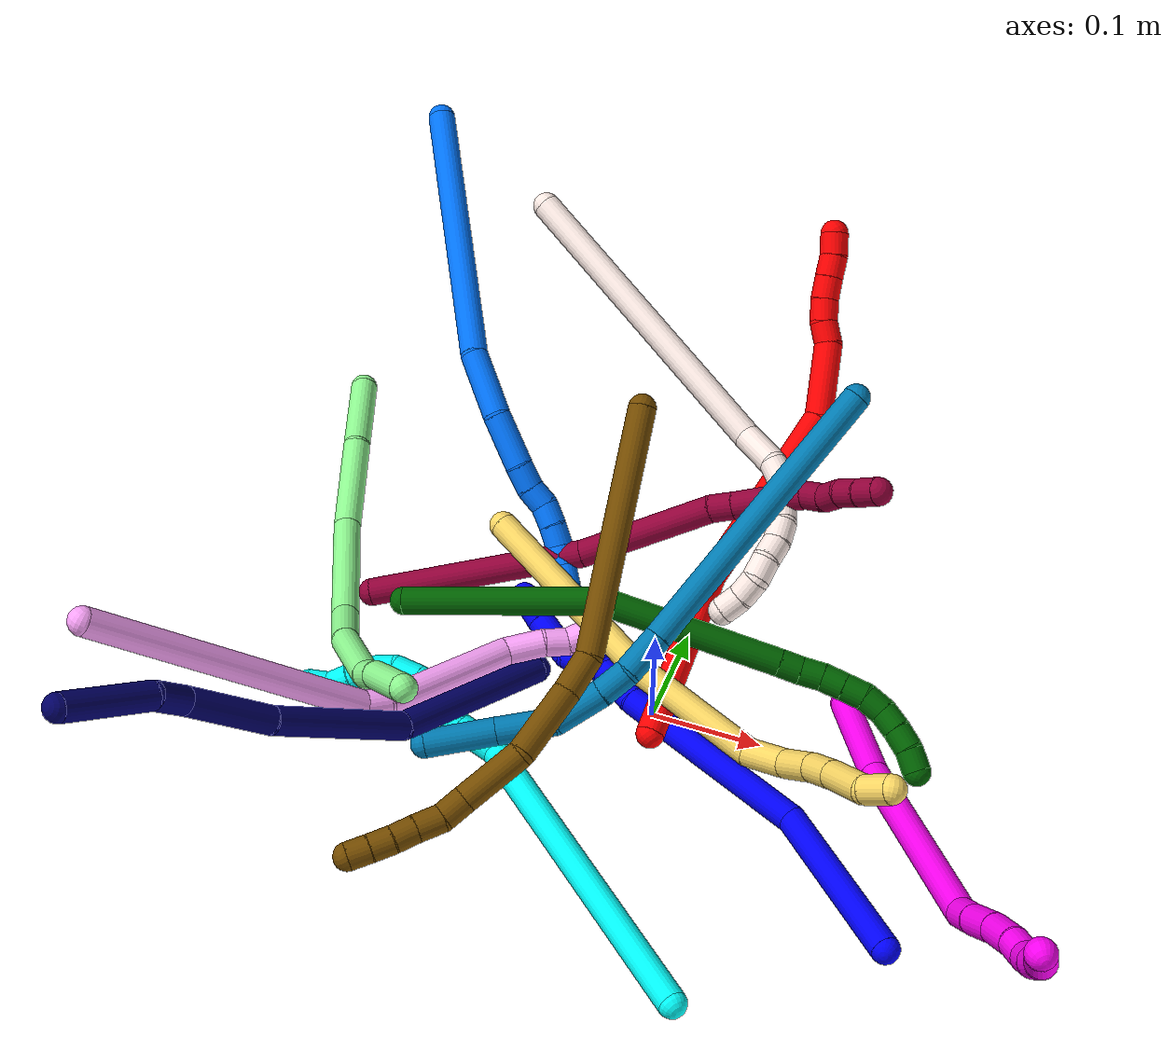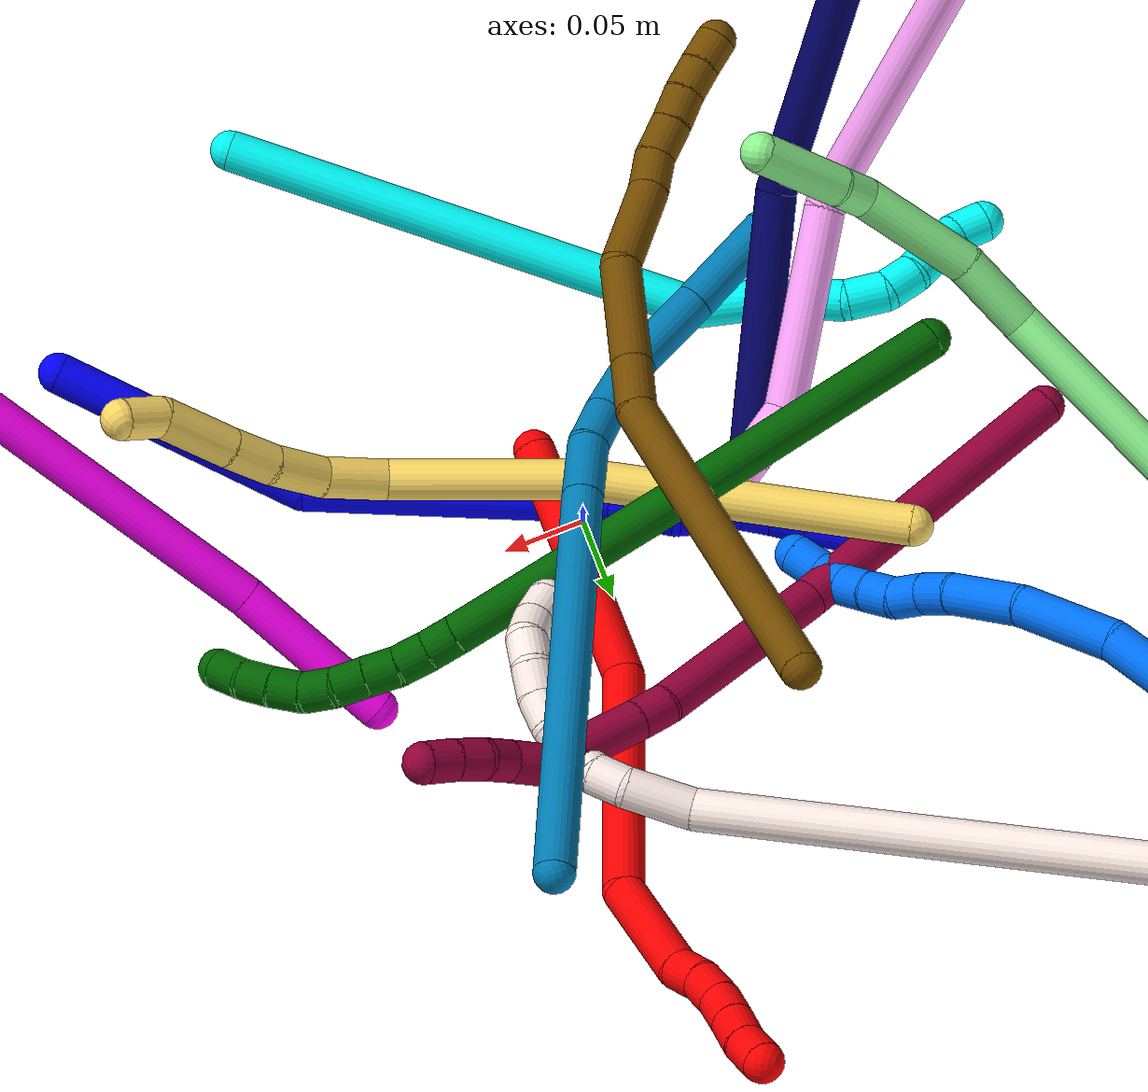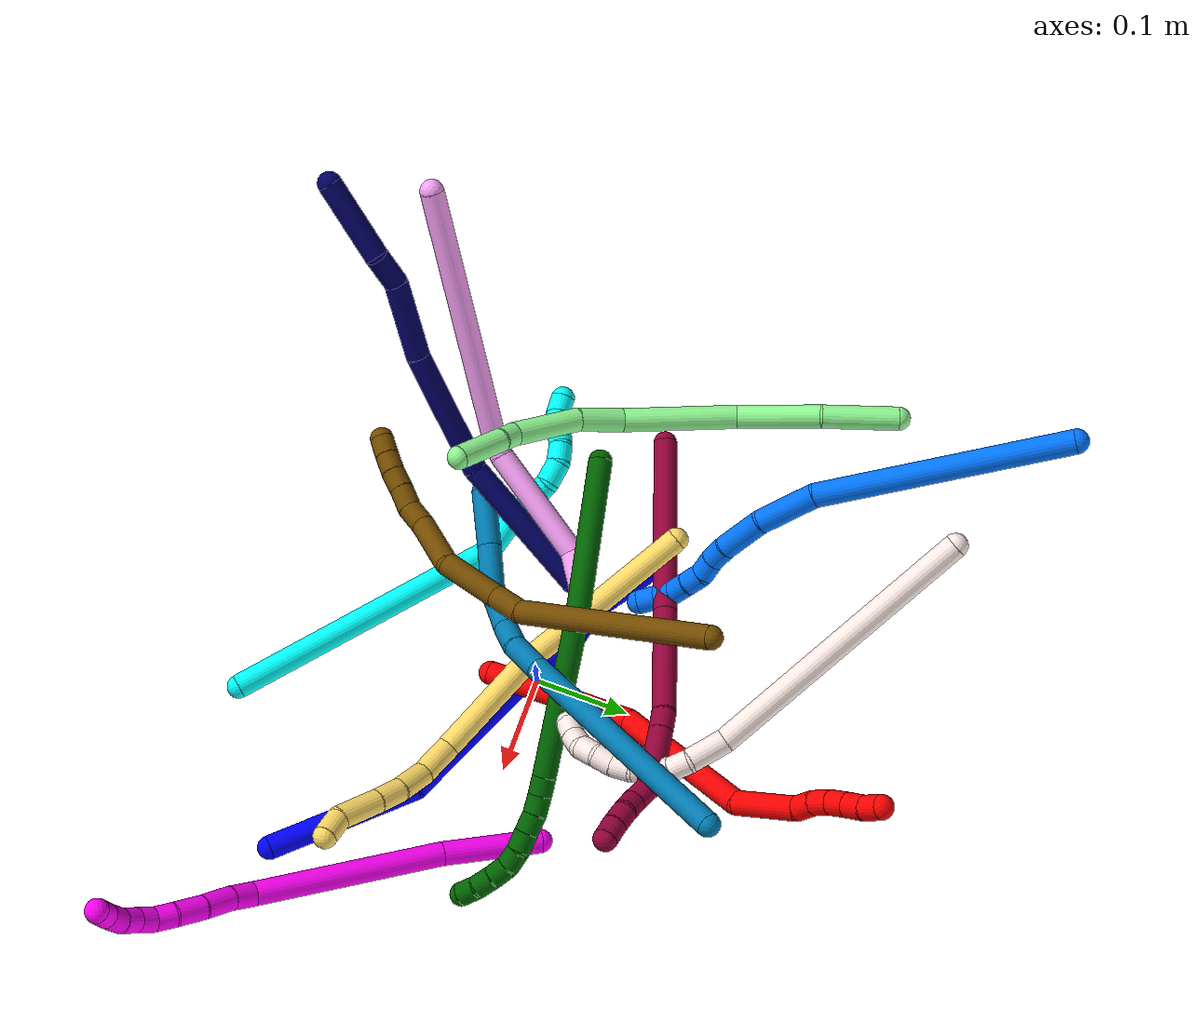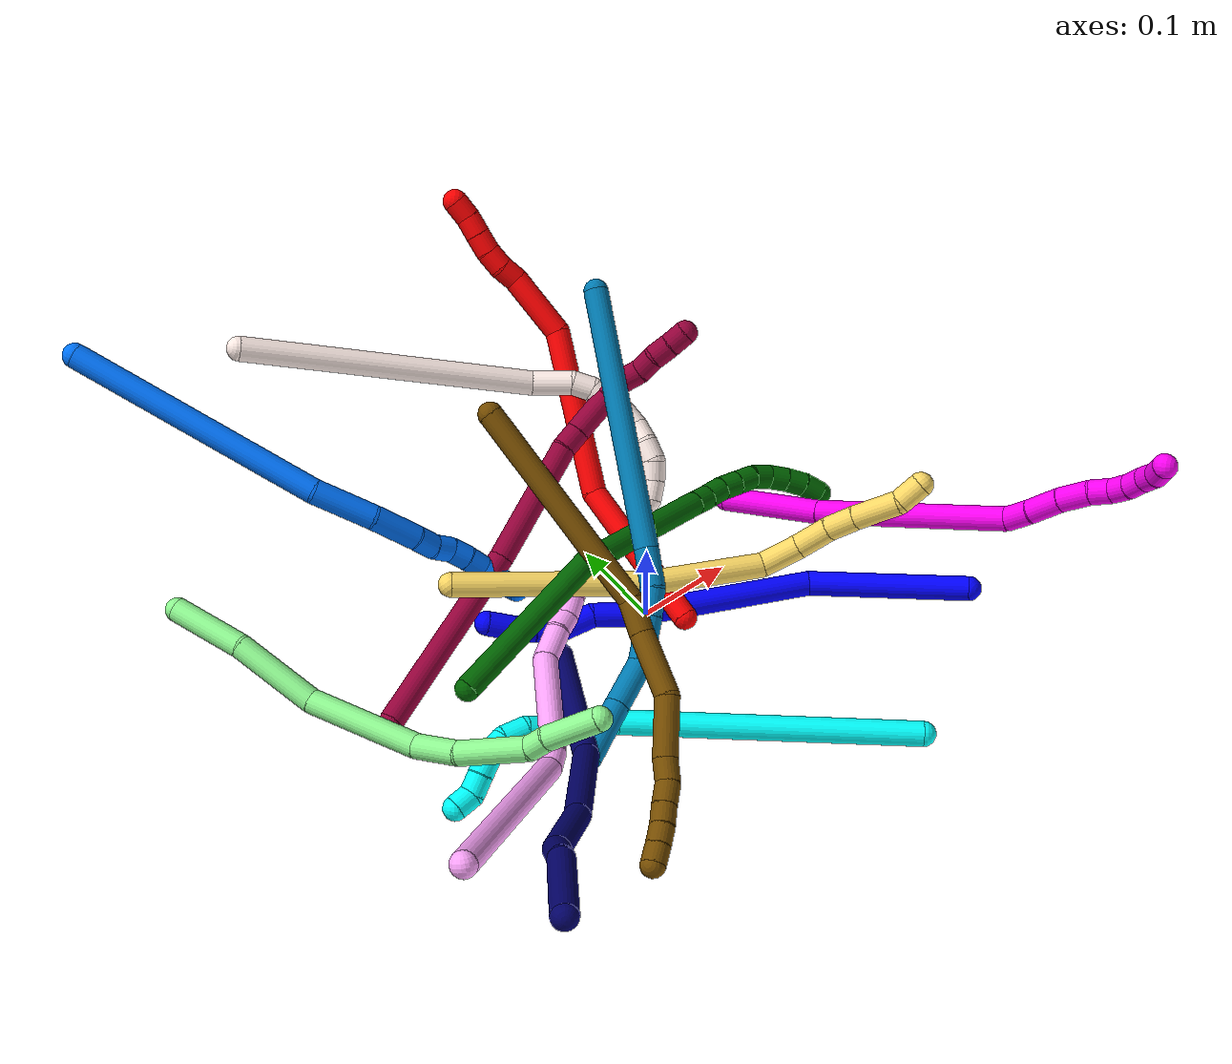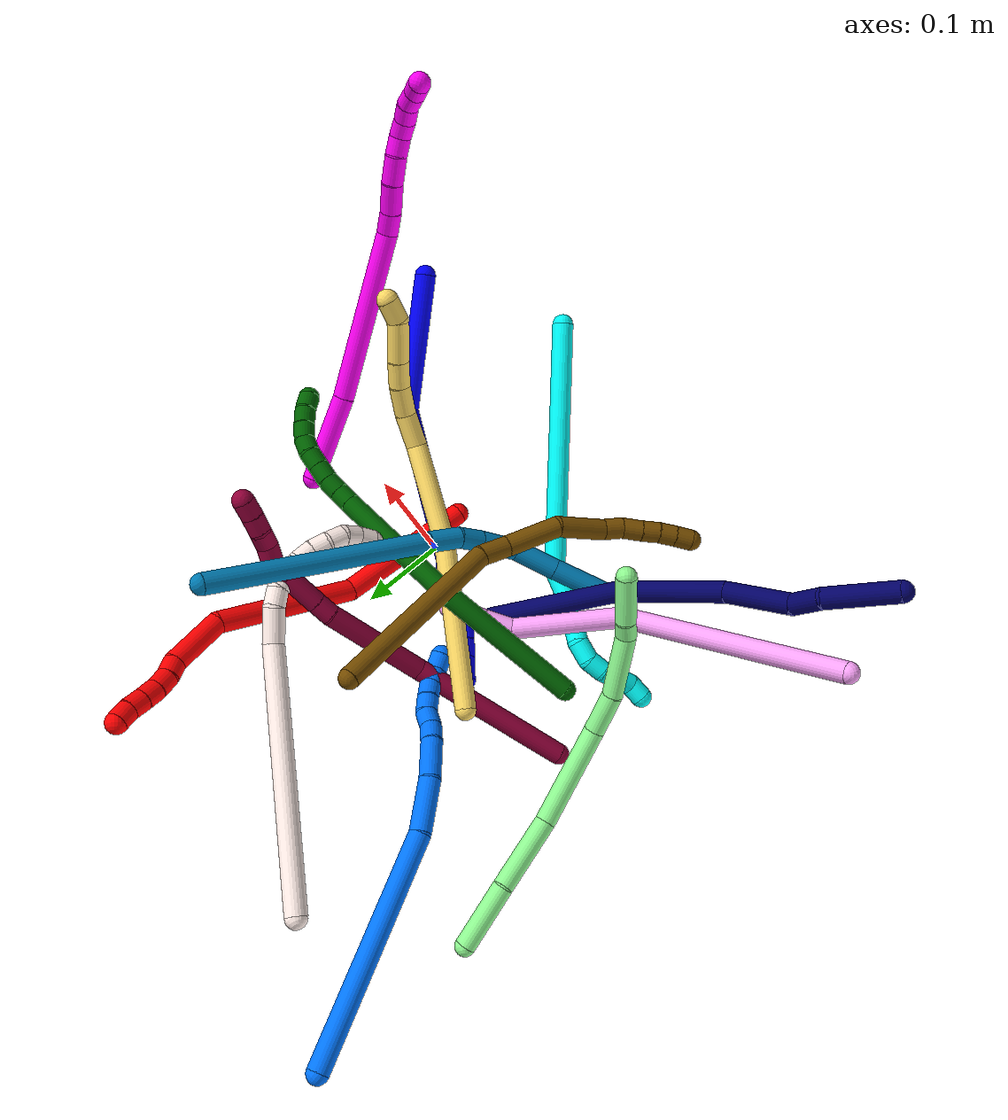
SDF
<sdf version="1.7">
 <world name="default">
  <plugin name="TubeGeneratorPlugin" filename="libtube_generator_plugin.so"/>
  <model name="photoneo_s_sensor">
   <static>1</static>
   <pose>0 0 2 1.57079 1.57079 3.14159</pose>
   <link name="link">
    <inertial><mass>0.1</mass></inertial>
    <sensor name="sensor" type="depth">
     <update_rate>30</update_rate>
     <camera>
      <horizontal_fov>1.22</horizontal_fov>
      <image><width>1920</width><height>1200</height><format>B8G8R8</format></image>
      <clip><near>0.1</near><far>4</far></clip>
      <depth_camera><output>points</output></depth_camera>
     </camera>
     <plugin name="camera_plugin" filename="libgazebo_ros_depth_camera.so">
      <baseline>0.2</baseline>
      <alwaysOn>1</alwaysOn>
      <updateRate>0.0</updateRate>
      <cameraName>camera_ir</cameraName>
      <imageTopicName>/camera/color/image_raw</imageTopicName>
      <cameraInfoTopicName>/camera/color/camera_info</cameraInfoTopicName>
      <depthImageTopicName>/camera/depth/image_raw</depthImageTopicName>
      <depthImageCameraInfoTopicName>/camera/depth/camera_info</depthImageCameraInfoTopicName>
      <pointCloudTopicName>/camera/depth/points</pointCloudTopicName>
      <frameName>fr_optical</frameName>
      <pointCloudCutoff>0.1</pointCloudCutoff>
      <pointCloudCutoffMax>2.0</pointCloudCutoffMax>
      <distortionK1>0</distortionK1>
      <distortionK2>0</distortionK2>
      <distortionK3>0</distortionK3>
      <distortionT1>0</distortionT1>
      <distortionT2>0</distortionT2>
      <CxPrime>0</CxPrime>
      <Cx>0</Cx>
      <Cy>0</Cy>
      <focalLength>0</focalLength>
      <hackBaseline>0</hackBaseline>
     </plugin>
    </sensor>
   </link>
  </model>
  <gravity>0 0 -9.8</gravity>
  <magnetic_field>6e-06 2.3e-05 -4.2e-05</magnetic_field>
  <atmosphere type="adiabatic"/>
  <physics name="default_physics" default="0" type="ode">
   <max_step_size>0.003</max_step_size>
   <real_time_factor>1</real_time_factor>
   <real_time_update_rate>1000</real_time_update_rate>
   <max_contacts>10000</max_contacts>
   <ode>
    <solver>
     <type>quick</type>
     <iters>100</iters>
     <sor>1.3</sor>
     <use_dynamic_moi_rescaling>0</use_dynamic_moi_rescaling>
    </solver>
    <constraints>
     <contact_max_correcting_vel>0</contact_max_correcting_vel>
     <contact_surface_layer>0.001</contact_surface_layer>
     <cfm>0</cfm>
     <erp>0.2</erp>
    </constraints>
   </ode>
  </physics>
  <scene><ambient>0.4 0.4 0.4 1</ambient><background>0.7 0.7 0.7 1</background><shadows>0</shadows></scene>
  <audio><device>default</device></audio>
  <spherical_coordinates>
   <surface_model>EARTH_WGS84</surface_model>
   <latitude_deg>0</latitude_deg>
   <longitude_deg>0</longitude_deg>
   <elevation>0</elevation>
   <heading_deg>0</heading_deg>
  </spherical_coordinates>
  <model name="bin">
   <static>1</static>
   <link name="bottom">
    <collision name="collision-bottom">
     <pose>0 0 -0.01 0 -0 0</pose>
     <geometry><box><size>0.8 0.6 0.02</size></box></geometry>
     <surface>
      <friction><ode><mu>100</mu><mu2>100</mu2></ode></friction>
      <contact><collide_bitmask>65535</collide_bitmask></contact>
     </surface>
    </collision>
   </link>
   <link name="west_wall">
    <collision name="collision-west_wall">
     <pose>-0.41 0 0.1 0 -0 0</pose>
     <geometry><box><size>0.02 0.6 0.2</size></box></geometry>
     <surface>
      <friction><ode><mu>100</mu><mu2>100</mu2></ode></friction>
      <contact><collide_bitmask>65535</collide_bitmask></contact>
     </surface>
    </collision>
   </link>
   <link name="east_wall">
    <collision name="collision-east_wall">
     <pose>0.41 0 0.1 0 -0 0</pose>
     <geometry><box><size>0.02 0.6 0.2</size></box></geometry>
     <surface>
      <friction><ode><mu>100</mu><mu2>100</mu2></ode></friction>
      <contact><collide_bitmask>65535</collide_bitmask></contact>
     </surface>
    </collision>
   </link>
   <link name="south_wall">
    <collision name="collision-south_wall">
     <pose>0 -0.31 0.1 0 -0 0</pose>
     <geometry><box><size>0.8 0.02 0.2</size></box></geometry>
     <surface>
      <friction><ode><mu>100</mu><mu2>100</mu2></ode></friction>
      <contact><collide_bitmask>65535</collide_bitmask></contact>
     </surface>
    </collision>
   </link>
   <link name="north_wall">
    <collision name="collision-north_wall">
     <pose>0 0.31 0.1 0 -0 0</pose>
     <geometry><box><size>0.8 0.02 0.2</size></box></geometry>
     <surface>
      <friction><ode><mu>100</mu><mu2>100</mu2></ode></friction>
      <contact><collide_bitmask>65535</collide_bitmask></contact>
     </surface>
    </collision>
   </link>
  </model>
  <model name="1">
   <static>0</static>
   <link name="1">
    <collision name="collision-cylinder-e_1_1_4">
     <pose>-0.051967 -0.001839 0.062502 0.029412 -0.693413 -0.010627</pose>
     <geometry><cylinder><radius>0.0125</radius><length>0.162609</length></cylinder></geometry>
     <surface>
      <friction><ode><mu>1.16</mu><mu2>1.16</mu2><slip1>0</slip1><slip2>0</slip2></ode></friction>
      <contact><ode><kp>1e+06</kp><kd>1</kd><max_vel>0</max_vel><min_depth>0.001</min_depth></ode></contact>
     </surface>
    </collision>
    <visual name="visual-cylinder-e_1_1_4">
     <pose>-0.051967 -0.001839 0.062502 0.029412 -0.693413 -0.010627</pose>
     <geometry><cylinder><radius>0.0125</radius><length>0.162609</length></cylinder></geometry>
     <material><ambient>0 0 1 1</ambient></material>
    </visual>
    <collision name="collision-cylinder-e_2_4_5">
     <pose>-0.186599 1.3e-05 0.166472 -0.088771 -1.10425 0.054708</pose>
     <geometry><cylinder><radius>0.0125</radius><length>0.185114</length></cylinder></geometry>
     <surface>
      <friction><ode><mu>1.16</mu><mu2>1.16</mu2><slip1>0</slip1><slip2>0</slip2></ode></friction>
      <contact><ode><kp>1e+06</kp><kd>1</kd><max_vel>0</max_vel><min_depth>0.001</min_depth></ode></contact>
     </surface>
    </collision>
    <visual name="visual-cylinder-e_2_4_5">
     <pose>-0.186599 1.3e-05 0.166472 -0.088771 -1.10425 0.054708</pose>
     <geometry><cylinder><radius>0.0125</radius><length>0.185114</length></cylinder></geometry>
     <material><ambient>0 0 1 1</ambient></material>
    </visual>
    <collision name="collision-cylinder-e_3_5_6">
     <pose>-0.286252 0.002013 0.219151 0.149737 -0.982278 -0.080194</pose>
     <geometry><cylinder><radius>0.0125</radius><length>0.040847</length></cylinder></geometry>
     <surface>
      <friction><ode><mu>1.16</mu><mu2>1.16</mu2><slip1>0</slip1><slip2>0</slip2></ode></friction>
      <contact><ode><kp>1e+06</kp><kd>1</kd><max_vel>0</max_vel><min_depth>0.001</min_depth></ode></contact>
     </surface>
    </collision>
    <visual name="visual-cylinder-e_3_5_6">
     <pose>-0.286252 0.002013 0.219151 0.149737 -0.982278 -0.080194</pose>
     <geometry><cylinder><radius>0.0125</radius><length>0.040847</length></cylinder></geometry>
     <material><ambient>0 0 1 1</ambient></material>
    </visual>
    <collision name="collision-cylinder-e_4_6_7">
     <pose>-0.320891 0.005747 0.237857 -0.626591 -1.08798 0.387008</pose>
     <geometry><cylinder><radius>0.0125</radius><length>0.039858</length></cylinder></geometry>
     <surface>
      <friction><ode><mu>1.16</mu><mu2>1.16</mu2><slip1>0</slip1><slip2>0</slip2></ode></friction>
      <contact><ode><kp>1e+06</kp><kd>1</kd><max_vel>0</max_vel><min_depth>0.001</min_depth></ode></contact>
     </surface>
    </collision>
    <visual name="visual-cylinder-e_4_6_7">
     <pose>-0.320891 0.005747 0.237857 -0.626591 -1.08798 0.387008</pose>
     <geometry><cylinder><radius>0.0125</radius><length>0.039858</length></cylinder></geometry>
     <material><ambient>0 0 1 1</ambient></material>
    </visual>
    <collision name="collision-cylinder-e_5_7_8">
     <pose>-0.347337 0.009443 0.250601 0.318325 -1.00977 -0.176963</pose>
     <geometry><cylinder><radius>0.0125</radius><length>0.020776</length></cylinder></geometry>
     <surface>
      <friction><ode><mu>1.16</mu><mu2>1.16</mu2><slip1>0</slip1><slip2>0</slip2></ode></friction>
      <contact><ode><kp>1e+06</kp><kd>1</kd><max_vel>0</max_vel><min_depth>0.001</min_depth></ode></contact>
     </surface>
    </collision>
    <visual name="visual-cylinder-e_5_7_8">
     <pose>-0.347337 0.009443 0.250601 0.318325 -1.00977 -0.176963</pose>
     <geometry><cylinder><radius>0.0125</radius><length>0.020776</length></cylinder></geometry>
     <material><ambient>0 0 1 1</ambient></material>
    </visual>
    <collision name="collision-cylinder-e_6_8_9">
     <pose>-0.36529 0.005423 0.261981 0.357511 -0.950277 -0.185372</pose>
     <geometry><cylinder><radius>0.0125</radius><length>0.022511</length></cylinder></geometry>
     <surface>
      <friction><ode><mu>1.16</mu><mu2>1.16</mu2><slip1>0</slip1><slip2>0</slip2></ode></friction>
      <contact><ode><kp>1e+06</kp><kd>1</kd><max_vel>0</max_vel><min_depth>0.001</min_depth></ode></contact>
     </surface>
    </collision>
    <visual name="visual-cylinder-e_6_8_9">
     <pose>-0.36529 0.005423 0.261981 0.357511 -0.950277 -0.185372</pose>
     <geometry><cylinder><radius>0.0125</radius><length>0.022511</length></cylinder></geometry>
     <material><ambient>0 0 1 1</ambient></material>
    </visual>
    <collision name="collision-cylinder-e_7_9_2">
     <pose>-0.386334 -0.001338 0.274334 0.622998 -0.998262 -0.347532</pose>
     <geometry><cylinder><radius>0.0125</radius><length>0.028286</length></cylinder></geometry>
     <surface>
      <friction><ode><mu>1.16</mu><mu2>1.16</mu2><slip1>0</slip1><slip2>0</slip2></ode></friction>
      <contact><ode><kp>1e+06</kp><kd>1</kd><max_vel>0</max_vel><min_depth>0.001</min_depth></ode></contact>
     </surface>
    </collision>
    <visual name="visual-cylinder-e_7_9_2">
     <pose>-0.386334 -0.001338 0.274334 0.622998 -0.998262 -0.347532</pose>
     <geometry><cylinder><radius>0.0125</radius><length>0.028286</length></cylinder></geometry>
     <material><ambient>0 0 1 1</ambient></material>
    </visual>
    <collision name="collision-sphere-2">
     <pose>-0.398222 -0.005809 0.280557 0 -0 0</pose>
     <geometry><sphere><radius>0.0125</radius></sphere></geometry>
     <surface>
      <friction><ode><mu>1.16</mu><mu2>1.16</mu2><slip1>0</slip1><slip2>0</slip2></ode></friction>
      <contact><ode><kp>1e+06</kp><kd>1</kd><max_vel>0</max_vel><min_depth>0.001</min_depth></ode></contact>
     </surface>
    </collision>
    <visual name="visual-sphere-2">
     <pose>-0.398222 -0.005809 0.280557 0 -0 0</pose>
     <geometry><sphere><radius>0.0125</radius></sphere></geometry>
     <material><ambient>0 0 1 1</ambient></material>
    </visual>
    <collision name="collision-sphere-9">
     <pose>-0.374447 0.003133 0.268111 0 -0 0</pose>
     <geometry><sphere><radius>0.0125</radius></sphere></geometry>
     <surface>
      <friction><ode><mu>1.16</mu><mu2>1.16</mu2><slip1>0</slip1><slip2>0</slip2></ode></friction>
      <contact><ode><kp>1e+06</kp><kd>1</kd><max_vel>0</max_vel><min_depth>0.001</min_depth></ode></contact>
     </surface>
    </collision>
    <visual name="visual-sphere-9">
     <pose>-0.374447 0.003133 0.268111 0 -0 0</pose>
     <geometry><sphere><radius>0.0125</radius></sphere></geometry>
     <material><ambient>0 0 1 1</ambient></material>
    </visual>
    <collision name="collision-sphere-4">
     <pose>-0.103934 -0.003678 0.125003 0 -0 0</pose>
     <geometry><sphere><radius>0.0125</radius></sphere></geometry>
     <surface>
      <friction><ode><mu>1.16</mu><mu2>1.16</mu2><slip1>0</slip1><slip2>0</slip2></ode></friction>
      <contact><ode><kp>1e+06</kp><kd>1</kd><max_vel>0</max_vel><min_depth>0.001</min_depth></ode></contact>
     </surface>
    </collision>
    <visual name="visual-sphere-4">
     <pose>-0.103934 -0.003678 0.125003 0 -0 0</pose>
     <geometry><sphere><radius>0.0125</radius></sphere></geometry>
     <material><ambient>0 0 1 1</ambient></material>
    </visual>
    <collision name="collision-sphere-1">
     <geometry><sphere><radius>0.0125</radius></sphere></geometry>
     <surface>
      <friction><ode><mu>1.16</mu><mu2>1.16</mu2><slip1>0</slip1><slip2>0</slip2></ode></friction>
      <contact><ode><kp>1e+06</kp><kd>1</kd><max_vel>0</max_vel><min_depth>0.001</min_depth></ode></contact>
     </surface>
    </collision>
    <visual name="visual-sphere-1">
     <geometry><sphere><radius>0.0125</radius></sphere></geometry>
     <material><ambient>0 0 1 1</ambient></material>
    </visual>
    <collision name="collision-sphere-8">
     <pose>-0.356133 0.007713 0.25585 0 -0 0</pose>
     <geometry><sphere><radius>0.0125</radius></sphere></geometry>
     <surface>
      <friction><ode><mu>1.16</mu><mu2>1.16</mu2><slip1>0</slip1><slip2>0</slip2></ode></friction>
      <contact><ode><kp>1e+06</kp><kd>1</kd><max_vel>0</max_vel><min_depth>0.001</min_depth></ode></contact>
     </surface>
    </collision>
    <visual name="visual-sphere-8">
     <pose>-0.356133 0.007713 0.25585 0 -0 0</pose>
     <geometry><sphere><radius>0.0125</radius></sphere></geometry>
     <material><ambient>0 0 1 1</ambient></material>
    </visual>
    <collision name="collision-sphere-5">
     <pose>-0.269265 0.003704 0.20794 0 -0 0</pose>
     <geometry><sphere><radius>0.0125</radius></sphere></geometry>
     <surface>
      <friction><ode><mu>1.16</mu><mu2>1.16</mu2><slip1>0</slip1><slip2>0</slip2></ode></friction>
      <contact><ode><kp>1e+06</kp><kd>1</kd><max_vel>0</max_vel><min_depth>0.001</min_depth></ode></contact>
     </surface>
    </collision>
    <visual name="visual-sphere-5">
     <pose>-0.269265 0.003704 0.20794 0 -0 0</pose>
     <geometry><sphere><radius>0.0125</radius></sphere></geometry>
     <material><ambient>0 0 1 1</ambient></material>
    </visual>
    <collision name="collision-sphere-6">
     <pose>-0.30324 0.000322 0.230362 0 -0 0</pose>
     <geometry><sphere><radius>0.0125</radius></sphere></geometry>
     <surface>
      <friction><ode><mu>1.16</mu><mu2>1.16</mu2><slip1>0</slip1><slip2>0</slip2></ode></friction>
      <contact><ode><kp>1e+06</kp><kd>1</kd><max_vel>0</max_vel><min_depth>0.001</min_depth></ode></contact>
     </surface>
    </collision>
    <visual name="visual-sphere-6">
     <pose>-0.30324 0.000322 0.230362 0 -0 0</pose>
     <geometry><sphere><radius>0.0125</radius></sphere></geometry>
     <material><ambient>0 0 1 1</ambient></material>
    </visual>
    <collision name="collision-sphere-7">
     <pose>-0.338542 0.011173 0.245352 0 -0 0</pose>
     <geometry><sphere><radius>0.0125</radius></sphere></geometry>
     <surface>
      <friction><ode><mu>1.16</mu><mu2>1.16</mu2><slip1>0</slip1><slip2>0</slip2></ode></friction>
      <contact><ode><kp>1e+06</kp><kd>1</kd><max_vel>0</max_vel><min_depth>0.001</min_depth></ode></contact>
     </surface>
    </collision>
    <visual name="visual-sphere-7">
     <pose>-0.338542 0.011173 0.245352 0 -0 0</pose>
     <geometry><sphere><radius>0.0125</radius></sphere></geometry>
     <material><ambient>0 0 1 1</ambient></material>
    </visual>
    <inertial>
     <pose>-0.187684 0.00059 0.15655 0 -0 0</pose>
     <mass>0.5</mass>
     <inertia>
      <ixx>0.000511</ixx>
      <ixy>0</ixy>
      <ixz>0</ixz>
      <iyy>0.000929</iyy>
      <iyz>0</iyz>
      <izz>0.000738</izz>
     </inertia>
    </inertial>
   </link>
   <pose>0.263098 -0.193046 0.033411 -2.02962 0.277411 -0.021365</pose>
  </model>
  <model name="2">
   <static>0</static>
   <link name="2">
    <collision name="collision-cylinder-e_1_1_4">
     <pose>-0.017792 0.062116 0.047657 -0.916359 -0.223461 0.110556</pose>
     <geometry><cylinder><radius>0.0125</radius><length>0.160577</length></cylinder></geometry>
     <surface>
      <friction><ode><mu>1.16</mu><mu2>1.16</mu2><slip1>0</slip1><slip2>0</slip2></ode></friction>
      <contact><ode><kp>1e+06</kp><kd>1</kd><max_vel>0</max_vel><min_depth>0.001</min_depth></ode></contact>
     </surface>
    </collision>
    <visual name="visual-cylinder-e_1_1_4">
     <pose>-0.017792 0.062116 0.047657 -0.916359 -0.223461 0.110556</pose>
     <geometry><cylinder><radius>0.0125</radius><length>0.160577</length></cylinder></geometry>
     <material><ambient>1 0 0 1</ambient></material>
    </visual>
    <collision name="collision-cylinder-e_2_4_5">
     <pose>-0.024696 0.202584 0.126775 -1.18897 0.128255 -0.086775</pose>
     <geometry><cylinder><radius>0.0125</radius><length>0.170261</length></cylinder></geometry>
     <surface>
      <friction><ode><mu>1.16</mu><mu2>1.16</mu2><slip1>0</slip1><slip2>0</slip2></ode></friction>
      <contact><ode><kp>1e+06</kp><kd>1</kd><max_vel>0</max_vel><min_depth>0.001</min_depth></ode></contact>
     </surface>
    </collision>
    <visual name="visual-cylinder-e_2_4_5">
     <pose>-0.024696 0.202584 0.126775 -1.18897 0.128255 -0.086775</pose>
     <geometry><cylinder><radius>0.0125</radius><length>0.170261</length></cylinder></geometry>
     <material><ambient>1 0 0 1</ambient></material>
    </visual>
    <collision name="collision-cylinder-e_3_5_6">
     <pose>-0.012119 0.30346 0.18373 -0.723624 0.0496 -0.018776</pose>
     <geometry><cylinder><radius>0.0125</radius><length>0.068125</length></cylinder></geometry>
     <surface>
      <friction><ode><mu>1.16</mu><mu2>1.16</mu2><slip1>0</slip1><slip2>0</slip2></ode></friction>
      <contact><ode><kp>1e+06</kp><kd>1</kd><max_vel>0</max_vel><min_depth>0.001</min_depth></ode></contact>
     </surface>
    </collision>
    <visual name="visual-cylinder-e_3_5_6">
     <pose>-0.012119 0.30346 0.18373 -0.723624 0.0496 -0.018776</pose>
     <geometry><cylinder><radius>0.0125</radius><length>0.068125</length></cylinder></geometry>
     <material><ambient>1 0 0 1</ambient></material>
    </visual>
    <collision name="collision-cylinder-e_4_6_7">
     <pose>-0.008373 0.329733 0.218356 -0.389467 0.205489 -0.040667</pose>
     <geometry><cylinder><radius>0.0125</radius><length>0.020164</length></cylinder></geometry>
     <surface>
      <friction><ode><mu>1.16</mu><mu2>1.16</mu2><slip1>0</slip1><slip2>0</slip2></ode></friction>
      <contact><ode><kp>1e+06</kp><kd>1</kd><max_vel>0</max_vel><min_depth>0.001</min_depth></ode></contact>
     </surface>
    </collision>
    <visual name="visual-cylinder-e_4_6_7">
     <pose>-0.008373 0.329733 0.218356 -0.389467 0.205489 -0.040667</pose>
     <geometry><cylinder><radius>0.0125</radius><length>0.020164</length></cylinder></geometry>
     <material><ambient>1 0 0 1</ambient></material>
    </visual>
    <collision name="collision-cylinder-e_5_7_8">
     <pose>-0.004682 0.339429 0.235508 -0.638137 0.162217 -0.053694</pose>
     <geometry><cylinder><radius>0.0125</radius><length>0.020237</length></cylinder></geometry>
     <surface>
      <friction><ode><mu>1.16</mu><mu2>1.16</mu2><slip1>0</slip1><slip2>0</slip2></ode></friction>
      <contact><ode><kp>1e+06</kp><kd>1</kd><max_vel>0</max_vel><min_depth>0.001</min_depth></ode></contact>
     </surface>
    </collision>
    <visual name="visual-cylinder-e_5_7_8">
     <pose>-0.004682 0.339429 0.235508 -0.638137 0.162217 -0.053694</pose>
     <geometry><cylinder><radius>0.0125</radius><length>0.020237</length></cylinder></geometry>
     <material><ambient>1 0 0 1</ambient></material>
    </visual>
    <collision name="collision-cylinder-e_6_8_9">
     <pose>-0.000931 0.352501 0.250564 -0.791569 0.208348 -0.087315</pose>
     <geometry><cylinder><radius>0.0125</radius><length>0.020467</length></cylinder></geometry>
     <surface>
      <friction><ode><mu>1.16</mu><mu2>1.16</mu2><slip1>0</slip1><slip2>0</slip2></ode></friction>
      <contact><ode><kp>1e+06</kp><kd>1</kd><max_vel>0</max_vel><min_depth>0.001</min_depth></ode></contact>
     </surface>
    </collision>
    <visual name="visual-cylinder-e_6_8_9">
     <pose>-0.000931 0.352501 0.250564 -0.791569 0.208348 -0.087315</pose>
     <geometry><cylinder><radius>0.0125</radius><length>0.020467</length></cylinder></geometry>
     <material><ambient>1 0 0 1</ambient></material>
    </visual>
    <collision name="collision-cylinder-e_7_9_10">
     <pose>0.00308 0.366851 0.264327 -0.82124 0.189552 -0.082726</pose>
     <geometry><cylinder><radius>0.0125</radius><length>0.020107</length></cylinder></geometry>
     <surface>
      <friction><ode><mu>1.16</mu><mu2>1.16</mu2><slip1>0</slip1><slip2>0</slip2></ode></friction>
      <contact><ode><kp>1e+06</kp><kd>1</kd><max_vel>0</max_vel><min_depth>0.001</min_depth></ode></contact>
     </surface>
    </collision>
    <visual name="visual-cylinder-e_7_9_10">
     <pose>0.00308 0.366851 0.264327 -0.82124 0.189552 -0.082726</pose>
     <geometry><cylinder><radius>0.0125</radius><length>0.020107</length></cylinder></geometry>
     <material><ambient>1 0 0 1</ambient></material>
    </visual>
    <collision name="collision-cylinder-e_8_10_2">
     <pose>0.007115 0.379866 0.278962 -0.631816 0.214992 -0.070514</pose>
     <geometry><cylinder><radius>0.0125</radius><length>0.020062</length></cylinder></geometry>
     <surface>
      <friction><ode><mu>1.16</mu><mu2>1.16</mu2><slip1>0</slip1><slip2>0</slip2></ode></friction>
      <contact><ode><kp>1e+06</kp><kd>1</kd><max_vel>0</max_vel><min_depth>0.001</min_depth></ode></contact>
     </surface>
    </collision>
    <visual name="visual-cylinder-e_8_10_2">
     <pose>0.007115 0.379866 0.278962 -0.631816 0.214992 -0.070514</pose>
     <geometry><cylinder><radius>0.0125</radius><length>0.020062</length></cylinder></geometry>
     <material><ambient>1 0 0 1</ambient></material>
    </visual>
    <collision name="collision-sphere-2">
     <pose>0.009255 0.385655 0.28687 0 -0 0</pose>
     <geometry><sphere><radius>0.0125</radius></sphere></geometry>
     <surface>
      <friction><ode><mu>1.16</mu><mu2>1.16</mu2><slip1>0</slip1><slip2>0</slip2></ode></friction>
      <contact><ode><kp>1e+06</kp><kd>1</kd><max_vel>0</max_vel><min_depth>0.001</min_depth></ode></contact>
     </surface>
    </collision>
    <visual name="visual-sphere-2">
     <pose>0.009255 0.385655 0.28687 0 -0 0</pose>
     <geometry><sphere><radius>0.0125</radius></sphere></geometry>
     <material><ambient>1 0 0 1</ambient></material>
    </visual>
    <collision name="collision-sphere-10">
     <pose>0.004975 0.374078 0.271054 0 -0 0</pose>
     <geometry><sphere><radius>0.0125</radius></sphere></geometry>
     <surface>
      <friction><ode><mu>1.16</mu><mu2>1.16</mu2><slip1>0</slip1><slip2>0</slip2></ode></friction>
      <contact><ode><kp>1e+06</kp><kd>1</kd><max_vel>0</max_vel><min_depth>0.001</min_depth></ode></contact>
     </surface>
    </collision>
    <visual name="visual-sphere-10">
     <pose>0.004975 0.374078 0.271054 0 -0 0</pose>
     <geometry><sphere><radius>0.0125</radius></sphere></geometry>
     <material><ambient>1 0 0 1</ambient></material>
    </visual>
    <collision name="collision-sphere-9">
     <pose>0.001186 0.359624 0.2576 0 -0 0</pose>
     <geometry><sphere><radius>0.0125</radius></sphere></geometry>
     <surface>
      <friction><ode><mu>1.16</mu><mu2>1.16</mu2><slip1>0</slip1><slip2>0</slip2></ode></friction>
      <contact><ode><kp>1e+06</kp><kd>1</kd><max_vel>0</max_vel><min_depth>0.001</min_depth></ode></contact>
     </surface>
    </collision>
    <visual name="visual-sphere-9">
     <pose>0.001186 0.359624 0.2576 0 -0 0</pose>
     <geometry><sphere><radius>0.0125</radius></sphere></geometry>
     <material><ambient>1 0 0 1</ambient></material>
    </visual>
    <collision name="collision-sphere-4">
     <pose>-0.035585 0.124232 0.095315 0 -0 0</pose>
     <geometry><sphere><radius>0.0125</radius></sphere></geometry>
     <surface>
      <friction><ode><mu>1.16</mu><mu2>1.16</mu2><slip1>0</slip1><slip2>0</slip2></ode></friction>
      <contact><ode><kp>1e+06</kp><kd>1</kd><max_vel>0</max_vel><min_depth>0.001</min_depth></ode></contact>
     </surface>
    </collision>
    <visual name="visual-sphere-4">
     <pose>-0.035585 0.124232 0.095315 0 -0 0</pose>
     <geometry><sphere><radius>0.0125</radius></sphere></geometry>
     <material><ambient>1 0 0 1</ambient></material>
    </visual>
    <collision name="collision-sphere-1">
     <geometry><sphere><radius>0.0125</radius></sphere></geometry>
     <surface>
      <friction><ode><mu>1.16</mu><mu2>1.16</mu2><slip1>0</slip1><slip2>0</slip2></ode></friction>
      <contact><ode><kp>1e+06</kp><kd>1</kd><max_vel>0</max_vel><min_depth>0.001</min_depth></ode></contact>
     </surface>
    </collision>
    <visual name="visual-sphere-1">
     <geometry><sphere><radius>0.0125</radius></sphere></geometry>
     <material><ambient>1 0 0 1</ambient></material>
    </visual>
    <collision name="collision-sphere-8">
     <pose>-0.003047 0.345377 0.243528 0 -0 0</pose>
     <geometry><sphere><radius>0.0125</radius></sphere></geometry>
     <surface>
      <friction><ode><mu>1.16</mu><mu2>1.16</mu2><slip1>0</slip1><slip2>0</slip2></ode></friction>
      <contact><ode><kp>1e+06</kp><kd>1</kd><max_vel>0</max_vel><min_depth>0.001</min_depth></ode></contact>
     </surface>
    </collision>
    <visual name="visual-sphere-8">
     <pose>-0.003047 0.345377 0.243528 0 -0 0</pose>
     <geometry><sphere><radius>0.0125</radius></sphere></geometry>
     <material><ambient>1 0 0 1</ambient></material>
    </visual>
    <collision name="collision-sphere-5">
     <pose>-0.013808 0.280935 0.158235 0 -0 0</pose>
     <geometry><sphere><radius>0.0125</radius></sphere></geometry>
     <surface>
      <friction><ode><mu>1.16</mu><mu2>1.16</mu2><slip1>0</slip1><slip2>0</slip2></ode></friction>
      <contact><ode><kp>1e+06</kp><kd>1</kd><max_vel>0</max_vel><min_depth>0.001</min_depth></ode></contact>
     </surface>
    </collision>
    <visual name="visual-sphere-5">
     <pose>-0.013808 0.280935 0.158235 0 -0 0</pose>
     <geometry><sphere><radius>0.0125</radius></sphere></geometry>
     <material><ambient>1 0 0 1</ambient></material>
    </visual>
    <collision name="collision-sphere-6">
     <pose>-0.01043 0.325985 0.209226 0 -0 0</pose>
     <geometry><sphere><radius>0.0125</radius></sphere></geometry>
     <surface>
      <friction><ode><mu>1.16</mu><mu2>1.16</mu2><slip1>0</slip1><slip2>0</slip2></ode></friction>
      <contact><ode><kp>1e+06</kp><kd>1</kd><max_vel>0</max_vel><min_depth>0.001</min_depth></ode></contact>
     </surface>
    </collision>
    <visual name="visual-sphere-6">
     <pose>-0.01043 0.325985 0.209226 0 -0 0</pose>
     <geometry><sphere><radius>0.0125</radius></sphere></geometry>
     <material><ambient>1 0 0 1</ambient></material>
    </visual>
    <collision name="collision-sphere-7">
     <pose>-0.006316 0.33348 0.227487 0 -0 0</pose>
     <geometry><sphere><radius>0.0125</radius></sphere></geometry>
     <surface>
      <friction><ode><mu>1.16</mu><mu2>1.16</mu2><slip1>0</slip1><slip2>0</slip2></ode></friction>
      <contact><ode><kp>1e+06</kp><kd>1</kd><max_vel>0</max_vel><min_depth>0.001</min_depth></ode></contact>
     </surface>
    </collision>
    <visual name="visual-sphere-7">
     <pose>-0.006316 0.33348 0.227487 0 -0 0</pose>
     <geometry><sphere><radius>0.0125</radius></sphere></geometry>
     <material><ambient>1 0 0 1</ambient></material>
    </visual>
    <inertial>
     <pose>-0.015931 0.201739 0.133925 0 -0 0</pose>
     <mass>0.5</mass>
     <inertia>
      <ixx>0.000791</ixx>
      <ixy>0</ixy>
      <ixz>0</ixz>
      <iyy>0.000437</iyy>
      <iyz>0</iyz>
      <izz>-0.000636</izz>
     </inertia>
    </inertial>
   </link>
   <pose>0.01361 -0.045989 0.030838 0.773926 -1.04603 -1.44545</pose>
  </model>
  <model name="3">
   <static>0</static>
   <link name="3">
    <collision name="collision-cylinder-e_1_1_4">
     <pose>-0.000447 0.001873 0.148899 -0.012576 -0.003005 1.9e-05</pose>
     <geometry><cylinder><radius>0.0125</radius><length>0.297823</length></cylinder></geometry>
     <surface>
      <friction><ode><mu>1.16</mu><mu2>1.16</mu2><slip1>0</slip1><slip2>0</slip2></ode></friction>
      <contact><ode><kp>1e+06</kp><kd>1</kd><max_vel>0</max_vel><min_depth>0.001</min_depth></ode></contact>
     </surface>
    </collision>
    <visual name="visual-cylinder-e_1_1_4">
     <pose>-0.000447 0.001873 0.148899 -0.012576 -0.003005 1.9e-05</pose>
     <geometry><cylinder><radius>0.0125</radius><length>0.297823</length></cylinder></geometry>
     <material><ambient>0.003922 1 0.996078 1</ambient></material>
    </visual>
    <collision name="collision-cylinder-e_2_4_5">
     <pose>-0.006371 -0.002722 0.315665 0.34729 -0.280607 -0.049537</pose>
     <geometry><cylinder><radius>0.0125</radius><length>0.03955</length></cylinder></geometry>
     <surface>
      <friction><ode><mu>1.16</mu><mu2>1.16</mu2><slip1>0</slip1><slip2>0</slip2></ode></friction>
      <contact><ode><kp>1e+06</kp><kd>1</kd><max_vel>0</max_vel><min_depth>0.001</min_depth></ode></contact>
     </surface>
    </collision>
    <visual name="visual-cylinder-e_2_4_5">
     <pose>-0.006371 -0.002722 0.315665 0.34729 -0.280607 -0.049537</pose>
     <geometry><cylinder><radius>0.0125</radius><length>0.03955</length></cylinder></geometry>
     <material><ambient>0.003922 1 0.996078 1</ambient></material>
    </visual>
    <collision name="collision-cylinder-e_3_5_6">
     <pose>-0.012299 -0.020286 0.358812 0.413639 -0.016329 -0.003426</pose>
     <geometry><cylinder><radius>0.0125</radius><length>0.055222</length></cylinder></geometry>
     <surface>
      <friction><ode><mu>1.16</mu><mu2>1.16</mu2><slip1>0</slip1><slip2>0</slip2></ode></friction>
      <contact><ode><kp>1e+06</kp><kd>1</kd><max_vel>0</max_vel><min_depth>0.001</min_depth></ode></contact>
     </surface>
    </collision>
    <visual name="visual-cylinder-e_3_5_6">
     <pose>-0.012299 -0.020286 0.358812 0.413639 -0.016329 -0.003426</pose>
     <geometry><cylinder><radius>0.0125</radius><length>0.055222</length></cylinder></geometry>
     <material><ambient>0.003922 1 0.996078 1</ambient></material>
    </visual>
    <collision name="collision-cylinder-e_4_6_7">
     <pose>-0.018087 -0.035023 0.394491 0.336753 -0.45105 -0.077959</pose>
     <geometry><cylinder><radius>0.0125</radius><length>0.024488</length></cylinder></geometry>
     <surface>
      <friction><ode><mu>1.16</mu><mu2>1.16</mu2><slip1>0</slip1><slip2>0</slip2></ode></friction>
      <contact><ode><kp>1e+06</kp><kd>1</kd><max_vel>0</max_vel><min_depth>0.001</min_depth></ode></contact>
     </surface>
    </collision>
    <visual name="visual-cylinder-e_4_6_7">
     <pose>-0.018087 -0.035023 0.394491 0.336753 -0.45105 -0.077959</pose>
     <geometry><cylinder><radius>0.0125</radius><length>0.024488</length></cylinder></geometry>
     <material><ambient>0.003922 1 0.996078 1</ambient></material>
    </visual>
    <collision name="collision-cylinder-e_5_7_8">
     <pose>-0.031531 -0.041266 0.410907 0.40817 -0.890912 -0.196998</pose>
     <geometry><cylinder><radius>0.0125</radius><length>0.020849</length></cylinder></geometry>
     <surface>
      <friction><ode><mu>1.16</mu><mu2>1.16</mu2><slip1>0</slip1><slip2>0</slip2></ode></friction>
      <contact><ode><kp>1e+06</kp><kd>1</kd><max_vel>0</max_vel><min_depth>0.001</min_depth></ode></contact>
     </surface>
    </collision>
    <visual name="visual-cylinder-e_5_7_8">
     <pose>-0.031531 -0.041266 0.410907 0.40817 -0.890912 -0.196998</pose>
     <geometry><cylinder><radius>0.0125</radius><length>0.020849</length></cylinder></geometry>
     <material><ambient>0.003922 1 0.996078 1</ambient></material>
    </visual>
    <collision name="collision-cylinder-e_6_8_9">
     <pose>-0.049464 -0.045241 0.420828 0.338124 -1.17206 -0.225655</pose>
     <geometry><cylinder><radius>0.0125</radius><length>0.021327</length></cylinder></geometry>
     <surface>
      <friction><ode><mu>1.16</mu><mu2>1.16</mu2><slip1>0</slip1><slip2>0</slip2></ode></friction>
      <contact><ode><kp>1e+06</kp><kd>1</kd><max_vel>0</max_vel><min_depth>0.001</min_depth></ode></contact>
     </surface>
    </collision>
    <visual name="visual-cylinder-e_6_8_9">
     <pose>-0.049464 -0.045241 0.420828 0.338124 -1.17206 -0.225655</pose>
     <geometry><cylinder><radius>0.0125</radius><length>0.021327</length></cylinder></geometry>
     <material><ambient>0.003922 1 0.996078 1</ambient></material>
    </visual>
    <collision name="collision-cylinder-e_7_9_10">
     <pose>-0.068901 -0.047151 0.428371 0.146692 -1.20544 -0.101039</pose>
     <geometry><cylinder><radius>0.0125</radius><length>0.020578</length></cylinder></geometry>
     <surface>
      <friction><ode><mu>1.16</mu><mu2>1.16</mu2><slip1>0</slip1><slip2>0</slip2></ode></friction>
      <contact><ode><kp>1e+06</kp><kd>1</kd><max_vel>0</max_vel><min_depth>0.001</min_depth></ode></contact>
     </surface>
    </collision>
    <visual name="visual-cylinder-e_7_9_10">
     <pose>-0.068901 -0.047151 0.428371 0.146692 -1.20544 -0.101039</pose>
     <geometry><cylinder><radius>0.0125</radius><length>0.020578</length></cylinder></geometry>
     <material><ambient>0.003922 1 0.996078 1</ambient></material>
    </visual>
    <collision name="collision-cylinder-e_8_10_2">
     <pose>-0.085138 -0.050167 0.439188 0.332375 -0.717349 -0.125599</pose>
     <geometry><cylinder><radius>0.0125</radius><length>0.020163</length></cylinder></geometry>
     <surface>
      <friction><ode><mu>1.16</mu><mu2>1.16</mu2><slip1>0</slip1><slip2>0</slip2></ode></friction>
      <contact><ode><kp>1e+06</kp><kd>1</kd><max_vel>0</max_vel><min_depth>0.001</min_depth></ode></contact>
     </surface>
    </collision>
    <visual name="visual-cylinder-e_8_10_2">
     <pose>-0.085138 -0.050167 0.439188 0.332375 -0.717349 -0.125599</pose>
     <geometry><cylinder><radius>0.0125</radius><length>0.020163</length></cylinder></geometry>
     <material><ambient>0.003922 1 0.996078 1</ambient></material>
    </visual>
    <collision name="collision-sphere-2">
     <pose>-0.091766 -0.052646 0.44637 0 -0 0</pose>
     <geometry><sphere><radius>0.0125</radius></sphere></geometry>
     <surface>
      <friction><ode><mu>1.16</mu><mu2>1.16</mu2><slip1>0</slip1><slip2>0</slip2></ode></friction>
      <contact><ode><kp>1e+06</kp><kd>1</kd><max_vel>0</max_vel><min_depth>0.001</min_depth></ode></contact>
     </surface>
    </collision>
    <visual name="visual-sphere-2">
     <pose>-0.091766 -0.052646 0.44637 0 -0 0</pose>
     <geometry><sphere><radius>0.0125</radius></sphere></geometry>
     <material><ambient>0.003922 1 0.996078 1</ambient></material>
    </visual>
    <collision name="collision-sphere-10">
     <pose>-0.078511 -0.047689 0.432007 0 -0 0</pose>
     <geometry><sphere><radius>0.0125</radius></sphere></geometry>
     <surface>
      <friction><ode><mu>1.16</mu><mu2>1.16</mu2><slip1>0</slip1><slip2>0</slip2></ode></friction>
      <contact><ode><kp>1e+06</kp><kd>1</kd><max_vel>0</max_vel><min_depth>0.001</min_depth></ode></contact>
     </surface>
    </collision>
    <visual name="visual-sphere-10">
     <pose>-0.078511 -0.047689 0.432007 0 -0 0</pose>
     <geometry><sphere><radius>0.0125</radius></sphere></geometry>
     <material><ambient>0.003922 1 0.996078 1</ambient></material>
    </visual>
    <collision name="collision-sphere-9">
     <pose>-0.059291 -0.046614 0.424734 0 -0 0</pose>
     <geometry><sphere><radius>0.0125</radius></sphere></geometry>
     <surface>
      <friction><ode><mu>1.16</mu><mu2>1.16</mu2><slip1>0</slip1><slip2>0</slip2></ode></friction>
      <contact><ode><kp>1e+06</kp><kd>1</kd><max_vel>0</max_vel><min_depth>0.001</min_depth></ode></contact>
     </surface>
    </collision>
    <visual name="visual-sphere-9">
     <pose>-0.059291 -0.046614 0.424734 0 -0 0</pose>
     <geometry><sphere><radius>0.0125</radius></sphere></geometry>
     <material><ambient>0.003922 1 0.996078 1</ambient></material>
    </visual>
    <collision name="collision-sphere-4">
     <pose>-0.000895 0.003745 0.297798 0 -0 0</pose>
     <geometry><sphere><radius>0.0125</radius></sphere></geometry>
     <surface>
      <friction><ode><mu>1.16</mu><mu2>1.16</mu2><slip1>0</slip1><slip2>0</slip2></ode></friction>
      <contact><ode><kp>1e+06</kp><kd>1</kd><max_vel>0</max_vel><min_depth>0.001</min_depth></ode></contact>
     </surface>
    </collision>
    <visual name="visual-sphere-4">
     <pose>-0.000895 0.003745 0.297798 0 -0 0</pose>
     <geometry><sphere><radius>0.0125</radius></sphere></geometry>
     <material><ambient>0.003922 1 0.996078 1</ambient></material>
    </visual>
    <collision name="collision-sphere-1">
     <geometry><sphere><radius>0.0125</radius></sphere></geometry>
     <surface>
      <friction><ode><mu>1.16</mu><mu2>1.16</mu2><slip1>0</slip1><slip2>0</slip2></ode></friction>
      <contact><ode><kp>1e+06</kp><kd>1</kd><max_vel>0</max_vel><min_depth>0.001</min_depth></ode></contact>
     </surface>
    </collision>
    <visual name="visual-sphere-1">
     <geometry><sphere><radius>0.0125</radius></sphere></geometry>
     <material><ambient>0.003922 1 0.996078 1</ambient></material>
    </visual>
    <collision name="collision-sphere-8">
     <pose>-0.039637 -0.043867 0.416923 0 -0 0</pose>
     <geometry><sphere><radius>0.0125</radius></sphere></geometry>
     <surface>
      <friction><ode><mu>1.16</mu><mu2>1.16</mu2><slip1>0</slip1><slip2>0</slip2></ode></friction>
      <contact><ode><kp>1e+06</kp><kd>1</kd><max_vel>0</max_vel><min_depth>0.001</min_depth></ode></contact>
     </surface>
    </collision>
    <visual name="visual-sphere-8">
     <pose>-0.039637 -0.043867 0.416923 0 -0 0</pose>
     <geometry><sphere><radius>0.0125</radius></sphere></geometry>
     <material><ambient>0.003922 1 0.996078 1</ambient></material>
    </visual>
    <collision name="collision-sphere-5">
     <pose>-0.011848 -0.009189 0.333532 0 -0 0</pose>
     <geometry><sphere><radius>0.0125</radius></sphere></geometry>
     <surface>
      <friction><ode><mu>1.16</mu><mu2>1.16</mu2><slip1>0</slip1><slip2>0</slip2></ode></friction>
      <contact><ode><kp>1e+06</kp><kd>1</kd><max_vel>0</max_vel><min_depth>0.001</min_depth></ode></contact>
     </surface>
    </collision>
    <visual name="visual-sphere-5">
     <pose>-0.011848 -0.009189 0.333532 0 -0 0</pose>
     <geometry><sphere><radius>0.0125</radius></sphere></geometry>
     <material><ambient>0.003922 1 0.996078 1</ambient></material>
    </visual>
    <collision name="collision-sphere-6">
     <pose>-0.01275 -0.031382 0.384091 0 -0 0</pose>
     <geometry><sphere><radius>0.0125</radius></sphere></geometry>
     <surface>
      <friction><ode><mu>1.16</mu><mu2>1.16</mu2><slip1>0</slip1><slip2>0</slip2></ode></friction>
      <contact><ode><kp>1e+06</kp><kd>1</kd><max_vel>0</max_vel><min_depth>0.001</min_depth></ode></contact>
     </surface>
    </collision>
    <visual name="visual-sphere-6">
     <pose>-0.01275 -0.031382 0.384091 0 -0 0</pose>
     <geometry><sphere><radius>0.0125</radius></sphere></geometry>
     <material><ambient>0.003922 1 0.996078 1</ambient></material>
    </visual>
    <collision name="collision-sphere-7">
     <pose>-0.023424 -0.038664 0.404892 0 -0 0</pose>
     <geometry><sphere><radius>0.0125</radius></sphere></geometry>
     <surface>
      <friction><ode><mu>1.16</mu><mu2>1.16</mu2><slip1>0</slip1><slip2>0</slip2></ode></friction>
      <contact><ode><kp>1e+06</kp><kd>1</kd><max_vel>0</max_vel><min_depth>0.001</min_depth></ode></contact>
     </surface>
    </collision>
    <visual name="visual-sphere-7">
     <pose>-0.023424 -0.038664 0.404892 0 -0 0</pose>
     <geometry><sphere><radius>0.0125</radius></sphere></geometry>
     <material><ambient>0.003922 1 0.996078 1</ambient></material>
    </visual>
    <inertial>
     <pose>-0.012708 -0.01067 0.243034 0 -0 0</pose>
     <mass>0.5</mass>
     <inertia>
      <ixx>0.002233</ixx>
      <ixy>0</ixy>
      <ixz>0</ixz>
      <iyy>0.002237</iyy>
      <iyz>0</iyz>
      <izz>3.2e-05</izz>
     </inertia>
    </inertial>
   </link>
   <pose>0.117086 -0.288551 0.013084 -1.562 -0.566981 0.867018</pose>
  </model>
  <model name="4">
   <static>0</static>
   <link name="4">
    <collision name="collision-cylinder-e_1_1_4">
     <pose>0.065959 0.120019 0.002861 -1.54696 0.502395 -0.491035</pose>
     <geometry><cylinder><radius>0.0125</radius><length>0.273959</length></cylinder></geometry>
     <surface>
      <friction><ode><mu>1.16</mu><mu2>1.16</mu2><slip1>0</slip1><slip2>0</slip2></ode></friction>
      <contact><ode><kp>1e+06</kp><kd>1</kd><max_vel>0</max_vel><min_depth>0.001</min_depth></ode></contact>
     </surface>
    </collision>
    <visual name="visual-cylinder-e_1_1_4">
     <pose>0.065959 0.120019 0.002861 -1.54696 0.502395 -0.491035</pose>
     <geometry><cylinder><radius>0.0125</radius><length>0.273959</length></cylinder></geometry>
     <material><ambient>1 0.65098 0.996078 1</ambient></material>
    </visual>
    <collision name="collision-cylinder-e_2_4_5">
     <pose>0.136768 0.249248 0.000972 -2.04702 0.437728 -0.699959</pose>
     <geometry><cylinder><radius>0.0125</radius><length>0.022882</length></cylinder></geometry>
     <surface>
      <friction><ode><mu>1.16</mu><mu2>1.16</mu2><slip1>0</slip1><slip2>0</slip2></ode></friction>
      <contact><ode><kp>1e+06</kp><kd>1</kd><max_vel>0</max_vel><min_depth>0.001</min_depth></ode></contact>
     </surface>
    </collision>
    <visual name="visual-cylinder-e_2_4_5">
     <pose>0.136768 0.249248 0.000972 -2.04702 0.437728 -0.699959</pose>
     <geometry><cylinder><radius>0.0125</radius><length>0.022882</length></cylinder></geometry>
     <material><ambient>1 0.65098 0.996078 1</ambient></material>
    </visual>
    <collision name="collision-cylinder-e_3_5_6">
     <pose>0.177742 0.29765 -0.035799 -2.25582 0.619909 -1.18783</pose>
     <geometry><cylinder><radius>0.0125</radius><length>0.124362</length></cylinder></geometry>
     <surface>
      <friction><ode><mu>1.16</mu><mu2>1.16</mu2><slip1>0</slip1><slip2>0</slip2></ode></friction>
      <contact><ode><kp>1e+06</kp><kd>1</kd><max_vel>0</max_vel><min_depth>0.001</min_depth></ode></contact>
     </surface>
    </collision>
    <visual name="visual-cylinder-e_3_5_6">
     <pose>0.177742 0.29765 -0.035799 -2.25582 0.619909 -1.18783</pose>
     <geometry><cylinder><radius>0.0125</radius><length>0.124362</length></cylinder></geometry>
     <material><ambient>1 0.65098 0.996078 1</ambient></material>
    </visual>
    <collision name="collision-cylinder-e_4_6_7">
     <pose>0.216335 0.350396 -0.078446 -2.23576 0.142373 -0.290979</pose>
     <geometry><cylinder><radius>0.0125</radius><length>0.034795</length></cylinder></geometry>
     <surface>
      <friction><ode><mu>1.16</mu><mu2>1.16</mu2><slip1>0</slip1><slip2>0</slip2></ode></friction>
      <contact><ode><kp>1e+06</kp><kd>1</kd><max_vel>0</max_vel><min_depth>0.001</min_depth></ode></contact>
     </surface>
    </collision>
    <visual name="visual-cylinder-e_4_6_7">
     <pose>0.216335 0.350396 -0.078446 -2.23576 0.142373 -0.290979</pose>
     <geometry><cylinder><radius>0.0125</radius><length>0.034795</length></cylinder></geometry>
     <material><ambient>1 0.65098 0.996078 1</ambient></material>
    </visual>
    <collision name="collision-cylinder-e_5_7_8">
     <pose>0.22107 0.373674 -0.093763 -2.02022 0.206889 -0.327706</pose>
     <geometry><cylinder><radius>0.0125</radius><length>0.022067</length></cylinder></geometry>
     <surface>
      <friction><ode><mu>1.16</mu><mu2>1.16</mu2><slip1>0</slip1><slip2>0</slip2></ode></friction>
      <contact><ode><kp>1e+06</kp><kd>1</kd><max_vel>0</max_vel><min_depth>0.001</min_depth></ode></contact>
     </surface>
    </collision>
    <visual name="visual-cylinder-e_5_7_8">
     <pose>0.22107 0.373674 -0.093763 -2.02022 0.206889 -0.327706</pose>
     <geometry><cylinder><radius>0.0125</radius><length>0.022067</length></cylinder></geometry>
     <material><ambient>1 0.65098 0.996078 1</ambient></material>
    </visual>
    <collision name="collision-cylinder-e_6_8_2">
     <pose>0.223437 0.390097 -0.10714 -2.48477 0.009172 -0.026916</pose>
     <geometry><cylinder><radius>0.0125</radius><length>0.021935</length></cylinder></geometry>
     <surface>
      <friction><ode><mu>1.16</mu><mu2>1.16</mu2><slip1>0</slip1><slip2>0</slip2></ode></friction>
      <contact><ode><kp>1e+06</kp><kd>1</kd><max_vel>0</max_vel><min_depth>0.001</min_depth></ode></contact>
     </surface>
    </collision>
    <visual name="visual-cylinder-e_6_8_2">
     <pose>0.223437 0.390097 -0.10714 -2.48477 0.009172 -0.026916</pose>
     <geometry><cylinder><radius>0.0125</radius><length>0.021935</length></cylinder></geometry>
     <material><ambient>1 0.65098 0.996078 1</ambient></material>
    </visual>
    <collision name="collision-sphere-2">
     <pose>0.223538 0.396793 -0.115825 0 -0 0</pose>
     <geometry><sphere><radius>0.0125</radius></sphere></geometry>
     <surface>
      <friction><ode><mu>1.16</mu><mu2>1.16</mu2><slip1>0</slip1><slip2>0</slip2></ode></friction>
      <contact><ode><kp>1e+06</kp><kd>1</kd><max_vel>0</max_vel><min_depth>0.001</min_depth></ode></contact>
     </surface>
    </collision>
    <visual name="visual-sphere-2">
     <pose>0.223538 0.396793 -0.115825 0 -0 0</pose>
     <geometry><sphere><radius>0.0125</radius></sphere></geometry>
     <material><ambient>1 0.65098 0.996078 1</ambient></material>
    </visual>
    <collision name="collision-sphere-4">
     <pose>0.131918 0.240039 0.005723 0 -0 0</pose>
     <geometry><sphere><radius>0.0125</radius></sphere></geometry>
     <surface>
      <friction><ode><mu>1.16</mu><mu2>1.16</mu2><slip1>0</slip1><slip2>0</slip2></ode></friction>
      <contact><ode><kp>1e+06</kp><kd>1</kd><max_vel>0</max_vel><min_depth>0.001</min_depth></ode></contact>
     </surface>
    </collision>
    <visual name="visual-sphere-4">
     <pose>0.131918 0.240039 0.005723 0 -0 0</pose>
     <geometry><sphere><radius>0.0125</radius></sphere></geometry>
     <material><ambient>1 0.65098 0.996078 1</ambient></material>
    </visual>
    <collision name="collision-sphere-1">
     <geometry><sphere><radius>0.0125</radius></sphere></geometry>
     <surface>
      <friction><ode><mu>1.16</mu><mu2>1.16</mu2><slip1>0</slip1><slip2>0</slip2></ode></friction>
      <contact><ode><kp>1e+06</kp><kd>1</kd><max_vel>0</max_vel><min_depth>0.001</min_depth></ode></contact>
     </surface>
    </collision>
    <visual name="visual-sphere-1">
     <geometry><sphere><radius>0.0125</radius></sphere></geometry>
     <material><ambient>1 0.65098 0.996078 1</ambient></material>
    </visual>
    <collision name="collision-sphere-8">
     <pose>0.223337 0.3834 -0.098455 0 -0 0</pose>
     <geometry><sphere><radius>0.0125</radius></sphere></geometry>
     <surface>
      <friction><ode><mu>1.16</mu><mu2>1.16</mu2><slip1>0</slip1><slip2>0</slip2></ode></friction>
      <contact><ode><kp>1e+06</kp><kd>1</kd><max_vel>0</max_vel><min_depth>0.001</min_depth></ode></contact>
     </surface>
    </collision>
    <visual name="visual-sphere-8">
     <pose>0.223337 0.3834 -0.098455 0 -0 0</pose>
     <geometry><sphere><radius>0.0125</radius></sphere></geometry>
     <material><ambient>1 0.65098 0.996078 1</ambient></material>
    </visual>
    <collision name="collision-sphere-5">
     <pose>0.141618 0.258457 -0.003778 0 -0 0</pose>
     <geometry><sphere><radius>0.0125</radius></sphere></geometry>
     <surface>
      <friction><ode><mu>1.16</mu><mu2>1.16</mu2><slip1>0</slip1><slip2>0</slip2></ode></friction>
      <contact><ode><kp>1e+06</kp><kd>1</kd><max_vel>0</max_vel><min_depth>0.001</min_depth></ode></contact>
     </surface>
    </collision>
    <visual name="visual-sphere-5">
     <pose>0.141618 0.258457 -0.003778 0 -0 0</pose>
     <geometry><sphere><radius>0.0125</radius></sphere></geometry>
     <material><ambient>1 0.65098 0.996078 1</ambient></material>
    </visual>
    <collision name="collision-sphere-6">
     <pose>0.213867 0.336844 -0.06782 0 -0 0</pose>
     <geometry><sphere><radius>0.0125</radius></sphere></geometry>
     <surface>
      <friction><ode><mu>1.16</mu><mu2>1.16</mu2><slip1>0</slip1><slip2>0</slip2></ode></friction>
      <contact><ode><kp>1e+06</kp><kd>1</kd><max_vel>0</max_vel><min_depth>0.001</min_depth></ode></contact>
     </surface>
    </collision>
    <visual name="visual-sphere-6">
     <pose>0.213867 0.336844 -0.06782 0 -0 0</pose>
     <geometry><sphere><radius>0.0125</radius></sphere></geometry>
     <material><ambient>1 0.65098 0.996078 1</ambient></material>
    </visual>
    <collision name="collision-sphere-7">
     <pose>0.218804 0.363948 -0.089072 0 -0 0</pose>
     <geometry><sphere><radius>0.0125</radius></sphere></geometry>
     <surface>
      <friction><ode><mu>1.16</mu><mu2>1.16</mu2><slip1>0</slip1><slip2>0</slip2></ode></friction>
      <contact><ode><kp>1e+06</kp><kd>1</kd><max_vel>0</max_vel><min_depth>0.001</min_depth></ode></contact>
     </surface>
    </collision>
    <visual name="visual-sphere-7">
     <pose>0.218804 0.363948 -0.089072 0 -0 0</pose>
     <geometry><sphere><radius>0.0125</radius></sphere></geometry>
     <material><ambient>1 0.65098 0.996078 1</ambient></material>
    </visual>
    <inertial>
     <pose>0.121222 0.209189 -0.021589 0 -0 0</pose>
     <mass>0.5</mass>
     <inertia>
      <ixx>0.000569</ixx>
      <ixy>0</ixy>
      <ixz>0</ixz>
      <iyy>-0.000357</iyy>
      <iyz>0</iyz>
      <izz>-0.00256</izz>
     </inertia>
    </inertial>
   </link>
   <pose>-0.393026 -0.257792 0.231694 -2.66441 0.527124 1.93677</pose>
  </model>
  <model name="5">
   <static>0</static>
   <link name="5">
    <collision name="collision-cylinder-e_1_1_4">
     <pose>0.079366 -0.005565 -0.056115 3.04274 0.953058 2.95053</pose>
     <geometry><cylinder><radius>0.0125</radius><length>0.194719</length></cylinder></geometry>
     <surface>
      <friction><ode><mu>1.16</mu><mu2>1.16</mu2><slip1>0</slip1><slip2>0</slip2></ode></friction>
      <contact><ode><kp>1e+06</kp><kd>1</kd><max_vel>0</max_vel><min_depth>0.001</min_depth></ode></contact>
     </surface>
    </collision>
    <visual name="visual-cylinder-e_1_1_4">
     <pose>0.079366 -0.005565 -0.056115 3.04274 0.953058 2.95053</pose>
     <geometry><cylinder><radius>0.0125</radius><length>0.194719</length></cylinder></geometry>
     <material><ambient>1 0.858824 0.4 1</ambient></material>
    </visual>
    <collision name="collision-cylinder-e_2_4_5">
     <pose>0.213165 -0.012029 -0.139384 3.1085 1.10783 3.0881</pose>
     <geometry><cylinder><radius>0.0125</radius><length>0.121674</length></cylinder></geometry>
     <surface>
      <friction><ode><mu>1.16</mu><mu2>1.16</mu2><slip1>0</slip1><slip2>0</slip2></ode></friction>
      <contact><ode><kp>1e+06</kp><kd>1</kd><max_vel>0</max_vel><min_depth>0.001</min_depth></ode></contact>
     </surface>
    </collision>
    <visual name="visual-cylinder-e_2_4_5">
     <pose>0.213165 -0.012029 -0.139384 3.1085 1.10783 3.0881</pose>
     <geometry><cylinder><radius>0.0125</radius><length>0.121674</length></cylinder></geometry>
     <material><ambient>1 0.858824 0.4 1</ambient></material>
    </visual>
    <collision name="collision-cylinder-e_3_5_6">
     <pose>0.286518 -0.020293 -0.169556 1.95944 1.17261 1.56046</pose>
     <geometry><cylinder><radius>0.0125</radius><length>0.041051</length></cylinder></geometry>
     <surface>
      <friction><ode><mu>1.16</mu><mu2>1.16</mu2><slip1>0</slip1><slip2>0</slip2></ode></friction>
      <contact><ode><kp>1e+06</kp><kd>1</kd><max_vel>0</max_vel><min_depth>0.001</min_depth></ode></contact>
     </surface>
    </collision>
    <visual name="visual-cylinder-e_3_5_6">
     <pose>0.286518 -0.020293 -0.169556 1.95944 1.17261 1.56046</pose>
     <geometry><cylinder><radius>0.0125</radius><length>0.041051</length></cylinder></geometry>
     <material><ambient>1 0.858824 0.4 1</ambient></material>
    </visual>
    <collision name="collision-cylinder-e_4_6_7">
     <pose>0.31993 -0.038729 -0.173792 1.68058 0.915542 1.00563</pose>
     <geometry><cylinder><radius>0.0125</radius><length>0.036556</length></cylinder></geometry>
     <surface>
      <friction><ode><mu>1.16</mu><mu2>1.16</mu2><slip1>0</slip1><slip2>0</slip2></ode></friction>
      <contact><ode><kp>1e+06</kp><kd>1</kd><max_vel>0</max_vel><min_depth>0.001</min_depth></ode></contact>
     </surface>
    </collision>
    <visual name="visual-cylinder-e_4_6_7">
     <pose>0.31993 -0.038729 -0.173792 1.68058 0.915542 1.00563</pose>
     <geometry><cylinder><radius>0.0125</radius><length>0.036556</length></cylinder></geometry>
     <material><ambient>1 0.858824 0.4 1</ambient></material>
    </visual>
    <collision name="collision-cylinder-e_5_7_8">
     <pose>0.345734 -0.059718 -0.177914 1.85543 0.830538 1.06368</pose>
     <geometry><cylinder><radius>0.0125</radius><length>0.030642</length></cylinder></geometry>
     <surface>
      <friction><ode><mu>1.16</mu><mu2>1.16</mu2><slip1>0</slip1><slip2>0</slip2></ode></friction>
      <contact><ode><kp>1e+06</kp><kd>1</kd><max_vel>0</max_vel><min_depth>0.001</min_depth></ode></contact>
     </surface>
    </collision>
    <visual name="visual-cylinder-e_5_7_8">
     <pose>0.345734 -0.059718 -0.177914 1.85543 0.830538 1.06368</pose>
     <geometry><cylinder><radius>0.0125</radius><length>0.030642</length></cylinder></geometry>
     <material><ambient>1 0.858824 0.4 1</ambient></material>
    </visual>
    <collision name="collision-cylinder-e_6_8_9">
     <pose>0.374326 -0.085457 -0.186574 1.91984 0.798415 1.08445</pose>
     <geometry><cylinder><radius>0.0125</radius><length>0.048253</length></cylinder></geometry>
     <surface>
      <friction><ode><mu>1.16</mu><mu2>1.16</mu2><slip1>0</slip1><slip2>0</slip2></ode></friction>
      <contact><ode><kp>1e+06</kp><kd>1</kd><max_vel>0</max_vel><min_depth>0.001</min_depth></ode></contact>
     </surface>
    </collision>
    <visual name="visual-cylinder-e_6_8_9">
     <pose>0.374326 -0.085457 -0.186574 1.91984 0.798415 1.08445</pose>
     <geometry><cylinder><radius>0.0125</radius><length>0.048253</length></cylinder></geometry>
     <material><ambient>1 0.858824 0.4 1</ambient></material>
    </visual>
    <collision name="collision-cylinder-e_7_9_2">
     <pose>0.403804 -0.10707 -0.191161 1.37138 1.11972 0.947608</pose>
     <geometry><cylinder><radius>0.0125</radius><length>0.027105</length></cylinder></geometry>
     <surface>
      <friction><ode><mu>1.16</mu><mu2>1.16</mu2><slip1>0</slip1><slip2>0</slip2></ode></friction>
      <contact><ode><kp>1e+06</kp><kd>1</kd><max_vel>0</max_vel><min_depth>0.001</min_depth></ode></contact>
     </surface>
    </collision>
    <visual name="visual-cylinder-e_7_9_2">
     <pose>0.403804 -0.10707 -0.191161 1.37138 1.11972 0.947608</pose>
     <geometry><cylinder><radius>0.0125</radius><length>0.027105</length></cylinder></geometry>
     <material><ambient>1 0.858824 0.4 1</ambient></material>
    </visual>
    <collision name="collision-sphere-2">
     <pose>0.416001 -0.11286 -0.189991 0 -0 0</pose>
     <geometry><sphere><radius>0.0125</radius></sphere></geometry>
     <surface>
      <friction><ode><mu>1.16</mu><mu2>1.16</mu2><slip1>0</slip1><slip2>0</slip2></ode></friction>
      <contact><ode><kp>1e+06</kp><kd>1</kd><max_vel>0</max_vel><min_depth>0.001</min_depth></ode></contact>
     </surface>
    </collision>
    <visual name="visual-sphere-2">
     <pose>0.416001 -0.11286 -0.189991 0 -0 0</pose>
     <geometry><sphere><radius>0.0125</radius></sphere></geometry>
     <material><ambient>1 0.858824 0.4 1</ambient></material>
    </visual>
    <collision name="collision-sphere-9">
     <pose>0.391607 -0.101279 -0.192332 0 -0 0</pose>
     <geometry><sphere><radius>0.0125</radius></sphere></geometry>
     <surface>
      <friction><ode><mu>1.16</mu><mu2>1.16</mu2><slip1>0</slip1><slip2>0</slip2></ode></friction>
      <contact><ode><kp>1e+06</kp><kd>1</kd><max_vel>0</max_vel><min_depth>0.001</min_depth></ode></contact>
     </surface>
    </collision>
    <visual name="visual-sphere-9">
     <pose>0.391607 -0.101279 -0.192332 0 -0 0</pose>
     <geometry><sphere><radius>0.0125</radius></sphere></geometry>
     <material><ambient>1 0.858824 0.4 1</ambient></material>
    </visual>
    <collision name="collision-sphere-4">
     <pose>0.158733 -0.01113 -0.112229 0 -0 0</pose>
     <geometry><sphere><radius>0.0125</radius></sphere></geometry>
     <surface>
      <friction><ode><mu>1.16</mu><mu2>1.16</mu2><slip1>0</slip1><slip2>0</slip2></ode></friction>
      <contact><ode><kp>1e+06</kp><kd>1</kd><max_vel>0</max_vel><min_depth>0.001</min_depth></ode></contact>
     </surface>
    </collision>
    <visual name="visual-sphere-4">
     <pose>0.158733 -0.01113 -0.112229 0 -0 0</pose>
     <geometry><sphere><radius>0.0125</radius></sphere></geometry>
     <material><ambient>1 0.858824 0.4 1</ambient></material>
    </visual>
    <collision name="collision-sphere-1">
     <geometry><sphere><radius>0.0125</radius></sphere></geometry>
     <surface>
      <friction><ode><mu>1.16</mu><mu2>1.16</mu2><slip1>0</slip1><slip2>0</slip2></ode></friction>
      <contact><ode><kp>1e+06</kp><kd>1</kd><max_vel>0</max_vel><min_depth>0.001</min_depth></ode></contact>
     </surface>
    </collision>
    <visual name="visual-sphere-1">
     <geometry><sphere><radius>0.0125</radius></sphere></geometry>
     <material><ambient>1 0.858824 0.4 1</ambient></material>
    </visual>
    <collision name="collision-sphere-8">
     <pose>0.357046 -0.069636 -0.180816 0 -0 0</pose>
     <geometry><sphere><radius>0.0125</radius></sphere></geometry>
     <surface>
      <friction><ode><mu>1.16</mu><mu2>1.16</mu2><slip1>0</slip1><slip2>0</slip2></ode></friction>
      <contact><ode><kp>1e+06</kp><kd>1</kd><max_vel>0</max_vel><min_depth>0.001</min_depth></ode></contact>
     </surface>
    </collision>
    <visual name="visual-sphere-8">
     <pose>0.357046 -0.069636 -0.180816 0 -0 0</pose>
     <geometry><sphere><radius>0.0125</radius></sphere></geometry>
     <material><ambient>1 0.858824 0.4 1</ambient></material>
    </visual>
    <collision name="collision-sphere-5">
     <pose>0.267598 -0.012928 -0.16654 0 -0 0</pose>
     <geometry><sphere><radius>0.0125</radius></sphere></geometry>
     <surface>
      <friction><ode><mu>1.16</mu><mu2>1.16</mu2><slip1>0</slip1><slip2>0</slip2></ode></friction>
      <contact><ode><kp>1e+06</kp><kd>1</kd><max_vel>0</max_vel><min_depth>0.001</min_depth></ode></contact>
     </surface>
    </collision>
    <visual name="visual-sphere-5">
     <pose>0.267598 -0.012928 -0.16654 0 -0 0</pose>
     <geometry><sphere><radius>0.0125</radius></sphere></geometry>
     <material><ambient>1 0.858824 0.4 1</ambient></material>
    </visual>
    <collision name="collision-sphere-6">
     <pose>0.305437 -0.027658 -0.172571 0 -0 0</pose>
     <geometry><sphere><radius>0.0125</radius></sphere></geometry>
     <surface>
      <friction><ode><mu>1.16</mu><mu2>1.16</mu2><slip1>0</slip1><slip2>0</slip2></ode></friction>
      <contact><ode><kp>1e+06</kp><kd>1</kd><max_vel>0</max_vel><min_depth>0.001</min_depth></ode></contact>
     </surface>
    </collision>
    <visual name="visual-sphere-6">
     <pose>0.305437 -0.027658 -0.172571 0 -0 0</pose>
     <geometry><sphere><radius>0.0125</radius></sphere></geometry>
     <material><ambient>1 0.858824 0.4 1</ambient></material>
    </visual>
    <collision name="collision-sphere-7">
     <pose>0.334423 -0.0498 -0.175012 0 -0 0</pose>
     <geometry><sphere><radius>0.0125</radius></sphere></geometry>
     <surface>
      <friction><ode><mu>1.16</mu><mu2>1.16</mu2><slip1>0</slip1><slip2>0</slip2></ode></friction>
      <contact><ode><kp>1e+06</kp><kd>1</kd><max_vel>0</max_vel><min_depth>0.001</min_depth></ode></contact>
     </surface>
    </collision>
    <visual name="visual-sphere-7">
     <pose>0.334423 -0.0498 -0.175012 0 -0 0</pose>
     <geometry><sphere><radius>0.0125</radius></sphere></geometry>
     <material><ambient>1 0.858824 0.4 1</ambient></material>
    </visual>
    <inertial>
     <pose>0.208899 -0.027303 -0.121671 0 -0 0</pose>
     <mass>0.5</mass>
     <inertia>
      <ixx>-0.000295</ixx>
      <ixy>0</ixy>
      <ixz>0</ixz>
      <iyy>0.00087</iyy>
      <iyz>0</iyz>
      <izz>-0.000631</izz>
     </inertia>
    </inertial>
   </link>
   <pose>-0.174158 0.088007 0.09219 -0.99868 -0.160766 0.008461</pose>
  </model>
  <model name="6">
   <static>0</static>
   <link name="6">
    <collision name="collision-cylinder-e_1_1_4">
     <pose>0.060648 0.018244 -0.061993 -2.85538 0.753687 -2.44324</pose>
     <geometry><cylinder><radius>0.0125</radius><length>0.177247</length></cylinder></geometry>
     <surface>
      <friction><ode><mu>1.16</mu><mu2>1.16</mu2><slip1>0</slip1><slip2>0</slip2></ode></friction>
      <contact><ode><kp>1e+06</kp><kd>1</kd><max_vel>0</max_vel><min_depth>0.001</min_depth></ode></contact>
     </surface>
    </collision>
    <visual name="visual-cylinder-e_1_1_4">
     <pose>0.060648 0.018244 -0.061993 -2.85538 0.753687 -2.44324</pose>
     <geometry><cylinder><radius>0.0125</radius><length>0.177247</length></cylinder></geometry>
     <material><ambient>0 0.392157 0.003922 1</ambient></material>
    </visual>
    <collision name="collision-cylinder-e_2_4_5">
     <pose>0.157405 0.08045 -0.181815 -2.4916 0.461312 -1.21736</pose>
     <geometry><cylinder><radius>0.0125</radius><length>0.162244</length></cylinder></geometry>
     <surface>
      <friction><ode><mu>1.16</mu><mu2>1.16</mu2><slip1>0</slip1><slip2>0</slip2></ode></friction>
      <contact><ode><kp>1e+06</kp><kd>1</kd><max_vel>0</max_vel><min_depth>0.001</min_depth></ode></contact>
     </surface>
    </collision>
    <visual name="visual-cylinder-e_2_4_5">
     <pose>0.157405 0.08045 -0.181815 -2.4916 0.461312 -1.21736</pose>
     <geometry><cylinder><radius>0.0125</radius><length>0.162244</length></cylinder></geometry>
     <material><ambient>0 0.392157 0.003922 1</ambient></material>
    </visual>
    <collision name="collision-cylinder-e_3_5_6">
     <pose>0.197746 0.129838 -0.246912 -2.50033 0.436577 -1.1778</pose>
     <geometry><cylinder><radius>0.0125</radius><length>0.020017</length></cylinder></geometry>
     <surface>
      <friction><ode><mu>1.16</mu><mu2>1.16</mu2><slip1>0</slip1><slip2>0</slip2></ode></friction>
      <contact><ode><kp>1e+06</kp><kd>1</kd><max_vel>0</max_vel><min_depth>0.001</min_depth></ode></contact>
     </surface>
    </collision>
    <visual name="visual-cylinder-e_3_5_6">
     <pose>0.197746 0.129838 -0.246912 -2.50033 0.436577 -1.1778</pose>
     <geometry><cylinder><radius>0.0125</radius><length>0.020017</length></cylinder></geometry>
     <material><ambient>0 0.392157 0.003922 1</ambient></material>
    </visual>
    <collision name="collision-cylinder-e_4_6_7">
     <pose>0.206835 0.139467 -0.262043 -2.65066 0.49881 -1.58738</pose>
     <geometry><cylinder><radius>0.0125</radius><length>0.020306</length></cylinder></geometry>
     <surface>
      <friction><ode><mu>1.16</mu><mu2>1.16</mu2><slip1>0</slip1><slip2>0</slip2></ode></friction>
      <contact><ode><kp>1e+06</kp><kd>1</kd><max_vel>0</max_vel><min_depth>0.001</min_depth></ode></contact>
     </surface>
    </collision>
    <visual name="visual-cylinder-e_4_6_7">
     <pose>0.206835 0.139467 -0.262043 -2.65066 0.49881 -1.58738</pose>
     <geometry><cylinder><radius>0.0125</radius><length>0.020306</length></cylinder></geometry>
     <material><ambient>0 0.392157 0.003922 1</ambient></material>
    </visual>
    <collision name="collision-cylinder-e_5_7_8">
     <pose>0.215056 0.147529 -0.278567 -2.72247 0.340914 -1.36079</pose>
     <geometry><cylinder><radius>0.0125</radius><length>0.020123</length></cylinder></geometry>
     <surface>
      <friction><ode><mu>1.16</mu><mu2>1.16</mu2><slip1>0</slip1><slip2>0</slip2></ode></friction>
      <contact><ode><kp>1e+06</kp><kd>1</kd><max_vel>0</max_vel><min_depth>0.001</min_depth></ode></contact>
     </surface>
    </collision>
    <visual name="visual-cylinder-e_5_7_8">
     <pose>0.215056 0.147529 -0.278567 -2.72247 0.340914 -1.36079</pose>
     <geometry><cylinder><radius>0.0125</radius><length>0.020123</length></cylinder></geometry>
     <material><ambient>0 0.392157 0.003922 1</ambient></material>
    </visual>
    <collision name="collision-cylinder-e_6_8_9">
     <pose>0.221753 0.15543 -0.295768 -2.69947 0.339179 -1.3022</pose>
     <geometry><cylinder><radius>0.0125</radius><length>0.020037</length></cylinder></geometry>
     <surface>
      <friction><ode><mu>1.16</mu><mu2>1.16</mu2><slip1>0</slip1><slip2>0</slip2></ode></friction>
      <contact><ode><kp>1e+06</kp><kd>1</kd><max_vel>0</max_vel><min_depth>0.001</min_depth></ode></contact>
     </surface>
    </collision>
    <visual name="visual-cylinder-e_6_8_9">
     <pose>0.221753 0.15543 -0.295768 -2.69947 0.339179 -1.3022</pose>
     <geometry><cylinder><radius>0.0125</radius><length>0.020037</length></cylinder></geometry>
     <material><ambient>0 0.392157 0.003922 1</ambient></material>
    </visual>
    <collision name="collision-cylinder-e_7_9_10">
     <pose>0.22593 0.164318 -0.313026 -2.63431 0.084392 -0.322914</pose>
     <geometry><cylinder><radius>0.0125</radius><length>0.02002</length></cylinder></geometry>
     <surface>
      <friction><ode><mu>1.16</mu><mu2>1.16</mu2><slip1>0</slip1><slip2>0</slip2></ode></friction>
      <contact><ode><kp>1e+06</kp><kd>1</kd><max_vel>0</max_vel><min_depth>0.001</min_depth></ode></contact>
     </surface>
    </collision>
    <visual name="visual-cylinder-e_7_9_10">
     <pose>0.22593 0.164318 -0.313026 -2.63431 0.084392 -0.322914</pose>
     <geometry><cylinder><radius>0.0125</radius><length>0.02002</length></cylinder></geometry>
     <material><ambient>0 0.392157 0.003922 1</ambient></material>
    </visual>
    <collision name="collision-cylinder-e_8_10_11">
     <pose>0.225084 0.172083 -0.331159 -2.8409 -0.169869 1.02404</pose>
     <geometry><cylinder><radius>0.0125</radius><length>0.020001</length></cylinder></geometry>
     <surface>
      <friction><ode><mu>1.16</mu><mu2>1.16</mu2><slip1>0</slip1><slip2>0</slip2></ode></friction>
      <contact><ode><kp>1e+06</kp><kd>1</kd><max_vel>0</max_vel><min_depth>0.001</min_depth></ode></contact>
     </surface>
    </collision>
    <visual name="visual-cylinder-e_8_10_11">
     <pose>0.225084 0.172083 -0.331159 -2.8409 -0.169869 1.02404</pose>
     <geometry><cylinder><radius>0.0125</radius><length>0.020001</length></cylinder></geometry>
     <material><ambient>0 0.392157 0.003922 1</ambient></material>
    </visual>
    <collision name="collision-cylinder-e_9_11_12">
     <pose>0.220774 0.178115 -0.349708 -2.81317 -0.265014 1.35481</pose>
     <geometry><cylinder><radius>0.0125</radius><length>0.02</length></cylinder></geometry>
     <surface>
      <friction><ode><mu>1.16</mu><mu2>1.16</mu2><slip1>0</slip1><slip2>0</slip2></ode></friction>
      <contact><ode><kp>1e+06</kp><kd>1</kd><max_vel>0</max_vel><min_depth>0.001</min_depth></ode></contact>
     </surface>
    </collision>
    <visual name="visual-cylinder-e_9_11_12">
     <pose>0.220774 0.178115 -0.349708 -2.81317 -0.265014 1.35481</pose>
     <geometry><cylinder><radius>0.0125</radius><length>0.02</length></cylinder></geometry>
     <material><ambient>0 0.392157 0.003922 1</ambient></material>
    </visual>
    <collision name="collision-cylinder-e_10_12_2">
     <pose>0.213676 0.185103 -0.366905 -2.69359 -0.464217 1.60761</pose>
     <geometry><cylinder><radius>0.0125</radius><length>0.020005</length></cylinder></geometry>
     <surface>
      <friction><ode><mu>1.16</mu><mu2>1.16</mu2><slip1>0</slip1><slip2>0</slip2></ode></friction>
      <contact><ode><kp>1e+06</kp><kd>1</kd><max_vel>0</max_vel><min_depth>0.001</min_depth></ode></contact>
     </surface>
    </collision>
    <visual name="visual-cylinder-e_10_12_2">
     <pose>0.213676 0.185103 -0.366905 -2.69359 -0.464217 1.60761</pose>
     <geometry><cylinder><radius>0.0125</radius><length>0.020005</length></cylinder></geometry>
     <material><ambient>0 0.392157 0.003922 1</ambient></material>
    </visual>
    <collision name="collision-sphere-2">
     <pose>0.209198 0.188977 -0.374966 0 -0 0</pose>
     <geometry><sphere><radius>0.0125</radius></sphere></geometry>
     <surface>
      <friction><ode><mu>1.16</mu><mu2>1.16</mu2><slip1>0</slip1><slip2>0</slip2></ode></friction>
      <contact><ode><kp>1e+06</kp><kd>1</kd><max_vel>0</max_vel><min_depth>0.001</min_depth></ode></contact>
     </surface>
    </collision>
    <visual name="visual-sphere-2">
     <pose>0.209198 0.188977 -0.374966 0 -0 0</pose>
     <geometry><sphere><radius>0.0125</radius></sphere></geometry>
     <material><ambient>0 0.392157 0.003922 1</ambient></material>
    </visual>
    <collision name="collision-sphere-12">
     <pose>0.218154 0.181228 -0.358844 0 -0 0</pose>
     <geometry><sphere><radius>0.0125</radius></sphere></geometry>
     <surface>
      <friction><ode><mu>1.16</mu><mu2>1.16</mu2><slip1>0</slip1><slip2>0</slip2></ode></friction>
      <contact><ode><kp>1e+06</kp><kd>1</kd><max_vel>0</max_vel><min_depth>0.001</min_depth></ode></contact>
     </surface>
    </collision>
    <visual name="visual-sphere-12">
     <pose>0.218154 0.181228 -0.358844 0 -0 0</pose>
     <geometry><sphere><radius>0.0125</radius></sphere></geometry>
     <material><ambient>0 0.392157 0.003922 1</ambient></material>
    </visual>
    <collision name="collision-sphere-11">
     <pose>0.223393 0.175003 -0.340573 0 -0 0</pose>
     <geometry><sphere><radius>0.0125</radius></sphere></geometry>
     <surface>
      <friction><ode><mu>1.16</mu><mu2>1.16</mu2><slip1>0</slip1><slip2>0</slip2></ode></friction>
      <contact><ode><kp>1e+06</kp><kd>1</kd><max_vel>0</max_vel><min_depth>0.001</min_depth></ode></contact>
     </surface>
    </collision>
    <visual name="visual-sphere-11">
     <pose>0.223393 0.175003 -0.340573 0 -0 0</pose>
     <geometry><sphere><radius>0.0125</radius></sphere></geometry>
     <material><ambient>0 0.392157 0.003922 1</ambient></material>
    </visual>
    <collision name="collision-sphere-10">
     <pose>0.226774 0.169164 -0.321744 0 -0 0</pose>
     <geometry><sphere><radius>0.0125</radius></sphere></geometry>
     <surface>
      <friction><ode><mu>1.16</mu><mu2>1.16</mu2><slip1>0</slip1><slip2>0</slip2></ode></friction>
      <contact><ode><kp>1e+06</kp><kd>1</kd><max_vel>0</max_vel><min_depth>0.001</min_depth></ode></contact>
     </surface>
    </collision>
    <visual name="visual-sphere-10">
     <pose>0.226774 0.169164 -0.321744 0 -0 0</pose>
     <geometry><sphere><radius>0.0125</radius></sphere></geometry>
     <material><ambient>0 0.392157 0.003922 1</ambient></material>
    </visual>
    <collision name="collision-sphere-9">
     <pose>0.225087 0.159472 -0.304308 0 -0 0</pose>
     <geometry><sphere><radius>0.0125</radius></sphere></geometry>
     <surface>
      <friction><ode><mu>1.16</mu><mu2>1.16</mu2><slip1>0</slip1><slip2>0</slip2></ode></friction>
      <contact><ode><kp>1e+06</kp><kd>1</kd><max_vel>0</max_vel><min_depth>0.001</min_depth></ode></contact>
     </surface>
    </collision>
    <visual name="visual-sphere-9">
     <pose>0.225087 0.159472 -0.304308 0 -0 0</pose>
     <geometry><sphere><radius>0.0125</radius></sphere></geometry>
     <material><ambient>0 0.392157 0.003922 1</ambient></material>
    </visual>
    <collision name="collision-sphere-4">
     <pose>0.121295 0.036488 -0.123985 0 -0 0</pose>
     <geometry><sphere><radius>0.0125</radius></sphere></geometry>
     <surface>
      <friction><ode><mu>1.16</mu><mu2>1.16</mu2><slip1>0</slip1><slip2>0</slip2></ode></friction>
      <contact><ode><kp>1e+06</kp><kd>1</kd><max_vel>0</max_vel><min_depth>0.001</min_depth></ode></contact>
     </surface>
    </collision>
    <visual name="visual-sphere-4">
     <pose>0.121295 0.036488 -0.123985 0 -0 0</pose>
     <geometry><sphere><radius>0.0125</radius></sphere></geometry>
     <material><ambient>0 0.392157 0.003922 1</ambient></material>
    </visual>
    <collision name="collision-sphere-1">
     <geometry><sphere><radius>0.0125</radius></sphere></geometry>
     <surface>
      <friction><ode><mu>1.16</mu><mu2>1.16</mu2><slip1>0</slip1><slip2>0</slip2></ode></friction>
      <contact><ode><kp>1e+06</kp><kd>1</kd><max_vel>0</max_vel><min_depth>0.001</min_depth></ode></contact>
     </surface>
    </collision>
    <visual name="visual-sphere-1">
     <geometry><sphere><radius>0.0125</radius></sphere></geometry>
     <material><ambient>0 0.392157 0.003922 1</ambient></material>
    </visual>
    <collision name="collision-sphere-8">
     <pose>0.21842 0.151388 -0.287229 0 -0 0</pose>
     <geometry><sphere><radius>0.0125</radius></sphere></geometry>
     <surface>
      <friction><ode><mu>1.16</mu><mu2>1.16</mu2><slip1>0</slip1><slip2>0</slip2></ode></friction>
      <contact><ode><kp>1e+06</kp><kd>1</kd><max_vel>0</max_vel><min_depth>0.001</min_depth></ode></contact>
     </surface>
    </collision>
    <visual name="visual-sphere-8">
     <pose>0.21842 0.151388 -0.287229 0 -0 0</pose>
     <geometry><sphere><radius>0.0125</radius></sphere></geometry>
     <material><ambient>0 0.392157 0.003922 1</ambient></material>
    </visual>
    <collision name="collision-sphere-5">
     <pose>0.193514 0.124412 -0.239644 0 -0 0</pose>
     <geometry><sphere><radius>0.0125</radius></sphere></geometry>
     <surface>
      <friction><ode><mu>1.16</mu><mu2>1.16</mu2><slip1>0</slip1><slip2>0</slip2></ode></friction>
      <contact><ode><kp>1e+06</kp><kd>1</kd><max_vel>0</max_vel><min_depth>0.001</min_depth></ode></contact>
     </surface>
    </collision>
    <visual name="visual-sphere-5">
     <pose>0.193514 0.124412 -0.239644 0 -0 0</pose>
     <geometry><sphere><radius>0.0125</radius></sphere></geometry>
     <material><ambient>0 0.392157 0.003922 1</ambient></material>
    </visual>
    <collision name="collision-sphere-6">
     <pose>0.201978 0.135263 -0.25418 0 -0 0</pose>
     <geometry><sphere><radius>0.0125</radius></sphere></geometry>
     <surface>
      <friction><ode><mu>1.16</mu><mu2>1.16</mu2><slip1>0</slip1><slip2>0</slip2></ode></friction>
      <contact><ode><kp>1e+06</kp><kd>1</kd><max_vel>0</max_vel><min_depth>0.001</min_depth></ode></contact>
     </surface>
    </collision>
    <visual name="visual-sphere-6">
     <pose>0.201978 0.135263 -0.25418 0 -0 0</pose>
     <geometry><sphere><radius>0.0125</radius></sphere></geometry>
     <material><ambient>0 0.392157 0.003922 1</ambient></material>
    </visual>
    <collision name="collision-sphere-7">
     <pose>0.211692 0.14367 -0.269906 0 -0 0</pose>
     <geometry><sphere><radius>0.0125</radius></sphere></geometry>
     <surface>
      <friction><ode><mu>1.16</mu><mu2>1.16</mu2><slip1>0</slip1><slip2>0</slip2></ode></friction>
      <contact><ode><kp>1e+06</kp><kd>1</kd><max_vel>0</max_vel><min_depth>0.001</min_depth></ode></contact>
     </surface>
    </collision>
    <visual name="visual-sphere-7">
     <pose>0.211692 0.14367 -0.269906 0 -0 0</pose>
     <geometry><sphere><radius>0.0125</radius></sphere></geometry>
     <material><ambient>0 0.392157 0.003922 1</ambient></material>
    </visual>
    <inertial>
     <pose>0.141864 0.083594 -0.179013 0 -0 0</pose>
     <mass>0.5</mass>
     <inertia>
      <ixx>-0.000658</ixx>
      <ixy>0</ixy>
      <ixz>0</ixz>
      <iyy>-0.000118</iyy>
      <iyz>0</iyz>
      <izz>-0.000812</izz>
     </inertia>
    </inertial>
   </link>
   <pose>-0.227486 -0.015238 0.076167 -1.62269 -0.453304 1.02022</pose>
  </model>
  <model name="7">
   <static>0</static>
   <link name="7">
    <collision name="collision-cylinder-e_1_1_4">
     <pose>-0.032165 0.004868 0.071407 -0.068072 -0.422356 0.014598</pose>
     <geometry><cylinder><radius>0.0125</radius><length>0.156936</length></cylinder></geometry>
     <surface>
      <friction><ode><mu>1.16</mu><mu2>1.16</mu2><slip1>0</slip1><slip2>0</slip2></ode></friction>
      <contact><ode><kp>1e+06</kp><kd>1</kd><max_vel>0</max_vel><min_depth>0.001</min_depth></ode></contact>
     </surface>
    </collision>
    <visual name="visual-cylinder-e_1_1_4">
     <pose>-0.032165 0.004868 0.071407 -0.068072 -0.422356 0.014598</pose>
     <geometry><cylinder><radius>0.0125</radius><length>0.156936</length></cylinder></geometry>
     <material><ambient>0.003922 0 0.403922 1</ambient></material>
    </visual>
    <collision name="collision-cylinder-e_2_4_5">
     <pose>-0.069682 0.022132 0.209735 -0.183149 -0.078484 0.007211</pose>
     <geometry><cylinder><radius>0.0125</radius><length>0.136539</length></cylinder></geometry>
     <surface>
      <friction><ode><mu>1.16</mu><mu2>1.16</mu2><slip1>0</slip1><slip2>0</slip2></ode></friction>
      <contact><ode><kp>1e+06</kp><kd>1</kd><max_vel>0</max_vel><min_depth>0.001</min_depth></ode></contact>
     </surface>
    </collision>
    <visual name="visual-cylinder-e_2_4_5">
     <pose>-0.069682 0.022132 0.209735 -0.183149 -0.078484 0.007211</pose>
     <geometry><cylinder><radius>0.0125</radius><length>0.136539</length></cylinder></geometry>
     <material><ambient>0.003922 0 0.403922 1</ambient></material>
    </visual>
    <collision name="collision-cylinder-e_3_5_6">
     <pose>-0.073203 0.046942 0.31593 -0.306173 0.044445 -0.006859</pose>
     <geometry><cylinder><radius>0.0125</radius><length>0.082459</length></cylinder></geometry>
     <surface>
      <friction><ode><mu>1.16</mu><mu2>1.16</mu2><slip1>0</slip1><slip2>0</slip2></ode></friction>
      <contact><ode><kp>1e+06</kp><kd>1</kd><max_vel>0</max_vel><min_depth>0.001</min_depth></ode></contact>
     </surface>
    </collision>
    <visual name="visual-cylinder-e_3_5_6">
     <pose>-0.073203 0.046942 0.31593 -0.306173 0.044445 -0.006859</pose>
     <geometry><cylinder><radius>0.0125</radius><length>0.082459</length></cylinder></geometry>
     <material><ambient>0.003922 0 0.403922 1</ambient></material>
    </visual>
    <collision name="collision-cylinder-e_4_6_7">
     <pose>-0.069793 0.058206 0.374174 0.060599 0.08287 0.002513</pose>
     <geometry><cylinder><radius>0.0125</radius><length>0.038141</length></cylinder></geometry>
     <surface>
      <friction><ode><mu>1.16</mu><mu2>1.16</mu2><slip1>0</slip1><slip2>0</slip2></ode></friction>
      <contact><ode><kp>1e+06</kp><kd>1</kd><max_vel>0</max_vel><min_depth>0.001</min_depth></ode></contact>
     </surface>
    </collision>
    <visual name="visual-cylinder-e_4_6_7">
     <pose>-0.069793 0.058206 0.374174 0.060599 0.08287 0.002513</pose>
     <geometry><cylinder><radius>0.0125</radius><length>0.038141</length></cylinder></geometry>
     <material><ambient>0.003922 0 0.403922 1</ambient></material>
    </visual>
    <collision name="collision-cylinder-e_5_7_2">
     <pose>-0.077524 0.062559 0.434722 -0.131595 -0.218442 0.014451</pose>
     <geometry><cylinder><radius>0.0125</radius><length>0.085924</length></cylinder></geometry>
     <surface>
      <friction><ode><mu>1.16</mu><mu2>1.16</mu2><slip1>0</slip1><slip2>0</slip2></ode></friction>
      <contact><ode><kp>1e+06</kp><kd>1</kd><max_vel>0</max_vel><min_depth>0.001</min_depth></ode></contact>
     </surface>
    </collision>
    <visual name="visual-cylinder-e_5_7_2">
     <pose>-0.077524 0.062559 0.434722 -0.131595 -0.218442 0.014451</pose>
     <geometry><cylinder><radius>0.0125</radius><length>0.085924</length></cylinder></geometry>
     <material><ambient>0.003922 0 0.403922 1</ambient></material>
    </visual>
    <collision name="collision-sphere-2">
     <pose>-0.086834 0.068062 0.476301 0 -0 0</pose>
     <geometry><sphere><radius>0.0125</radius></sphere></geometry>
     <surface>
      <friction><ode><mu>1.16</mu><mu2>1.16</mu2><slip1>0</slip1><slip2>0</slip2></ode></friction>
      <contact><ode><kp>1e+06</kp><kd>1</kd><max_vel>0</max_vel><min_depth>0.001</min_depth></ode></contact>
     </surface>
    </collision>
    <visual name="visual-sphere-2">
     <pose>-0.086834 0.068062 0.476301 0 -0 0</pose>
     <geometry><sphere><radius>0.0125</radius></sphere></geometry>
     <material><ambient>0.003922 0 0.403922 1</ambient></material>
    </visual>
    <collision name="collision-sphere-7">
     <pose>-0.068214 0.057055 0.393144 0 -0 0</pose>
     <geometry><sphere><radius>0.0125</radius></sphere></geometry>
     <surface>
      <friction><ode><mu>1.16</mu><mu2>1.16</mu2><slip1>0</slip1><slip2>0</slip2></ode></friction>
      <contact><ode><kp>1e+06</kp><kd>1</kd><max_vel>0</max_vel><min_depth>0.001</min_depth></ode></contact>
     </surface>
    </collision>
    <visual name="visual-sphere-7">
     <pose>-0.068214 0.057055 0.393144 0 -0 0</pose>
     <geometry><sphere><radius>0.0125</radius></sphere></geometry>
     <material><ambient>0.003922 0 0.403922 1</ambient></material>
    </visual>
    <collision name="collision-sphere-6">
     <pose>-0.071371 0.059357 0.355203 0 -0 0</pose>
     <geometry><sphere><radius>0.0125</radius></sphere></geometry>
     <surface>
      <friction><ode><mu>1.16</mu><mu2>1.16</mu2><slip1>0</slip1><slip2>0</slip2></ode></friction>
      <contact><ode><kp>1e+06</kp><kd>1</kd><max_vel>0</max_vel><min_depth>0.001</min_depth></ode></contact>
     </surface>
    </collision>
    <visual name="visual-sphere-6">
     <pose>-0.071371 0.059357 0.355203 0 -0 0</pose>
     <geometry><sphere><radius>0.0125</radius></sphere></geometry>
     <material><ambient>0.003922 0 0.403922 1</ambient></material>
    </visual>
    <collision name="collision-sphere-5">
     <pose>-0.075035 0.034528 0.276656 0 -0 0</pose>
     <geometry><sphere><radius>0.0125</radius></sphere></geometry>
     <surface>
      <friction><ode><mu>1.16</mu><mu2>1.16</mu2><slip1>0</slip1><slip2>0</slip2></ode></friction>
      <contact><ode><kp>1e+06</kp><kd>1</kd><max_vel>0</max_vel><min_depth>0.001</min_depth></ode></contact>
     </surface>
    </collision>
    <visual name="visual-sphere-5">
     <pose>-0.075035 0.034528 0.276656 0 -0 0</pose>
     <geometry><sphere><radius>0.0125</radius></sphere></geometry>
     <material><ambient>0.003922 0 0.403922 1</ambient></material>
    </visual>
    <collision name="collision-sphere-1">
     <geometry><sphere><radius>0.0125</radius></sphere></geometry>
     <surface>
      <friction><ode><mu>1.16</mu><mu2>1.16</mu2><slip1>0</slip1><slip2>0</slip2></ode></friction>
      <contact><ode><kp>1e+06</kp><kd>1</kd><max_vel>0</max_vel><min_depth>0.001</min_depth></ode></contact>
     </surface>
    </collision>
    <visual name="visual-sphere-1">
     <geometry><sphere><radius>0.0125</radius></sphere></geometry>
     <material><ambient>0.003922 0 0.403922 1</ambient></material>
    </visual>
    <collision name="collision-sphere-4">
     <pose>-0.06433 0.009737 0.142814 0 -0 0</pose>
     <geometry><sphere><radius>0.0125</radius></sphere></geometry>
     <surface>
      <friction><ode><mu>1.16</mu><mu2>1.16</mu2><slip1>0</slip1><slip2>0</slip2></ode></friction>
      <contact><ode><kp>1e+06</kp><kd>1</kd><max_vel>0</max_vel><min_depth>0.001</min_depth></ode></contact>
     </surface>
    </collision>
    <visual name="visual-sphere-4">
     <pose>-0.06433 0.009737 0.142814 0 -0 0</pose>
     <geometry><sphere><radius>0.0125</radius></sphere></geometry>
     <material><ambient>0.003922 0 0.403922 1</ambient></material>
    </visual>
    <inertial>
     <pose>-0.059843 0.030504 0.235039 0 -0 0</pose>
     <mass>0.5</mass>
     <inertia>
      <ixx>0.000627</ixx>
      <ixy>0</ixy>
      <ixz>0</ixz>
      <iyy>0.000663</iyy>
      <iyz>0</iyz>
      <izz>0.000117</izz>
     </inertia>
    </inertial>
   </link>
   <pose>-0.108369 -0.001135 0.018959 -0.306894 -0.837658 1.45155</pose>
  </model>
  <model name="8">
   <static>0</static>
   <link name="8">
    <collision name="collision-cylinder-e_1_1_4">
     <pose>0.097162 0.001821 -0.022315 -3.06017 1.34432 -3.0393</pose>
     <geometry><cylinder><radius>0.0125</radius><length>0.199417</length></cylinder></geometry>
     <surface>
      <friction><ode><mu>1.16</mu><mu2>1.16</mu2><slip1>0</slip1><slip2>0</slip2></ode></friction>
      <contact><ode><kp>1e+06</kp><kd>1</kd><max_vel>0</max_vel><min_depth>0.001</min_depth></ode></contact>
     </surface>
    </collision>
    <visual name="visual-cylinder-e_1_1_4">
     <pose>0.097162 0.001821 -0.022315 -3.06017 1.34432 -3.0393</pose>
     <geometry><cylinder><radius>0.0125</radius><length>0.199417</length></cylinder></geometry>
     <material><ambient>0.584314 0 0.227451 1</ambient></material>
    </visual>
    <collision name="collision-cylinder-e_2_4_5">
     <pose>0.258263 0.007611 -0.045197 -1.71267 1.50817 -1.6504</pose>
     <geometry><cylinder><radius>0.0125</radius><length>0.128128</length></cylinder></geometry>
     <surface>
      <friction><ode><mu>1.16</mu><mu2>1.16</mu2><slip1>0</slip1><slip2>0</slip2></ode></friction>
      <contact><ode><kp>1e+06</kp><kd>1</kd><max_vel>0</max_vel><min_depth>0.001</min_depth></ode></contact>
     </surface>
    </collision>
    <visual name="visual-cylinder-e_2_4_5">
     <pose>0.258263 0.007611 -0.045197 -1.71267 1.50817 -1.6504</pose>
     <geometry><cylinder><radius>0.0125</radius><length>0.128128</length></cylinder></geometry>
     <material><ambient>0.584314 0 0.227451 1</ambient></material>
    </visual>
    <collision name="collision-cylinder-e_3_5_6">
     <pose>0.333056 0.010398 -0.046837 2.30768 1.42477 2.19387</pose>
     <geometry><cylinder><radius>0.0125</radius><length>0.021942</length></cylinder></geometry>
     <surface>
      <friction><ode><mu>1.16</mu><mu2>1.16</mu2><slip1>0</slip1><slip2>0</slip2></ode></friction>
      <contact><ode><kp>1e+06</kp><kd>1</kd><max_vel>0</max_vel><min_depth>0.001</min_depth></ode></contact>
     </surface>
    </collision>
    <visual name="visual-cylinder-e_3_5_6">
     <pose>0.333056 0.010398 -0.046837 2.30768 1.42477 2.19387</pose>
     <geometry><cylinder><radius>0.0125</radius><length>0.021942</length></cylinder></geometry>
     <material><ambient>0.584314 0 0.227451 1</ambient></material>
    </visual>
    <collision name="collision-cylinder-e_4_6_7">
     <pose>0.366066 0.006622 -0.048743 1.88172 1.44845 1.76301</pose>
     <geometry><cylinder><radius>0.0125</radius><length>0.044647</length></cylinder></geometry>
     <surface>
      <friction><ode><mu>1.16</mu><mu2>1.16</mu2><slip1>0</slip1><slip2>0</slip2></ode></friction>
      <contact><ode><kp>1e+06</kp><kd>1</kd><max_vel>0</max_vel><min_depth>0.001</min_depth></ode></contact>
     </surface>
    </collision>
    <visual name="visual-cylinder-e_4_6_7">
     <pose>0.366066 0.006622 -0.048743 1.88172 1.44845 1.76301</pose>
     <geometry><cylinder><radius>0.0125</radius><length>0.044647</length></cylinder></geometry>
     <material><ambient>0.584314 0 0.227451 1</ambient></material>
    </visual>
    <collision name="collision-cylinder-e_5_7_8">
     <pose>0.399009 0.002381 -0.050098 1.87729 1.41195 1.7221</pose>
     <geometry><cylinder><radius>0.0125</radius><length>0.021848</length></cylinder></geometry>
     <surface>
      <friction><ode><mu>1.16</mu><mu2>1.16</mu2><slip1>0</slip1><slip2>0</slip2></ode></friction>
      <contact><ode><kp>1e+06</kp><kd>1</kd><max_vel>0</max_vel><min_depth>0.001</min_depth></ode></contact>
     </surface>
    </collision>
    <visual name="visual-cylinder-e_5_7_8">
     <pose>0.399009 0.002381 -0.050098 1.87729 1.41195 1.7221</pose>
     <geometry><cylinder><radius>0.0125</radius><length>0.021848</length></cylinder></geometry>
     <material><ambient>0.584314 0 0.227451 1</ambient></material>
    </visual>
    <collision name="collision-cylinder-e_6_8_9">
     <pose>0.419454 -0.005112 -0.047804 1.12206 0.979248 0.646266</pose>
     <geometry><cylinder><radius>0.0125</radius><length>0.023271</length></cylinder></geometry>
     <surface>
      <friction><ode><mu>1.16</mu><mu2>1.16</mu2><slip1>0</slip1><slip2>0</slip2></ode></friction>
      <contact><ode><kp>1e+06</kp><kd>1</kd><max_vel>0</max_vel><min_depth>0.001</min_depth></ode></contact>
     </surface>
    </collision>
    <visual name="visual-cylinder-e_6_8_9">
     <pose>0.419454 -0.005112 -0.047804 1.12206 0.979248 0.646266</pose>
     <geometry><cylinder><radius>0.0125</radius><length>0.023271</length></cylinder></geometry>
     <material><ambient>0.584314 0 0.227451 1</ambient></material>
    </visual>
    <collision name="collision-cylinder-e_7_9_10">
     <pose>0.437826 -0.013532 -0.040425 0.513421 1.02943 0.294772</pose>
     <geometry><cylinder><radius>0.0125</radius><length>0.020335</length></cylinder></geometry>
     <surface>
      <friction><ode><mu>1.16</mu><mu2>1.16</mu2><slip1>0</slip1><slip2>0</slip2></ode></friction>
      <contact><ode><kp>1e+06</kp><kd>1</kd><max_vel>0</max_vel><min_depth>0.001</min_depth></ode></contact>
     </surface>
    </collision>
    <visual name="visual-cylinder-e_7_9_10">
     <pose>0.437826 -0.013532 -0.040425 0.513421 1.02943 0.294772</pose>
     <geometry><cylinder><radius>0.0125</radius><length>0.020335</length></cylinder></geometry>
     <material><ambient>0.584314 0 0.227451 1</ambient></material>
    </visual>
    <collision name="collision-cylinder-e_8_10_11">
     <pose>0.455607 -0.019871 -0.033529 1.01625 1.11644 0.669371</pose>
     <geometry><cylinder><radius>0.0125</radius><length>0.020184</length></cylinder></geometry>
     <surface>
      <friction><ode><mu>1.16</mu><mu2>1.16</mu2><slip1>0</slip1><slip2>0</slip2></ode></friction>
      <contact><ode><kp>1e+06</kp><kd>1</kd><max_vel>0</max_vel><min_depth>0.001</min_depth></ode></contact>
     </surface>
    </collision>
    <visual name="visual-cylinder-e_8_10_11">
     <pose>0.455607 -0.019871 -0.033529 1.01625 1.11644 0.669371</pose>
     <geometry><cylinder><radius>0.0125</radius><length>0.020184</length></cylinder></geometry>
     <material><ambient>0.584314 0 0.227451 1</ambient></material>
    </visual>
    <collision name="collision-cylinder-e_9_11_2">
     <pose>0.474023 -0.026927 -0.029175 1.01976 1.17891 0.715742</pose>
     <geometry><cylinder><radius>0.0125</radius><length>0.020229</length></cylinder></geometry>
     <surface>
      <friction><ode><mu>1.16</mu><mu2>1.16</mu2><slip1>0</slip1><slip2>0</slip2></ode></friction>
      <contact><ode><kp>1e+06</kp><kd>1</kd><max_vel>0</max_vel><min_depth>0.001</min_depth></ode></contact>
     </surface>
    </collision>
    <visual name="visual-cylinder-e_9_11_2">
     <pose>0.474023 -0.026927 -0.029175 1.01976 1.17891 0.715742</pose>
     <geometry><cylinder><radius>0.0125</radius><length>0.020229</length></cylinder></geometry>
     <material><ambient>0.584314 0 0.227451 1</ambient></material>
    </visual>
    <collision name="collision-sphere-2">
     <pose>0.483371 -0.030219 -0.027152 0 -0 0</pose>
     <geometry><sphere><radius>0.0125</radius></sphere></geometry>
     <surface>
      <friction><ode><mu>1.16</mu><mu2>1.16</mu2><slip1>0</slip1><slip2>0</slip2></ode></friction>
      <contact><ode><kp>1e+06</kp><kd>1</kd><max_vel>0</max_vel><min_depth>0.001</min_depth></ode></contact>
     </surface>
    </collision>
    <visual name="visual-sphere-2">
     <pose>0.483371 -0.030219 -0.027152 0 -0 0</pose>
     <geometry><sphere><radius>0.0125</radius></sphere></geometry>
     <material><ambient>0.584314 0 0.227451 1</ambient></material>
    </visual>
    <collision name="collision-sphere-11">
     <pose>0.464676 -0.023636 -0.031197 0 -0 0</pose>
     <geometry><sphere><radius>0.0125</radius></sphere></geometry>
     <surface>
      <friction><ode><mu>1.16</mu><mu2>1.16</mu2><slip1>0</slip1><slip2>0</slip2></ode></friction>
      <contact><ode><kp>1e+06</kp><kd>1</kd><max_vel>0</max_vel><min_depth>0.001</min_depth></ode></contact>
     </surface>
    </collision>
    <visual name="visual-sphere-11">
     <pose>0.464676 -0.023636 -0.031197 0 -0 0</pose>
     <geometry><sphere><radius>0.0125</radius></sphere></geometry>
     <material><ambient>0.584314 0 0.227451 1</ambient></material>
    </visual>
    <collision name="collision-sphere-10">
     <pose>0.446539 -0.016105 -0.035862 0 -0 0</pose>
     <geometry><sphere><radius>0.0125</radius></sphere></geometry>
     <surface>
      <friction><ode><mu>1.16</mu><mu2>1.16</mu2><slip1>0</slip1><slip2>0</slip2></ode></friction>
      <contact><ode><kp>1e+06</kp><kd>1</kd><max_vel>0</max_vel><min_depth>0.001</min_depth></ode></contact>
     </surface>
    </collision>
    <visual name="visual-sphere-10">
     <pose>0.446539 -0.016105 -0.035862 0 -0 0</pose>
     <geometry><sphere><radius>0.0125</radius></sphere></geometry>
     <material><ambient>0.584314 0 0.227451 1</ambient></material>
    </visual>
    <collision name="collision-sphere-9">
     <pose>0.429112 -0.010958 -0.044989 0 -0 0</pose>
     <geometry><sphere><radius>0.0125</radius></sphere></geometry>
     <surface>
      <friction><ode><mu>1.16</mu><mu2>1.16</mu2><slip1>0</slip1><slip2>0</slip2></ode></friction>
      <contact><ode><kp>1e+06</kp><kd>1</kd><max_vel>0</max_vel><min_depth>0.001</min_depth></ode></contact>
     </surface>
    </collision>
    <visual name="visual-sphere-9">
     <pose>0.429112 -0.010958 -0.044989 0 -0 0</pose>
     <geometry><sphere><radius>0.0125</radius></sphere></geometry>
     <material><ambient>0.584314 0 0.227451 1</ambient></material>
    </visual>
    <collision name="collision-sphere-4">
     <pose>0.194325 0.003642 -0.04463 0 -0 0</pose>
     <geometry><sphere><radius>0.0125</radius></sphere></geometry>
     <surface>
      <friction><ode><mu>1.16</mu><mu2>1.16</mu2><slip1>0</slip1><slip2>0</slip2></ode></friction>
      <contact><ode><kp>1e+06</kp><kd>1</kd><max_vel>0</max_vel><min_depth>0.001</min_depth></ode></contact>
     </surface>
    </collision>
    <visual name="visual-sphere-4">
     <pose>0.194325 0.003642 -0.04463 0 -0 0</pose>
     <geometry><sphere><radius>0.0125</radius></sphere></geometry>
     <material><ambient>0.584314 0 0.227451 1</ambient></material>
    </visual>
    <collision name="collision-sphere-1">
     <geometry><sphere><radius>0.0125</radius></sphere></geometry>
     <surface>
      <friction><ode><mu>1.16</mu><mu2>1.16</mu2><slip1>0</slip1><slip2>0</slip2></ode></friction>
      <contact><ode><kp>1e+06</kp><kd>1</kd><max_vel>0</max_vel><min_depth>0.001</min_depth></ode></contact>
     </surface>
    </collision>
    <visual name="visual-sphere-1">
     <geometry><sphere><radius>0.0125</radius></sphere></geometry>
     <material><ambient>0.584314 0 0.227451 1</ambient></material>
    </visual>
    <collision name="collision-sphere-8">
     <pose>0.409796 0.000734 -0.050619 0 -0 0</pose>
     <geometry><sphere><radius>0.0125</radius></sphere></geometry>
     <surface>
      <friction><ode><mu>1.16</mu><mu2>1.16</mu2><slip1>0</slip1><slip2>0</slip2></ode></friction>
      <contact><ode><kp>1e+06</kp><kd>1</kd><max_vel>0</max_vel><min_depth>0.001</min_depth></ode></contact>
     </surface>
    </collision>
    <visual name="visual-sphere-8">
     <pose>0.409796 0.000734 -0.050619 0 -0 0</pose>
     <geometry><sphere><radius>0.0125</radius></sphere></geometry>
     <material><ambient>0.584314 0 0.227451 1</ambient></material>
    </visual>
    <collision name="collision-sphere-5">
     <pose>0.322201 0.01158 -0.045764 0 -0 0</pose>
     <geometry><sphere><radius>0.0125</radius></sphere></geometry>
     <surface>
      <friction><ode><mu>1.16</mu><mu2>1.16</mu2><slip1>0</slip1><slip2>0</slip2></ode></friction>
      <contact><ode><kp>1e+06</kp><kd>1</kd><max_vel>0</max_vel><min_depth>0.001</min_depth></ode></contact>
     </surface>
    </collision>
    <visual name="visual-sphere-5">
     <pose>0.322201 0.01158 -0.045764 0 -0 0</pose>
     <geometry><sphere><radius>0.0125</radius></sphere></geometry>
     <material><ambient>0.584314 0 0.227451 1</ambient></material>
    </visual>
    <collision name="collision-sphere-6">
     <pose>0.34391 0.009216 -0.047909 0 -0 0</pose>
     <geometry><sphere><radius>0.0125</radius></sphere></geometry>
     <surface>
      <friction><ode><mu>1.16</mu><mu2>1.16</mu2><slip1>0</slip1><slip2>0</slip2></ode></friction>
      <contact><ode><kp>1e+06</kp><kd>1</kd><max_vel>0</max_vel><min_depth>0.001</min_depth></ode></contact>
     </surface>
    </collision>
    <visual name="visual-sphere-6">
     <pose>0.34391 0.009216 -0.047909 0 -0 0</pose>
     <geometry><sphere><radius>0.0125</radius></sphere></geometry>
     <material><ambient>0.584314 0 0.227451 1</ambient></material>
    </visual>
    <collision name="collision-sphere-7">
     <pose>0.388223 0.004029 -0.049576 0 -0 0</pose>
     <geometry><sphere><radius>0.0125</radius></sphere></geometry>
     <surface>
      <friction><ode><mu>1.16</mu><mu2>1.16</mu2><slip1>0</slip1><slip2>0</slip2></ode></friction>
      <contact><ode><kp>1e+06</kp><kd>1</kd><max_vel>0</max_vel><min_depth>0.001</min_depth></ode></contact>
     </surface>
    </collision>
    <visual name="visual-sphere-7">
     <pose>0.388223 0.004029 -0.049576 0 -0 0</pose>
     <geometry><sphere><radius>0.0125</radius></sphere></geometry>
     <material><ambient>0.584314 0 0.227451 1</ambient></material>
    </visual>
    <inertial>
     <pose>0.244569 0.001149 -0.035482 0 -0 0</pose>
     <mass>0.5</mass>
     <inertia>
      <ixx>-0.000134</ixx>
      <ixy>0</ixy>
      <ixz>0</ixz>
      <iyy>0.00084</iyy>
      <iyz>0</iyz>
      <izz>-0.000871</izz>
     </inertia>
    </inertial>
   </link>
   <pose>-0.284254 0.037384 0.013981 0.300976 -0.483056 0.260191</pose>
  </model>
  <model name="9">
   <static>0</static>
   <link name="9">
    <collision name="collision-cylinder-e_1_1_4">
     <pose>-0.093257 -0.055181 0.081047 0.597757 -0.760359 -0.245019</pose>
     <geometry><cylinder><radius>0.0125</radius><length>0.270632</length></cylinder></geometry>
     <surface>
      <friction><ode><mu>1.16</mu><mu2>1.16</mu2><slip1>0</slip1><slip2>0</slip2></ode></friction>
      <contact><ode><kp>1e+06</kp><kd>1</kd><max_vel>0</max_vel><min_depth>0.001</min_depth></ode></contact>
     </surface>
    </collision>
    <visual name="visual-cylinder-e_1_1_4">
     <pose>-0.093257 -0.055181 0.081047 0.597757 -0.760359 -0.245019</pose>
     <geometry><cylinder><radius>0.0125</radius><length>0.270632</length></cylinder></geometry>
     <material><ambient>0 0.490196 0.709804 1</ambient></material>
    </visual>
    <collision name="collision-cylinder-e_2_4_5">
     <pose>-0.199658 -0.118442 0.174221 0.587755 -0.733871 -0.231594</pose>
     <geometry><cylinder><radius>0.0125</radius><length>0.039248</length></cylinder></geometry>
     <surface>
      <friction><ode><mu>1.16</mu><mu2>1.16</mu2><slip1>0</slip1><slip2>0</slip2></ode></friction>
      <contact><ode><kp>1e+06</kp><kd>1</kd><max_vel>0</max_vel><min_depth>0.001</min_depth></ode></contact>
     </surface>
    </collision>
    <visual name="visual-cylinder-e_2_4_5">
     <pose>-0.199658 -0.118442 0.174221 0.587755 -0.733871 -0.231594</pose>
     <geometry><cylinder><radius>0.0125</radius><length>0.039248</length></cylinder></geometry>
     <material><ambient>0 0.490196 0.709804 1</ambient></material>
    </visual>
    <collision name="collision-cylinder-e_3_5_6">
     <pose>-0.219893 -0.130838 0.197973 0.35548 -0.519528 -0.095411</pose>
     <geometry><cylinder><radius>0.0125</radius><length>0.02857</length></cylinder></geometry>
     <surface>
      <friction><ode><mu>1.16</mu><mu2>1.16</mu2><slip1>0</slip1><slip2>0</slip2></ode></friction>
      <contact><ode><kp>1e+06</kp><kd>1</kd><max_vel>0</max_vel><min_depth>0.001</min_depth></ode></contact>
     </surface>
    </collision>
    <visual name="visual-cylinder-e_3_5_6">
     <pose>-0.219893 -0.130838 0.197973 0.35548 -0.519528 -0.095411</pose>
     <geometry><cylinder><radius>0.0125</radius><length>0.02857</length></cylinder></geometry>
     <material><ambient>0 0.490196 0.709804 1</ambient></material>
    </visual>
    <collision name="collision-cylinder-e_4_6_7">
     <pose>-0.236363 -0.14402 0.229593 0.417394 -0.405063 -0.086922</pose>
     <geometry><cylinder><radius>0.0125</radius><length>0.047597</length></cylinder></geometry>
     <surface>
      <friction><ode><mu>1.16</mu><mu2>1.16</mu2><slip1>0</slip1><slip2>0</slip2></ode></friction>
      <contact><ode><kp>1e+06</kp><kd>1</kd><max_vel>0</max_vel><min_depth>0.001</min_depth></ode></contact>
     </surface>
    </collision>
    <visual name="visual-cylinder-e_4_6_7">
     <pose>-0.236363 -0.14402 0.229593 0.417394 -0.405063 -0.086922</pose>
     <geometry><cylinder><radius>0.0125</radius><length>0.047597</length></cylinder></geometry>
     <material><ambient>0 0.490196 0.709804 1</ambient></material>
    </visual>
    <collision name="collision-cylinder-e_5_7_8">
     <pose>-0.246724 -0.167036 0.271068 0.582469 -0.038179 -0.011446</pose>
     <geometry><cylinder><radius>0.0125</radius><length>0.05148</length></cylinder></geometry>
     <surface>
      <friction><ode><mu>1.16</mu><mu2>1.16</mu2><slip1>0</slip1><slip2>0</slip2></ode></friction>
      <contact><ode><kp>1e+06</kp><kd>1</kd><max_vel>0</max_vel><min_depth>0.001</min_depth></ode></contact>
     </surface>
    </collision>
    <visual name="visual-cylinder-e_5_7_8">
     <pose>-0.246724 -0.167036 0.271068 0.582469 -0.038179 -0.011446</pose>
     <geometry><cylinder><radius>0.0125</radius><length>0.05148</length></cylinder></geometry>
     <material><ambient>0 0.490196 0.709804 1</ambient></material>
    </visual>
    <collision name="collision-cylinder-e_6_8_2">
     <pose>-0.249366 -0.19869 0.318365 0.595824 -0.053151 -0.016324</pose>
     <geometry><cylinder><radius>0.0125</radius><length>0.062473</length></cylinder></geometry>
     <surface>
      <friction><ode><mu>1.16</mu><mu2>1.16</mu2><slip1>0</slip1><slip2>0</slip2></ode></friction>
      <contact><ode><kp>1e+06</kp><kd>1</kd><max_vel>0</max_vel><min_depth>0.001</min_depth></ode></contact>
     </surface>
    </collision>
    <visual name="visual-cylinder-e_6_8_2">
     <pose>-0.249366 -0.19869 0.318365 0.595824 -0.053151 -0.016324</pose>
     <geometry><cylinder><radius>0.0125</radius><length>0.062473</length></cylinder></geometry>
     <material><ambient>0 0.490196 0.709804 1</ambient></material>
    </visual>
    <collision name="collision-sphere-2">
     <pose>-0.251026 -0.216195 0.344182 0 -0 0</pose>
     <geometry><sphere><radius>0.0125</radius></sphere></geometry>
     <surface>
      <friction><ode><mu>1.16</mu><mu2>1.16</mu2><slip1>0</slip1><slip2>0</slip2></ode></friction>
      <contact><ode><kp>1e+06</kp><kd>1</kd><max_vel>0</max_vel><min_depth>0.001</min_depth></ode></contact>
     </surface>
    </collision>
    <visual name="visual-sphere-2">
     <pose>-0.251026 -0.216195 0.344182 0 -0 0</pose>
     <geometry><sphere><radius>0.0125</radius></sphere></geometry>
     <material><ambient>0 0.490196 0.709804 1</ambient></material>
    </visual>
    <collision name="collision-sphere-4">
     <pose>-0.186515 -0.110361 0.162094 0 -0 0</pose>
     <geometry><sphere><radius>0.0125</radius></sphere></geometry>
     <surface>
      <friction><ode><mu>1.16</mu><mu2>1.16</mu2><slip1>0</slip1><slip2>0</slip2></ode></friction>
      <contact><ode><kp>1e+06</kp><kd>1</kd><max_vel>0</max_vel><min_depth>0.001</min_depth></ode></contact>
     </surface>
    </collision>
    <visual name="visual-sphere-4">
     <pose>-0.186515 -0.110361 0.162094 0 -0 0</pose>
     <geometry><sphere><radius>0.0125</radius></sphere></geometry>
     <material><ambient>0 0.490196 0.709804 1</ambient></material>
    </visual>
    <collision name="collision-sphere-1">
     <geometry><sphere><radius>0.0125</radius></sphere></geometry>
     <surface>
      <friction><ode><mu>1.16</mu><mu2>1.16</mu2><slip1>0</slip1><slip2>0</slip2></ode></friction>
      <contact><ode><kp>1e+06</kp><kd>1</kd><max_vel>0</max_vel><min_depth>0.001</min_depth></ode></contact>
     </surface>
    </collision>
    <visual name="visual-sphere-1">
     <geometry><sphere><radius>0.0125</radius></sphere></geometry>
     <material><ambient>0 0.490196 0.709804 1</ambient></material>
    </visual>
    <collision name="collision-sphere-8">
     <pose>-0.247707 -0.181185 0.292548 0 -0 0</pose>
     <geometry><sphere><radius>0.0125</radius></sphere></geometry>
     <surface>
      <friction><ode><mu>1.16</mu><mu2>1.16</mu2><slip1>0</slip1><slip2>0</slip2></ode></friction>
      <contact><ode><kp>1e+06</kp><kd>1</kd><max_vel>0</max_vel><min_depth>0.001</min_depth></ode></contact>
     </surface>
    </collision>
    <visual name="visual-sphere-8">
     <pose>-0.247707 -0.181185 0.292548 0 -0 0</pose>
     <geometry><sphere><radius>0.0125</radius></sphere></geometry>
     <material><ambient>0 0.490196 0.709804 1</ambient></material>
    </visual>
    <collision name="collision-sphere-5">
     <pose>-0.212801 -0.126522 0.186348 0 -0 0</pose>
     <geometry><sphere><radius>0.0125</radius></sphere></geometry>
     <surface>
      <friction><ode><mu>1.16</mu><mu2>1.16</mu2><slip1>0</slip1><slip2>0</slip2></ode></friction>
      <contact><ode><kp>1e+06</kp><kd>1</kd><max_vel>0</max_vel><min_depth>0.001</min_depth></ode></contact>
     </surface>
    </collision>
    <visual name="visual-sphere-5">
     <pose>-0.212801 -0.126522 0.186348 0 -0 0</pose>
     <geometry><sphere><radius>0.0125</radius></sphere></geometry>
     <material><ambient>0 0.490196 0.709804 1</ambient></material>
    </visual>
    <collision name="collision-sphere-6">
     <pose>-0.226985 -0.135154 0.209598 0 -0 0</pose>
     <geometry><sphere><radius>0.0125</radius></sphere></geometry>
     <surface>
      <friction><ode><mu>1.16</mu><mu2>1.16</mu2><slip1>0</slip1><slip2>0</slip2></ode></friction>
      <contact><ode><kp>1e+06</kp><kd>1</kd><max_vel>0</max_vel><min_depth>0.001</min_depth></ode></contact>
     </surface>
    </collision>
    <visual name="visual-sphere-6">
     <pose>-0.226985 -0.135154 0.209598 0 -0 0</pose>
     <geometry><sphere><radius>0.0125</radius></sphere></geometry>
     <material><ambient>0 0.490196 0.709804 1</ambient></material>
    </visual>
    <collision name="collision-sphere-7">
     <pose>-0.245742 -0.152887 0.249588 0 -0 0</pose>
     <geometry><sphere><radius>0.0125</radius></sphere></geometry>
     <surface>
      <friction><ode><mu>1.16</mu><mu2>1.16</mu2><slip1>0</slip1><slip2>0</slip2></ode></friction>
      <contact><ode><kp>1e+06</kp><kd>1</kd><max_vel>0</max_vel><min_depth>0.001</min_depth></ode></contact>
     </surface>
    </collision>
    <visual name="visual-sphere-7">
     <pose>-0.245742 -0.152887 0.249588 0 -0 0</pose>
     <geometry><sphere><radius>0.0125</radius></sphere></geometry>
     <material><ambient>0 0.490196 0.709804 1</ambient></material>
    </visual>
    <inertial>
     <pose>-0.157774 -0.102374 0.158399 0 -0 0</pose>
     <mass>0.5</mass>
     <inertia>
      <ixx>0.000907</ixx>
      <ixy>0</ixy>
      <ixz>0</ixz>
      <iyy>0.001226</iyy>
      <iyz>0</iyz>
      <izz>0.00189</izz>
     </inertia>
    </inertial>
   </link>
   <pose>0.104445 0.219291 0.224879 -2.30505 -0.586104 2.07291</pose>
  </model>
  <model name="10">
   <static>0</static>
   <link name="10">
    <collision name="collision-cylinder-e_1_1_4">
     <pose>-0.000775 0.00071 0.05205 -0.013639 -0.014893 0.000102</pose>
     <geometry><cylinder><radius>0.0125</radius><length>0.104122</length></cylinder></geometry>
     <surface>
      <friction><ode><mu>1.16</mu><mu2>1.16</mu2><slip1>0</slip1><slip2>0</slip2></ode></friction>
      <contact><ode><kp>1e+06</kp><kd>1</kd><max_vel>0</max_vel><min_depth>0.001</min_depth></ode></contact>
     </surface>
    </collision>
    <visual name="visual-cylinder-e_1_1_4">
     <pose>-0.000775 0.00071 0.05205 -0.013639 -0.014893 0.000102</pose>
     <geometry><cylinder><radius>0.0125</radius><length>0.104122</length></cylinder></geometry>
     <material><ambient>1 0 0.964706 1</ambient></material>
    </visual>
    <collision name="collision-cylinder-e_2_4_5">
     <pose>0.000651 -0.006798 0.203765 0.082268 0.02201 0.000906</pose>
     <geometry><cylinder><radius>0.0125</radius><length>0.200054</length></cylinder></geometry>
     <surface>
      <friction><ode><mu>1.16</mu><mu2>1.16</mu2><slip1>0</slip1><slip2>0</slip2></ode></friction>
      <contact><ode><kp>1e+06</kp><kd>1</kd><max_vel>0</max_vel><min_depth>0.001</min_depth></ode></contact>
     </surface>
    </collision>
    <visual name="visual-cylinder-e_2_4_5">
     <pose>0.000651 -0.006798 0.203765 0.082268 0.02201 0.000906</pose>
     <geometry><cylinder><radius>0.0125</radius><length>0.200054</length></cylinder></geometry>
     <material><ambient>1 0 0.964706 1</ambient></material>
    </visual>
    <collision name="collision-cylinder-e_3_5_6">
     <pose>0.008456 -0.01756 0.315729 0.204009 0.419653 0.04359</pose>
     <geometry><cylinder><radius>0.0125</radius><length>0.027505</length></cylinder></geometry>
     <surface>
      <friction><ode><mu>1.16</mu><mu2>1.16</mu2><slip1>0</slip1><slip2>0</slip2></ode></friction>
      <contact><ode><kp>1e+06</kp><kd>1</kd><max_vel>0</max_vel><min_depth>0.001</min_depth></ode></contact>
     </surface>
    </collision>
    <visual name="visual-cylinder-e_3_5_6">
     <pose>0.008456 -0.01756 0.315729 0.204009 0.419653 0.04359</pose>
     <geometry><cylinder><radius>0.0125</radius><length>0.027505</length></cylinder></geometry>
     <material><ambient>1 0 0.964706 1</ambient></material>
    </visual>
    <collision name="collision-cylinder-e_4_6_7">
     <pose>0.020532 -0.024957 0.343167 0.310195 0.386646 0.061199</pose>
     <geometry><cylinder><radius>0.0125</radius><length>0.034331</length></cylinder></geometry>
     <surface>
      <friction><ode><mu>1.16</mu><mu2>1.16</mu2><slip1>0</slip1><slip2>0</slip2></ode></friction>
      <contact><ode><kp>1e+06</kp><kd>1</kd><max_vel>0</max_vel><min_depth>0.001</min_depth></ode></contact>
     </surface>
    </collision>
    <visual name="visual-cylinder-e_4_6_7">
     <pose>0.020532 -0.024957 0.343167 0.310195 0.386646 0.061199</pose>
     <geometry><cylinder><radius>0.0125</radius><length>0.034331</length></cylinder></geometry>
     <material><ambient>1 0 0.964706 1</ambient></material>
    </visual>
    <collision name="collision-cylinder-e_5_7_8">
     <pose>0.03172 -0.033177 0.373344 0.220277 0.296978 0.033082</pose>
     <geometry><cylinder><radius>0.0125</radius><length>0.032229</length></cylinder></geometry>
     <surface>
      <friction><ode><mu>1.16</mu><mu2>1.16</mu2><slip1>0</slip1><slip2>0</slip2></ode></friction>
      <contact><ode><kp>1e+06</kp><kd>1</kd><max_vel>0</max_vel><min_depth>0.001</min_depth></ode></contact>
     </surface>
    </collision>
    <visual name="visual-cylinder-e_5_7_8">
     <pose>0.03172 -0.033177 0.373344 0.220277 0.296978 0.033082</pose>
     <geometry><cylinder><radius>0.0125</radius><length>0.032229</length></cylinder></geometry>
     <material><ambient>1 0 0.964706 1</ambient></material>
    </visual>
    <collision name="collision-cylinder-e_6_8_9">
     <pose>0.037873 -0.038014 0.399053 0.136824 0.132559 0.009096</pose>
     <geometry><cylinder><radius>0.0125</radius><length>0.021737</length></cylinder></geometry>
     <surface>
      <friction><ode><mu>1.16</mu><mu2>1.16</mu2><slip1>0</slip1><slip2>0</slip2></ode></friction>
      <contact><ode><kp>1e+06</kp><kd>1</kd><max_vel>0</max_vel><min_depth>0.001</min_depth></ode></contact>
     </surface>
    </collision>
    <visual name="visual-cylinder-e_6_8_9">
     <pose>0.037873 -0.038014 0.399053 0.136824 0.132559 0.009096</pose>
     <geometry><cylinder><radius>0.0125</radius><length>0.021737</length></cylinder></geometry>
     <material><ambient>1 0 0.964706 1</ambient></material>
    </visual>
    <collision name="collision-cylinder-e_7_9_10">
     <pose>0.04403 -0.040103 0.41853 0.070289 0.491159 0.017624</pose>
     <geometry><cylinder><radius>0.0125</radius><length>0.020018</length></cylinder></geometry>
     <surface>
      <friction><ode><mu>1.16</mu><mu2>1.16</mu2><slip1>0</slip1><slip2>0</slip2></ode></friction>
      <contact><ode><kp>1e+06</kp><kd>1</kd><max_vel>0</max_vel><min_depth>0.001</min_depth></ode></contact>
     </surface>
    </collision>
    <visual name="visual-cylinder-e_7_9_10">
     <pose>0.04403 -0.040103 0.41853 0.070289 0.491159 0.017624</pose>
     <geometry><cylinder><radius>0.0125</radius><length>0.020018</length></cylinder></geometry>
     <material><ambient>1 0 0.964706 1</ambient></material>
    </visual>
    <collision name="collision-cylinder-e_8_10_11">
     <pose>0.054707 -0.042171 0.435237 0.181292 0.637951 0.060019</pose>
     <geometry><cylinder><radius>0.0125</radius><length>0.020003</length></cylinder></geometry>
     <surface>
      <friction><ode><mu>1.16</mu><mu2>1.16</mu2><slip1>0</slip1><slip2>0</slip2></ode></friction>
      <contact><ode><kp>1e+06</kp><kd>1</kd><max_vel>0</max_vel><min_depth>0.001</min_depth></ode></contact>
     </surface>
    </collision>
    <visual name="visual-cylinder-e_8_10_11">
     <pose>0.054707 -0.042171 0.435237 0.181292 0.637951 0.060019</pose>
     <geometry><cylinder><radius>0.0125</radius><length>0.020003</length></cylinder></geometry>
     <material><ambient>1 0 0.964706 1</ambient></material>
    </visual>
    <collision name="collision-cylinder-e_9_11_12">
     <pose>0.067703 -0.042484 0.45015 -0.16061 0.780917 -0.066224</pose>
     <geometry><cylinder><radius>0.0125</radius><length>0.02</length></cylinder></geometry>
     <surface>
      <friction><ode><mu>1.16</mu><mu2>1.16</mu2><slip1>0</slip1><slip2>0</slip2></ode></friction>
      <contact><ode><kp>1e+06</kp><kd>1</kd><max_vel>0</max_vel><min_depth>0.001</min_depth></ode></contact>
     </surface>
    </collision>
    <visual name="visual-cylinder-e_9_11_12">
     <pose>0.067703 -0.042484 0.45015 -0.16061 0.780917 -0.066224</pose>
     <geometry><cylinder><radius>0.0125</radius><length>0.02</length></cylinder></geometry>
     <material><ambient>1 0 0.964706 1</ambient></material>
    </visual>
    <collision name="collision-cylinder-e_10_12_2">
     <pose>0.083363 -0.041179 0.462226 -0.033474 1.0394 -0.019154</pose>
     <geometry><cylinder><radius>0.0125</radius><length>0.02</length></cylinder></geometry>
     <surface>
      <friction><ode><mu>1.16</mu><mu2>1.16</mu2><slip1>0</slip1><slip2>0</slip2></ode></friction>
      <contact><ode><kp>1e+06</kp><kd>1</kd><max_vel>0</max_vel><min_depth>0.001</min_depth></ode></contact>
     </surface>
    </collision>
    <visual name="visual-cylinder-e_10_12_2">
     <pose>0.083363 -0.041179 0.462226 -0.033474 1.0394 -0.019154</pose>
     <geometry><cylinder><radius>0.0125</radius><length>0.02</length></cylinder></geometry>
     <material><ambient>1 0 0.964706 1</ambient></material>
    </visual>
    <collision name="collision-sphere-2">
     <pose>0.091984 -0.041009 0.467291 0 -0 0</pose>
     <geometry><sphere><radius>0.0125</radius></sphere></geometry>
     <surface>
      <friction><ode><mu>1.16</mu><mu2>1.16</mu2><slip1>0</slip1><slip2>0</slip2></ode></friction>
      <contact><ode><kp>1e+06</kp><kd>1</kd><max_vel>0</max_vel><min_depth>0.001</min_depth></ode></contact>
     </surface>
    </collision>
    <visual name="visual-sphere-2">
     <pose>0.091984 -0.041009 0.467291 0 -0 0</pose>
     <geometry><sphere><radius>0.0125</radius></sphere></geometry>
     <material><ambient>1 0 0.964706 1</ambient></material>
    </visual>
    <collision name="collision-sphere-12">
     <pose>0.074742 -0.041348 0.457162 0 -0 0</pose>
     <geometry><sphere><radius>0.0125</radius></sphere></geometry>
     <surface>
      <friction><ode><mu>1.16</mu><mu2>1.16</mu2><slip1>0</slip1><slip2>0</slip2></ode></friction>
      <contact><ode><kp>1e+06</kp><kd>1</kd><max_vel>0</max_vel><min_depth>0.001</min_depth></ode></contact>
     </surface>
    </collision>
    <visual name="visual-sphere-12">
     <pose>0.074742 -0.041348 0.457162 0 -0 0</pose>
     <geometry><sphere><radius>0.0125</radius></sphere></geometry>
     <material><ambient>1 0 0.964706 1</ambient></material>
    </visual>
    <collision name="collision-sphere-11">
     <pose>0.060663 -0.04362 0.443139 0 -0 0</pose>
     <geometry><sphere><radius>0.0125</radius></sphere></geometry>
     <surface>
      <friction><ode><mu>1.16</mu><mu2>1.16</mu2><slip1>0</slip1><slip2>0</slip2></ode></friction>
      <contact><ode><kp>1e+06</kp><kd>1</kd><max_vel>0</max_vel><min_depth>0.001</min_depth></ode></contact>
     </surface>
    </collision>
    <visual name="visual-sphere-11">
     <pose>0.060663 -0.04362 0.443139 0 -0 0</pose>
     <geometry><sphere><radius>0.0125</radius></sphere></geometry>
     <material><ambient>1 0 0.964706 1</ambient></material>
    </visual>
    <collision name="collision-sphere-10">
     <pose>0.048751 -0.040723 0.427334 0 -0 0</pose>
     <geometry><sphere><radius>0.0125</radius></sphere></geometry>
     <surface>
      <friction><ode><mu>1.16</mu><mu2>1.16</mu2><slip1>0</slip1><slip2>0</slip2></ode></friction>
      <contact><ode><kp>1e+06</kp><kd>1</kd><max_vel>0</max_vel><min_depth>0.001</min_depth></ode></contact>
     </surface>
    </collision>
    <visual name="visual-sphere-10">
     <pose>0.048751 -0.040723 0.427334 0 -0 0</pose>
     <geometry><sphere><radius>0.0125</radius></sphere></geometry>
     <material><ambient>1 0 0.964706 1</ambient></material>
    </visual>
    <collision name="collision-sphere-9">
     <pose>0.039309 -0.039483 0.409726 0 -0 0</pose>
     <geometry><sphere><radius>0.0125</radius></sphere></geometry>
     <surface>
      <friction><ode><mu>1.16</mu><mu2>1.16</mu2><slip1>0</slip1><slip2>0</slip2></ode></friction>
      <contact><ode><kp>1e+06</kp><kd>1</kd><max_vel>0</max_vel><min_depth>0.001</min_depth></ode></contact>
     </surface>
    </collision>
    <visual name="visual-sphere-9">
     <pose>0.039309 -0.039483 0.409726 0 -0 0</pose>
     <geometry><sphere><radius>0.0125</radius></sphere></geometry>
     <material><ambient>1 0 0.964706 1</ambient></material>
    </visual>
    <collision name="collision-sphere-4">
     <pose>-0.001551 0.00142 0.104101 0 -0 0</pose>
     <geometry><sphere><radius>0.0125</radius></sphere></geometry>
     <surface>
      <friction><ode><mu>1.16</mu><mu2>1.16</mu2><slip1>0</slip1><slip2>0</slip2></ode></friction>
      <contact><ode><kp>1e+06</kp><kd>1</kd><max_vel>0</max_vel><min_depth>0.001</min_depth></ode></contact>
     </surface>
    </collision>
    <visual name="visual-sphere-4">
     <pose>-0.001551 0.00142 0.104101 0 -0 0</pose>
     <geometry><sphere><radius>0.0125</radius></sphere></geometry>
     <material><ambient>1 0 0.964706 1</ambient></material>
    </visual>
    <collision name="collision-sphere-1">
     <geometry><sphere><radius>0.0125</radius></sphere></geometry>
     <surface>
      <friction><ode><mu>1.16</mu><mu2>1.16</mu2><slip1>0</slip1><slip2>0</slip2></ode></friction>
      <contact><ode><kp>1e+06</kp><kd>1</kd><max_vel>0</max_vel><min_depth>0.001</min_depth></ode></contact>
     </surface>
    </collision>
    <visual name="visual-sphere-1">
     <geometry><sphere><radius>0.0125</radius></sphere></geometry>
     <material><ambient>1 0 0.964706 1</ambient></material>
    </visual>
    <collision name="collision-sphere-8">
     <pose>0.036436 -0.036544 0.38838 0 -0 0</pose>
     <geometry><sphere><radius>0.0125</radius></sphere></geometry>
     <surface>
      <friction><ode><mu>1.16</mu><mu2>1.16</mu2><slip1>0</slip1><slip2>0</slip2></ode></friction>
      <contact><ode><kp>1e+06</kp><kd>1</kd><max_vel>0</max_vel><min_depth>0.001</min_depth></ode></contact>
     </surface>
    </collision>
    <visual name="visual-sphere-8">
     <pose>0.036436 -0.036544 0.38838 0 -0 0</pose>
     <geometry><sphere><radius>0.0125</radius></sphere></geometry>
     <material><ambient>1 0 0.964706 1</ambient></material>
    </visual>
    <collision name="collision-sphere-5">
     <pose>0.002852 -0.015016 0.30343 0 -0 0</pose>
     <geometry><sphere><radius>0.0125</radius></sphere></geometry>
     <surface>
      <friction><ode><mu>1.16</mu><mu2>1.16</mu2><slip1>0</slip1><slip2>0</slip2></ode></friction>
      <contact><ode><kp>1e+06</kp><kd>1</kd><max_vel>0</max_vel><min_depth>0.001</min_depth></ode></contact>
     </surface>
    </collision>
    <visual name="visual-sphere-5">
     <pose>0.002852 -0.015016 0.30343 0 -0 0</pose>
     <geometry><sphere><radius>0.0125</radius></sphere></geometry>
     <material><ambient>1 0 0.964706 1</ambient></material>
    </visual>
    <collision name="collision-sphere-6">
     <pose>0.014059 -0.020104 0.328028 0 -0 0</pose>
     <geometry><sphere><radius>0.0125</radius></sphere></geometry>
     <surface>
      <friction><ode><mu>1.16</mu><mu2>1.16</mu2><slip1>0</slip1><slip2>0</slip2></ode></friction>
      <contact><ode><kp>1e+06</kp><kd>1</kd><max_vel>0</max_vel><min_depth>0.001</min_depth></ode></contact>
     </surface>
    </collision>
    <visual name="visual-sphere-6">
     <pose>0.014059 -0.020104 0.328028 0 -0 0</pose>
     <geometry><sphere><radius>0.0125</radius></sphere></geometry>
     <material><ambient>1 0 0.964706 1</ambient></material>
    </visual>
    <collision name="collision-sphere-7">
     <pose>0.027005 -0.02981 0.358307 0 -0 0</pose>
     <geometry><sphere><radius>0.0125</radius></sphere></geometry>
     <surface>
      <friction><ode><mu>1.16</mu><mu2>1.16</mu2><slip1>0</slip1><slip2>0</slip2></ode></friction>
      <contact><ode><kp>1e+06</kp><kd>1</kd><max_vel>0</max_vel><min_depth>0.001</min_depth></ode></contact>
     </surface>
    </collision>
    <visual name="visual-sphere-7">
     <pose>0.027005 -0.02981 0.358307 0 -0 0</pose>
     <geometry><sphere><radius>0.0125</radius></sphere></geometry>
     <material><ambient>1 0 0.964706 1</ambient></material>
    </visual>
    <inertial>
     <pose>0.015659 -0.015682 0.245376 0 -0 0</pose>
     <mass>0.5</mass>
     <inertia>
      <ixx>0.000798</ixx>
      <ixy>0</ixy>
      <ixz>0</ixz>
      <iyy>0.000787</iyy>
      <iyz>0</iyz>
      <izz>7.2e-05</izz>
     </inertia>
    </inertial>
   </link>
   <pose>0.157153 0.063298 0.011498 -0.714922 -1.22768 2.8394</pose>
  </model>
  <model name="11">
   <static>0</static>
   <link name="11">
    <collision name="collision-cylinder-e_1_1_4">
     <pose>0.043744 -0.019193 -0.140649 3.00597 0.298929 2.29422</pose>
     <geometry><cylinder><radius>0.0125</radius><length>0.297079</length></cylinder></geometry>
     <surface>
      <friction><ode><mu>1.16</mu><mu2>1.16</mu2><slip1>0</slip1><slip2>0</slip2></ode></friction>
      <contact><ode><kp>1e+06</kp><kd>1</kd><max_vel>0</max_vel><min_depth>0.001</min_depth></ode></contact>
     </surface>
    </collision>
    <visual name="visual-cylinder-e_1_1_4">
     <pose>0.043744 -0.019193 -0.140649 3.00597 0.298929 2.29422</pose>
     <geometry><cylinder><radius>0.0125</radius><length>0.297079</length></cylinder></geometry>
     <material><ambient>1 0.933333 0.909804 1</ambient></material>
    </visual>
    <collision name="collision-cylinder-e_2_4_5">
     <pose>0.100006 -0.041512 -0.297328 2.94901 0.653916 2.58665</pose>
     <geometry><cylinder><radius>0.0125</radius><length>0.041157</length></cylinder></geometry>
     <surface>
      <friction><ode><mu>1.16</mu><mu2>1.16</mu2><slip1>0</slip1><slip2>0</slip2></ode></friction>
      <contact><ode><kp>1e+06</kp><kd>1</kd><max_vel>0</max_vel><min_depth>0.001</min_depth></ode></contact>
     </surface>
    </collision>
    <visual name="visual-cylinder-e_2_4_5">
     <pose>0.100006 -0.041512 -0.297328 2.94901 0.653916 2.58665</pose>
     <geometry><cylinder><radius>0.0125</radius><length>0.041157</length></cylinder></geometry>
     <material><ambient>1 0.933333 0.909804 1</ambient></material>
    </visual>
    <collision name="collision-cylinder-e_3_5_6">
     <pose>0.116516 -0.04866 -0.32228 2.71801 0.387345 1.479</pose>
     <geometry><cylinder><radius>0.0125</radius><length>0.021137</length></cylinder></geometry>
     <surface>
      <friction><ode><mu>1.16</mu><mu2>1.16</mu2><slip1>0</slip1><slip2>0</slip2></ode></friction>
      <contact><ode><kp>1e+06</kp><kd>1</kd><max_vel>0</max_vel><min_depth>0.001</min_depth></ode></contact>
     </surface>
    </collision>
    <visual name="visual-cylinder-e_3_5_6">
     <pose>0.116516 -0.04866 -0.32228 2.71801 0.387345 1.479</pose>
     <geometry><cylinder><radius>0.0125</radius><length>0.021137</length></cylinder></geometry>
     <material><ambient>1 0.933333 0.909804 1</ambient></material>
    </visual>
    <collision name="collision-cylinder-e_4_6_7">
     <pose>0.122316 -0.05999 -0.337997 2.3199 0.179249 0.40686</pose>
     <geometry><cylinder><radius>0.0125</radius><length>0.020284</length></cylinder></geometry>
     <surface>
      <friction><ode><mu>1.16</mu><mu2>1.16</mu2><slip1>0</slip1><slip2>0</slip2></ode></friction>
      <contact><ode><kp>1e+06</kp><kd>1</kd><max_vel>0</max_vel><min_depth>0.001</min_depth></ode></contact>
     </surface>
    </collision>
    <visual name="visual-cylinder-e_4_6_7">
     <pose>0.122316 -0.05999 -0.337997 2.3199 0.179249 0.40686</pose>
     <geometry><cylinder><radius>0.0125</radius><length>0.020284</length></cylinder></geometry>
     <material><ambient>1 0.933333 0.909804 1</ambient></material>
    </visual>
    <collision name="collision-cylinder-e_5_7_8">
     <pose>0.129218 -0.07414 -0.350201 2.23968 0.528529 1.01916</pose>
     <geometry><cylinder><radius>0.0125</radius><length>0.020199</length></cylinder></geometry>
     <surface>
      <friction><ode><mu>1.16</mu><mu2>1.16</mu2><slip1>0</slip1><slip2>0</slip2></ode></friction>
      <contact><ode><kp>1e+06</kp><kd>1</kd><max_vel>0</max_vel><min_depth>0.001</min_depth></ode></contact>
     </surface>
    </collision>
    <visual name="visual-cylinder-e_5_7_8">
     <pose>0.129218 -0.07414 -0.350201 2.23968 0.528529 1.01916</pose>
     <geometry><cylinder><radius>0.0125</radius><length>0.020199</length></cylinder></geometry>
     <material><ambient>1 0.933333 0.909804 1</ambient></material>
    </visual>
    <collision name="collision-cylinder-e_6_8_9">
     <pose>0.137185 -0.089695 -0.359697 2.00954 0.290264 0.452208</pose>
     <geometry><cylinder><radius>0.0125</radius><length>0.020088</length></cylinder></geometry>
     <surface>
      <friction><ode><mu>1.16</mu><mu2>1.16</mu2><slip1>0</slip1><slip2>0</slip2></ode></friction>
      <contact><ode><kp>1e+06</kp><kd>1</kd><max_vel>0</max_vel><min_depth>0.001</min_depth></ode></contact>
     </surface>
    </collision>
    <visual name="visual-cylinder-e_6_8_9">
     <pose>0.137185 -0.089695 -0.359697 2.00954 0.290264 0.452208</pose>
     <geometry><cylinder><radius>0.0125</radius><length>0.020088</length></cylinder></geometry>
     <material><ambient>1 0.933333 0.909804 1</ambient></material>
    </visual>
    <collision name="collision-cylinder-e_7_9_10">
     <pose>0.14307 -0.107778 -0.365629 1.76505 0.305371 0.369938</pose>
     <geometry><cylinder><radius>0.0125</radius><length>0.020027</length></cylinder></geometry>
     <surface>
      <friction><ode><mu>1.16</mu><mu2>1.16</mu2><slip1>0</slip1><slip2>0</slip2></ode></friction>
      <contact><ode><kp>1e+06</kp><kd>1</kd><max_vel>0</max_vel><min_depth>0.001</min_depth></ode></contact>
     </surface>
    </collision>
    <visual name="visual-cylinder-e_7_9_10">
     <pose>0.14307 -0.107778 -0.365629 1.76505 0.305371 0.369938</pose>
     <geometry><cylinder><radius>0.0125</radius><length>0.020027</length></cylinder></geometry>
     <material><ambient>1 0.933333 0.909804 1</ambient></material>
    </visual>
    <collision name="collision-cylinder-e_8_10_11">
     <pose>0.14645 -0.126705 -0.370404 1.86837 0.036939 0.04996</pose>
     <geometry><cylinder><radius>0.0125</radius><length>0.020005</length></cylinder></geometry>
     <surface>
      <friction><ode><mu>1.16</mu><mu2>1.16</mu2><slip1>0</slip1><slip2>0</slip2></ode></friction>
      <contact><ode><kp>1e+06</kp><kd>1</kd><max_vel>0</max_vel><min_depth>0.001</min_depth></ode></contact>
     </surface>
    </collision>
    <visual name="visual-cylinder-e_8_10_11">
     <pose>0.14645 -0.126705 -0.370404 1.86837 0.036939 0.04996</pose>
     <geometry><cylinder><radius>0.0125</radius><length>0.020005</length></cylinder></geometry>
     <material><ambient>1 0.933333 0.909804 1</ambient></material>
    </visual>
    <collision name="collision-cylinder-e_9_11_12">
     <pose>0.142863 -0.145375 -0.374485 1.69633 -0.406709 -0.459469</pose>
     <geometry><cylinder><radius>0.0125</radius><length>0.020005</length></cylinder></geometry>
     <surface>
      <friction><ode><mu>1.16</mu><mu2>1.16</mu2><slip1>0</slip1><slip2>0</slip2></ode></friction>
      <contact><ode><kp>1e+06</kp><kd>1</kd><max_vel>0</max_vel><min_depth>0.001</min_depth></ode></contact>
     </surface>
    </collision>
    <visual name="visual-cylinder-e_9_11_12">
     <pose>0.142863 -0.145375 -0.374485 1.69633 -0.406709 -0.459469</pose>
     <geometry><cylinder><radius>0.0125</radius><length>0.020005</length></cylinder></geometry>
     <material><ambient>1 0.933333 0.909804 1</ambient></material>
    </visual>
    <collision name="collision-cylinder-e_10_12_2">
     <pose>0.135041 -0.163645 -0.374436 1.44056 -0.396368 -0.348883</pose>
     <geometry><cylinder><radius>0.0125</radius><length>0.020019</length></cylinder></geometry>
     <surface>
      <friction><ode><mu>1.16</mu><mu2>1.16</mu2><slip1>0</slip1><slip2>0</slip2></ode></friction>
      <contact><ode><kp>1e+06</kp><kd>1</kd><max_vel>0</max_vel><min_depth>0.001</min_depth></ode></contact>
     </surface>
    </collision>
    <visual name="visual-cylinder-e_10_12_2">
     <pose>0.135041 -0.163645 -0.374436 1.44056 -0.396368 -0.348883</pose>
     <geometry><cylinder><radius>0.0125</radius><length>0.020019</length></cylinder></geometry>
     <material><ambient>1 0.933333 0.909804 1</ambient></material>
    </visual>
    <collision name="collision-sphere-2">
     <pose>0.131177 -0.172801 -0.373236 0 -0 0</pose>
     <geometry><sphere><radius>0.0125</radius></sphere></geometry>
     <surface>
      <friction><ode><mu>1.16</mu><mu2>1.16</mu2><slip1>0</slip1><slip2>0</slip2></ode></friction>
      <contact><ode><kp>1e+06</kp><kd>1</kd><max_vel>0</max_vel><min_depth>0.001</min_depth></ode></contact>
     </surface>
    </collision>
    <visual name="visual-sphere-2">
     <pose>0.131177 -0.172801 -0.373236 0 -0 0</pose>
     <geometry><sphere><radius>0.0125</radius></sphere></geometry>
     <material><ambient>1 0.933333 0.909804 1</ambient></material>
    </visual>
    <collision name="collision-sphere-12">
     <pose>0.138906 -0.15449 -0.375635 0 -0 0</pose>
     <geometry><sphere><radius>0.0125</radius></sphere></geometry>
     <surface>
      <friction><ode><mu>1.16</mu><mu2>1.16</mu2><slip1>0</slip1><slip2>0</slip2></ode></friction>
      <contact><ode><kp>1e+06</kp><kd>1</kd><max_vel>0</max_vel><min_depth>0.001</min_depth></ode></contact>
     </surface>
    </collision>
    <visual name="visual-sphere-12">
     <pose>0.138906 -0.15449 -0.375635 0 -0 0</pose>
     <geometry><sphere><radius>0.0125</radius></sphere></geometry>
     <material><ambient>1 0.933333 0.909804 1</ambient></material>
    </visual>
    <collision name="collision-sphere-11">
     <pose>0.14682 -0.136261 -0.373334 0 -0 0</pose>
     <geometry><sphere><radius>0.0125</radius></sphere></geometry>
     <surface>
      <friction><ode><mu>1.16</mu><mu2>1.16</mu2><slip1>0</slip1><slip2>0</slip2></ode></friction>
      <contact><ode><kp>1e+06</kp><kd>1</kd><max_vel>0</max_vel><min_depth>0.001</min_depth></ode></contact>
     </surface>
    </collision>
    <visual name="visual-sphere-11">
     <pose>0.14682 -0.136261 -0.373334 0 -0 0</pose>
     <geometry><sphere><radius>0.0125</radius></sphere></geometry>
     <material><ambient>1 0.933333 0.909804 1</ambient></material>
    </visual>
    <collision name="collision-sphere-10">
     <pose>0.146081 -0.117148 -0.367473 0 -0 0</pose>
     <geometry><sphere><radius>0.0125</radius></sphere></geometry>
     <surface>
      <friction><ode><mu>1.16</mu><mu2>1.16</mu2><slip1>0</slip1><slip2>0</slip2></ode></friction>
      <contact><ode><kp>1e+06</kp><kd>1</kd><max_vel>0</max_vel><min_depth>0.001</min_depth></ode></contact>
     </surface>
    </collision>
    <visual name="visual-sphere-10">
     <pose>0.146081 -0.117148 -0.367473 0 -0 0</pose>
     <geometry><sphere><radius>0.0125</radius></sphere></geometry>
     <material><ambient>1 0.933333 0.909804 1</ambient></material>
    </visual>
    <collision name="collision-sphere-9">
     <pose>0.14006 -0.098407 -0.363786 0 -0 0</pose>
     <geometry><sphere><radius>0.0125</radius></sphere></geometry>
     <surface>
      <friction><ode><mu>1.16</mu><mu2>1.16</mu2><slip1>0</slip1><slip2>0</slip2></ode></friction>
      <contact><ode><kp>1e+06</kp><kd>1</kd><max_vel>0</max_vel><min_depth>0.001</min_depth></ode></contact>
     </surface>
    </collision>
    <visual name="visual-sphere-9">
     <pose>0.14006 -0.098407 -0.363786 0 -0 0</pose>
     <geometry><sphere><radius>0.0125</radius></sphere></geometry>
     <material><ambient>1 0.933333 0.909804 1</ambient></material>
    </visual>
    <collision name="collision-sphere-4">
     <pose>0.087489 -0.038386 -0.281297 0 -0 0</pose>
     <geometry><sphere><radius>0.0125</radius></sphere></geometry>
     <surface>
      <friction><ode><mu>1.16</mu><mu2>1.16</mu2><slip1>0</slip1><slip2>0</slip2></ode></friction>
      <contact><ode><kp>1e+06</kp><kd>1</kd><max_vel>0</max_vel><min_depth>0.001</min_depth></ode></contact>
     </surface>
    </collision>
    <visual name="visual-sphere-4">
     <pose>0.087489 -0.038386 -0.281297 0 -0 0</pose>
     <geometry><sphere><radius>0.0125</radius></sphere></geometry>
     <material><ambient>1 0.933333 0.909804 1</ambient></material>
    </visual>
    <collision name="collision-sphere-1">
     <geometry><sphere><radius>0.0125</radius></sphere></geometry>
     <surface>
      <friction><ode><mu>1.16</mu><mu2>1.16</mu2><slip1>0</slip1><slip2>0</slip2></ode></friction>
      <contact><ode><kp>1e+06</kp><kd>1</kd><max_vel>0</max_vel><min_depth>0.001</min_depth></ode></contact>
     </surface>
    </collision>
    <visual name="visual-sphere-1">
     <geometry><sphere><radius>0.0125</radius></sphere></geometry>
     <material><ambient>1 0.933333 0.909804 1</ambient></material>
    </visual>
    <collision name="collision-sphere-8">
     <pose>0.13431 -0.080983 -0.355609 0 -0 0</pose>
     <geometry><sphere><radius>0.0125</radius></sphere></geometry>
     <surface>
      <friction><ode><mu>1.16</mu><mu2>1.16</mu2><slip1>0</slip1><slip2>0</slip2></ode></friction>
      <contact><ode><kp>1e+06</kp><kd>1</kd><max_vel>0</max_vel><min_depth>0.001</min_depth></ode></contact>
     </surface>
    </collision>
    <visual name="visual-sphere-8">
     <pose>0.13431 -0.080983 -0.355609 0 -0 0</pose>
     <geometry><sphere><radius>0.0125</radius></sphere></geometry>
     <material><ambient>1 0.933333 0.909804 1</ambient></material>
    </visual>
    <collision name="collision-sphere-5">
     <pose>0.112524 -0.044638 -0.31336 0 -0 0</pose>
     <geometry><sphere><radius>0.0125</radius></sphere></geometry>
     <surface>
      <friction><ode><mu>1.16</mu><mu2>1.16</mu2><slip1>0</slip1><slip2>0</slip2></ode></friction>
      <contact><ode><kp>1e+06</kp><kd>1</kd><max_vel>0</max_vel><min_depth>0.001</min_depth></ode></contact>
     </surface>
    </collision>
    <visual name="visual-sphere-5">
     <pose>0.112524 -0.044638 -0.31336 0 -0 0</pose>
     <geometry><sphere><radius>0.0125</radius></sphere></geometry>
     <material><ambient>1 0.933333 0.909804 1</ambient></material>
    </visual>
    <collision name="collision-sphere-6">
     <pose>0.120508 -0.052682 -0.331201 0 -0 0</pose>
     <geometry><sphere><radius>0.0125</radius></sphere></geometry>
     <surface>
      <friction><ode><mu>1.16</mu><mu2>1.16</mu2><slip1>0</slip1><slip2>0</slip2></ode></friction>
      <contact><ode><kp>1e+06</kp><kd>1</kd><max_vel>0</max_vel><min_depth>0.001</min_depth></ode></contact>
     </surface>
    </collision>
    <visual name="visual-sphere-6">
     <pose>0.120508 -0.052682 -0.331201 0 -0 0</pose>
     <geometry><sphere><radius>0.0125</radius></sphere></geometry>
     <material><ambient>1 0.933333 0.909804 1</ambient></material>
    </visual>
    <collision name="collision-sphere-7">
     <pose>0.124125 -0.067298 -0.344793 0 -0 0</pose>
     <geometry><sphere><radius>0.0125</radius></sphere></geometry>
     <surface>
      <friction><ode><mu>1.16</mu><mu2>1.16</mu2><slip1>0</slip1><slip2>0</slip2></ode></friction>
      <contact><ode><kp>1e+06</kp><kd>1</kd><max_vel>0</max_vel><min_depth>0.001</min_depth></ode></contact>
     </surface>
    </collision>
    <visual name="visual-sphere-7">
     <pose>0.124125 -0.067298 -0.344793 0 -0 0</pose>
     <geometry><sphere><radius>0.0125</radius></sphere></geometry>
     <material><ambient>1 0.933333 0.909804 1</ambient></material>
    </visual>
    <inertial>
     <pose>0.077555 -0.047665 -0.223416 0 -0 0</pose>
     <mass>0.5</mass>
     <inertia>
      <ixx>0.000204</ixx>
      <ixy>0</ixy>
      <ixz>0</ixz>
      <iyy>0.003078</iyy>
      <iyz>0</iyz>
      <izz>-0.000388</izz>
     </inertia>
    </inertial>
   </link>
   <pose>-0.232549 0.350739 0.2444 0.639107 -0.905803 -1.03239</pose>
  </model>
  <model name="12">
   <static>0</static>
   <link name="12">
    <collision name="collision-cylinder-e_1_1_4">
     <pose>0.00863 -0.103271 0.044714 1.16219 0.076534 0.050276</pose>
     <geometry><cylinder><radius>0.0125</radius><length>0.225733</length></cylinder></geometry>
     <surface>
      <friction><ode><mu>1.16</mu><mu2>1.16</mu2><slip1>0</slip1><slip2>0</slip2></ode></friction>
      <contact><ode><kp>1e+06</kp><kd>1</kd><max_vel>0</max_vel><min_depth>0.001</min_depth></ode></contact>
     </surface>
    </collision>
    <visual name="visual-cylinder-e_1_1_4">
     <pose>0.00863 -0.103271 0.044714 1.16219 0.076534 0.050276</pose>
     <geometry><cylinder><radius>0.0125</radius><length>0.225733</length></cylinder></geometry>
     <material><ambient>0.466667 0.301961 0 1</ambient></material>
    </visual>
    <collision name="collision-cylinder-e_2_4_5">
     <pose>0.023394 -0.223123 0.092266 1.40129 0.349682 0.295785</pose>
     <geometry><cylinder><radius>0.0125</radius><length>0.03581</length></cylinder></geometry>
     <surface>
      <friction><ode><mu>1.16</mu><mu2>1.16</mu2><slip1>0</slip1><slip2>0</slip2></ode></friction>
      <contact><ode><kp>1e+06</kp><kd>1</kd><max_vel>0</max_vel><min_depth>0.001</min_depth></ode></contact>
     </surface>
    </collision>
    <visual name="visual-cylinder-e_2_4_5">
     <pose>0.023394 -0.223123 0.092266 1.40129 0.349682 0.295785</pose>
     <geometry><cylinder><radius>0.0125</radius><length>0.03581</length></cylinder></geometry>
     <material><ambient>0.466667 0.301961 0 1</ambient></material>
    </visual>
    <collision name="collision-cylinder-e_3_5_6">
     <pose>0.037657 -0.272412 0.095235 1.56677 0.243591 0.242622</pose>
     <geometry><cylinder><radius>0.0125</radius><length>0.067407</length></cylinder></geometry>
     <surface>
      <friction><ode><mu>1.16</mu><mu2>1.16</mu2><slip1>0</slip1><slip2>0</slip2></ode></friction>
      <contact><ode><kp>1e+06</kp><kd>1</kd><max_vel>0</max_vel><min_depth>0.001</min_depth></ode></contact>
     </surface>
    </collision>
    <visual name="visual-cylinder-e_3_5_6">
     <pose>0.037657 -0.272412 0.095235 1.56677 0.243591 0.242622</pose>
     <geometry><cylinder><radius>0.0125</radius><length>0.067407</length></cylinder></geometry>
     <material><ambient>0.466667 0.301961 0 1</ambient></material>
    </visual>
    <collision name="collision-cylinder-e_4_6_7">
     <pose>0.064754 -0.328946 0.094903 1.5903 0.672282 0.684519</pose>
     <geometry><cylinder><radius>0.0125</radius><length>0.060915</length></cylinder></geometry>
     <surface>
      <friction><ode><mu>1.16</mu><mu2>1.16</mu2><slip1>0</slip1><slip2>0</slip2></ode></friction>
      <contact><ode><kp>1e+06</kp><kd>1</kd><max_vel>0</max_vel><min_depth>0.001</min_depth></ode></contact>
     </surface>
    </collision>
    <visual name="visual-cylinder-e_4_6_7">
     <pose>0.064754 -0.328946 0.094903 1.5903 0.672282 0.684519</pose>
     <geometry><cylinder><radius>0.0125</radius><length>0.060915</length></cylinder></geometry>
     <material><ambient>0.466667 0.301961 0 1</ambient></material>
    </visual>
    <collision name="collision-cylinder-e_5_7_8">
     <pose>0.08931 -0.363563 0.092934 1.70928 0.473905 0.541344</pose>
     <geometry><cylinder><radius>0.0125</radius><length>0.024491</length></cylinder></geometry>
     <surface>
      <friction><ode><mu>1.16</mu><mu2>1.16</mu2><slip1>0</slip1><slip2>0</slip2></ode></friction>
      <contact><ode><kp>1e+06</kp><kd>1</kd><max_vel>0</max_vel><min_depth>0.001</min_depth></ode></contact>
     </surface>
    </collision>
    <visual name="visual-cylinder-e_5_7_8">
     <pose>0.08931 -0.363563 0.092934 1.70928 0.473905 0.541344</pose>
     <geometry><cylinder><radius>0.0125</radius><length>0.024491</length></cylinder></geometry>
     <material><ambient>0.466667 0.301961 0 1</ambient></material>
    </visual>
    <collision name="collision-cylinder-e_6_8_9">
     <pose>0.101687 -0.383273 0.086978 2.03377 0.597928 0.924578</pose>
     <geometry><cylinder><radius>0.0125</radius><length>0.02412</length></cylinder></geometry>
     <surface>
      <friction><ode><mu>1.16</mu><mu2>1.16</mu2><slip1>0</slip1><slip2>0</slip2></ode></friction>
      <contact><ode><kp>1e+06</kp><kd>1</kd><max_vel>0</max_vel><min_depth>0.001</min_depth></ode></contact>
     </surface>
    </collision>
    <visual name="visual-cylinder-e_6_8_9">
     <pose>0.101687 -0.383273 0.086978 2.03377 0.597928 0.924578</pose>
     <geometry><cylinder><radius>0.0125</radius><length>0.02412</length></cylinder></geometry>
     <material><ambient>0.466667 0.301961 0 1</ambient></material>
    </visual>
    <collision name="collision-cylinder-e_7_9_10">
     <pose>0.113982 -0.400344 0.07893 1.9862 0.553409 0.821705</pose>
     <geometry><cylinder><radius>0.0125</radius><length>0.020949</length></cylinder></geometry>
     <surface>
      <friction><ode><mu>1.16</mu><mu2>1.16</mu2><slip1>0</slip1><slip2>0</slip2></ode></friction>
      <contact><ode><kp>1e+06</kp><kd>1</kd><max_vel>0</max_vel><min_depth>0.001</min_depth></ode></contact>
     </surface>
    </collision>
    <visual name="visual-cylinder-e_7_9_10">
     <pose>0.113982 -0.400344 0.07893 1.9862 0.553409 0.821705</pose>
     <geometry><cylinder><radius>0.0125</radius><length>0.020949</length></cylinder></geometry>
     <material><ambient>0.466667 0.301961 0 1</ambient></material>
    </visual>
    <collision name="collision-cylinder-e_8_10_11">
     <pose>0.125641 -0.415654 0.071671 2.04385 0.653298 1.01178</pose>
     <geometry><cylinder><radius>0.0125</radius><length>0.020249</length></cylinder></geometry>
     <surface>
      <friction><ode><mu>1.16</mu><mu2>1.16</mu2><slip1>0</slip1><slip2>0</slip2></ode></friction>
      <contact><ode><kp>1e+06</kp><kd>1</kd><max_vel>0</max_vel><min_depth>0.001</min_depth></ode></contact>
     </surface>
    </collision>
    <visual name="visual-cylinder-e_8_10_11">
     <pose>0.125641 -0.415654 0.071671 2.04385 0.653298 1.01178</pose>
     <geometry><cylinder><radius>0.0125</radius><length>0.020249</length></cylinder></geometry>
     <material><ambient>0.466667 0.301961 0 1</ambient></material>
    </visual>
    <collision name="collision-cylinder-e_9_11_2">
     <pose>0.138315 -0.429719 0.064396 2.05254 0.696506 1.08009</pose>
     <geometry><cylinder><radius>0.0125</radius><length>0.020327</length></cylinder></geometry>
     <surface>
      <friction><ode><mu>1.16</mu><mu2>1.16</mu2><slip1>0</slip1><slip2>0</slip2></ode></friction>
      <contact><ode><kp>1e+06</kp><kd>1</kd><max_vel>0</max_vel><min_depth>0.001</min_depth></ode></contact>
     </surface>
    </collision>
    <visual name="visual-cylinder-e_9_11_2">
     <pose>0.138315 -0.429719 0.064396 2.05254 0.696506 1.08009</pose>
     <geometry><cylinder><radius>0.0125</radius><length>0.020327</length></cylinder></geometry>
     <material><ambient>0.466667 0.301961 0 1</ambient></material>
    </visual>
    <collision name="collision-sphere-2">
     <pose>0.144835 -0.436628 0.060784 0 -0 0</pose>
     <geometry><sphere><radius>0.0125</radius></sphere></geometry>
     <surface>
      <friction><ode><mu>1.16</mu><mu2>1.16</mu2><slip1>0</slip1><slip2>0</slip2></ode></friction>
      <contact><ode><kp>1e+06</kp><kd>1</kd><max_vel>0</max_vel><min_depth>0.001</min_depth></ode></contact>
     </surface>
    </collision>
    <visual name="visual-sphere-2">
     <pose>0.144835 -0.436628 0.060784 0 -0 0</pose>
     <geometry><sphere><radius>0.0125</radius></sphere></geometry>
     <material><ambient>0.466667 0.301961 0 1</ambient></material>
    </visual>
    <collision name="collision-sphere-11">
     <pose>0.131794 -0.42281 0.068008 0 -0 0</pose>
     <geometry><sphere><radius>0.0125</radius></sphere></geometry>
     <surface>
      <friction><ode><mu>1.16</mu><mu2>1.16</mu2><slip1>0</slip1><slip2>0</slip2></ode></friction>
      <contact><ode><kp>1e+06</kp><kd>1</kd><max_vel>0</max_vel><min_depth>0.001</min_depth></ode></contact>
     </surface>
    </collision>
    <visual name="visual-sphere-11">
     <pose>0.131794 -0.42281 0.068008 0 -0 0</pose>
     <geometry><sphere><radius>0.0125</radius></sphere></geometry>
     <material><ambient>0.466667 0.301961 0 1</ambient></material>
    </visual>
    <collision name="collision-sphere-10">
     <pose>0.119487 -0.408497 0.075334 0 -0 0</pose>
     <geometry><sphere><radius>0.0125</radius></sphere></geometry>
     <surface>
      <friction><ode><mu>1.16</mu><mu2>1.16</mu2><slip1>0</slip1><slip2>0</slip2></ode></friction>
      <contact><ode><kp>1e+06</kp><kd>1</kd><max_vel>0</max_vel><min_depth>0.001</min_depth></ode></contact>
     </surface>
    </collision>
    <visual name="visual-sphere-10">
     <pose>0.119487 -0.408497 0.075334 0 -0 0</pose>
     <geometry><sphere><radius>0.0125</radius></sphere></geometry>
     <material><ambient>0.466667 0.301961 0 1</ambient></material>
    </visual>
    <collision name="collision-sphere-9">
     <pose>0.108476 -0.392191 0.082526 0 -0 0</pose>
     <geometry><sphere><radius>0.0125</radius></sphere></geometry>
     <surface>
      <friction><ode><mu>1.16</mu><mu2>1.16</mu2><slip1>0</slip1><slip2>0</slip2></ode></friction>
      <contact><ode><kp>1e+06</kp><kd>1</kd><max_vel>0</max_vel><min_depth>0.001</min_depth></ode></contact>
     </surface>
    </collision>
    <visual name="visual-sphere-9">
     <pose>0.108476 -0.392191 0.082526 0 -0 0</pose>
     <geometry><sphere><radius>0.0125</radius></sphere></geometry>
     <material><ambient>0.466667 0.301961 0 1</ambient></material>
    </visual>
    <collision name="collision-sphere-4">
     <pose>0.017259 -0.206543 0.089428 0 -0 0</pose>
     <geometry><sphere><radius>0.0125</radius></sphere></geometry>
     <surface>
      <friction><ode><mu>1.16</mu><mu2>1.16</mu2><slip1>0</slip1><slip2>0</slip2></ode></friction>
      <contact><ode><kp>1e+06</kp><kd>1</kd><max_vel>0</max_vel><min_depth>0.001</min_depth></ode></contact>
     </surface>
    </collision>
    <visual name="visual-sphere-4">
     <pose>0.017259 -0.206543 0.089428 0 -0 0</pose>
     <geometry><sphere><radius>0.0125</radius></sphere></geometry>
     <material><ambient>0.466667 0.301961 0 1</ambient></material>
    </visual>
    <collision name="collision-sphere-1">
     <geometry><sphere><radius>0.0125</radius></sphere></geometry>
     <surface>
      <friction><ode><mu>1.16</mu><mu2>1.16</mu2><slip1>0</slip1><slip2>0</slip2></ode></friction>
      <contact><ode><kp>1e+06</kp><kd>1</kd><max_vel>0</max_vel><min_depth>0.001</min_depth></ode></contact>
     </surface>
    </collision>
    <visual name="visual-sphere-1">
     <geometry><sphere><radius>0.0125</radius></sphere></geometry>
     <material><ambient>0.466667 0.301961 0 1</ambient></material>
    </visual>
    <collision name="collision-sphere-8">
     <pose>0.094898 -0.374354 0.09143 0 -0 0</pose>
     <geometry><sphere><radius>0.0125</radius></sphere></geometry>
     <surface>
      <friction><ode><mu>1.16</mu><mu2>1.16</mu2><slip1>0</slip1><slip2>0</slip2></ode></friction>
      <contact><ode><kp>1e+06</kp><kd>1</kd><max_vel>0</max_vel><min_depth>0.001</min_depth></ode></contact>
     </surface>
    </collision>
    <visual name="visual-sphere-8">
     <pose>0.094898 -0.374354 0.09143 0 -0 0</pose>
     <geometry><sphere><radius>0.0125</radius></sphere></geometry>
     <material><ambient>0.466667 0.301961 0 1</ambient></material>
    </visual>
    <collision name="collision-sphere-5">
     <pose>0.029528 -0.239704 0.095104 0 -0 0</pose>
     <geometry><sphere><radius>0.0125</radius></sphere></geometry>
     <surface>
      <friction><ode><mu>1.16</mu><mu2>1.16</mu2><slip1>0</slip1><slip2>0</slip2></ode></friction>
      <contact><ode><kp>1e+06</kp><kd>1</kd><max_vel>0</max_vel><min_depth>0.001</min_depth></ode></contact>
     </surface>
    </collision>
    <visual name="visual-sphere-5">
     <pose>0.029528 -0.239704 0.095104 0 -0 0</pose>
     <geometry><sphere><radius>0.0125</radius></sphere></geometry>
     <material><ambient>0.466667 0.301961 0 1</ambient></material>
    </visual>
    <collision name="collision-sphere-6">
     <pose>0.045786 -0.30512 0.095367 0 -0 0</pose>
     <geometry><sphere><radius>0.0125</radius></sphere></geometry>
     <surface>
      <friction><ode><mu>1.16</mu><mu2>1.16</mu2><slip1>0</slip1><slip2>0</slip2></ode></friction>
      <contact><ode><kp>1e+06</kp><kd>1</kd><max_vel>0</max_vel><min_depth>0.001</min_depth></ode></contact>
     </surface>
    </collision>
    <visual name="visual-sphere-6">
     <pose>0.045786 -0.30512 0.095367 0 -0 0</pose>
     <geometry><sphere><radius>0.0125</radius></sphere></geometry>
     <material><ambient>0.466667 0.301961 0 1</ambient></material>
    </visual>
    <collision name="collision-sphere-7">
     <pose>0.083722 -0.352771 0.094438 0 -0 0</pose>
     <geometry><sphere><radius>0.0125</radius></sphere></geometry>
     <surface>
      <friction><ode><mu>1.16</mu><mu2>1.16</mu2><slip1>0</slip1><slip2>0</slip2></ode></friction>
      <contact><ode><kp>1e+06</kp><kd>1</kd><max_vel>0</max_vel><min_depth>0.001</min_depth></ode></contact>
     </surface>
    </collision>
    <visual name="visual-sphere-7">
     <pose>0.083722 -0.352771 0.094438 0 -0 0</pose>
     <geometry><sphere><radius>0.0125</radius></sphere></geometry>
     <material><ambient>0.466667 0.301961 0 1</ambient></material>
    </visual>
    <inertial>
     <pose>0.043304 -0.226777 0.068771 0 -0 0</pose>
     <mass>0.5</mass>
     <inertia>
      <ixx>0.001096</ixx>
      <ixy>0</ixy>
      <ixz>0</ixz>
      <iyy>0.000438</iyy>
      <iyz>0</iyz>
      <izz>0.000845</izz>
     </inertia>
    </inertial>
   </link>
   <pose>-0.070267 0.158835 0.208121 2.95863 0.591317 2.97161</pose>
  </model>
  <model name="13">
   <static>0</static>
   <link name="13">
    <collision name="collision-cylinder-e_1_1_4">
     <pose>-0.016955 -0.021077 -0.030072 2.53028 -0.432553 -1.21647</pose>
     <geometry><cylinder><radius>0.0125</radius><length>0.080896</length></cylinder></geometry>
     <surface>
      <friction><ode><mu>1.16</mu><mu2>1.16</mu2><slip1>0</slip1><slip2>0</slip2></ode></friction>
      <contact><ode><kp>1e+06</kp><kd>1</kd><max_vel>0</max_vel><min_depth>0.001</min_depth></ode></contact>
     </surface>
    </collision>
    <visual name="visual-cylinder-e_1_1_4">
     <pose>-0.016955 -0.021077 -0.030072 2.53028 -0.432553 -1.21647</pose>
     <geometry><cylinder><radius>0.0125</radius><length>0.080896</length></cylinder></geometry>
     <material><ambient>0.564706 0.984314 0.572549 1</ambient></material>
    </visual>
    <collision name="collision-cylinder-e_2_4_5">
     <pose>-0.056877 -0.056609 -0.096493 2.76308 -0.530874 -1.91396</pose>
     <geometry><cylinder><radius>0.0125</radius><length>0.090724</length></cylinder></geometry>
     <surface>
      <friction><ode><mu>1.16</mu><mu2>1.16</mu2><slip1>0</slip1><slip2>0</slip2></ode></friction>
      <contact><ode><kp>1e+06</kp><kd>1</kd><max_vel>0</max_vel><min_depth>0.001</min_depth></ode></contact>
     </surface>
    </collision>
    <visual name="visual-cylinder-e_2_4_5">
     <pose>-0.056877 -0.056609 -0.096493 2.76308 -0.530874 -1.91396</pose>
     <geometry><cylinder><radius>0.0125</radius><length>0.090724</length></cylinder></geometry>
     <material><ambient>0.564706 0.984314 0.572549 1</ambient></material>
    </visual>
    <collision name="collision-cylinder-e_3_5_6">
     <pose>-0.099521 -0.106425 -0.178602 2.4837 -0.327987 -0.902799</pose>
     <geometry><cylinder><radius>0.0125</radius><length>0.122172</length></cylinder></geometry>
     <surface>
      <friction><ode><mu>1.16</mu><mu2>1.16</mu2><slip1>0</slip1><slip2>0</slip2></ode></friction>
      <contact><ode><kp>1e+06</kp><kd>1</kd><max_vel>0</max_vel><min_depth>0.001</min_depth></ode></contact>
     </surface>
    </collision>
    <visual name="visual-cylinder-e_3_5_6">
     <pose>-0.099521 -0.106425 -0.178602 2.4837 -0.327987 -0.902799</pose>
     <geometry><cylinder><radius>0.0125</radius><length>0.122172</length></cylinder></geometry>
     <material><ambient>0.564706 0.984314 0.572549 1</ambient></material>
    </visual>
    <collision name="collision-cylinder-e_4_6_7">
     <pose>-0.123265 -0.161818 -0.239189 2.20796 -0.161711 -0.318847</pose>
     <geometry><cylinder><radius>0.0125</radius><length>0.050504</length></cylinder></geometry>
     <surface>
      <friction><ode><mu>1.16</mu><mu2>1.16</mu2><slip1>0</slip1><slip2>0</slip2></ode></friction>
      <contact><ode><kp>1e+06</kp><kd>1</kd><max_vel>0</max_vel><min_depth>0.001</min_depth></ode></contact>
     </surface>
    </collision>
    <visual name="visual-cylinder-e_4_6_7">
     <pose>-0.123265 -0.161818 -0.239189 2.20796 -0.161711 -0.318847</pose>
     <geometry><cylinder><radius>0.0125</radius><length>0.050504</length></cylinder></geometry>
     <material><ambient>0.564706 0.984314 0.572549 1</ambient></material>
    </visual>
    <collision name="collision-cylinder-e_5_7_8">
     <pose>-0.125066 -0.210726 -0.278738 2.27885 0.059491 0.129107</pose>
     <geometry><cylinder><radius>0.0125</radius><length>0.076162</length></cylinder></geometry>
     <surface>
      <friction><ode><mu>1.16</mu><mu2>1.16</mu2><slip1>0</slip1><slip2>0</slip2></ode></friction>
      <contact><ode><kp>1e+06</kp><kd>1</kd><max_vel>0</max_vel><min_depth>0.001</min_depth></ode></contact>
     </surface>
    </collision>
    <visual name="visual-cylinder-e_5_7_8">
     <pose>-0.125066 -0.210726 -0.278738 2.27885 0.059491 0.129107</pose>
     <geometry><cylinder><radius>0.0125</radius><length>0.076162</length></cylinder></geometry>
     <material><ambient>0.564706 0.984314 0.572549 1</ambient></material>
    </visual>
    <collision name="collision-cylinder-e_6_8_9">
     <pose>-0.118775 -0.248637 -0.307929 2.03011 0.380182 0.600897</pose>
     <geometry><cylinder><radius>0.0125</radius><length>0.021708</length></cylinder></geometry>
     <surface>
      <friction><ode><mu>1.16</mu><mu2>1.16</mu2><slip1>0</slip1><slip2>0</slip2></ode></friction>
      <contact><ode><kp>1e+06</kp><kd>1</kd><max_vel>0</max_vel><min_depth>0.001</min_depth></ode></contact>
     </surface>
    </collision>
    <visual name="visual-cylinder-e_6_8_9">
     <pose>-0.118775 -0.248637 -0.307929 2.03011 0.380182 0.600897</pose>
     <geometry><cylinder><radius>0.0125</radius><length>0.021708</length></cylinder></geometry>
     <material><ambient>0.564706 0.984314 0.572549 1</ambient></material>
    </visual>
    <collision name="collision-cylinder-e_7_9_2">
     <pose>-0.106363 -0.280222 -0.32844 2.18914 0.294143 0.559334</pose>
     <geometry><cylinder><radius>0.0125</radius><length>0.057834</length></cylinder></geometry>
     <surface>
      <friction><ode><mu>1.16</mu><mu2>1.16</mu2><slip1>0</slip1><slip2>0</slip2></ode></friction>
      <contact><ode><kp>1e+06</kp><kd>1</kd><max_vel>0</max_vel><min_depth>0.001</min_depth></ode></contact>
     </surface>
    </collision>
    <visual name="visual-cylinder-e_7_9_2">
     <pose>-0.106363 -0.280222 -0.32844 2.18914 0.294143 0.559334</pose>
     <geometry><cylinder><radius>0.0125</radius><length>0.057834</length></cylinder></geometry>
     <material><ambient>0.564706 0.984314 0.572549 1</ambient></material>
    </visual>
    <collision name="collision-sphere-2">
     <pose>-0.097979 -0.302773 -0.344483 0 -0 0</pose>
     <geometry><sphere><radius>0.0125</radius></sphere></geometry>
     <surface>
      <friction><ode><mu>1.16</mu><mu2>1.16</mu2><slip1>0</slip1><slip2>0</slip2></ode></friction>
      <contact><ode><kp>1e+06</kp><kd>1</kd><max_vel>0</max_vel><min_depth>0.001</min_depth></ode></contact>
     </surface>
    </collision>
    <visual name="visual-sphere-2">
     <pose>-0.097979 -0.302773 -0.344483 0 -0 0</pose>
     <geometry><sphere><radius>0.0125</radius></sphere></geometry>
     <material><ambient>0.564706 0.984314 0.572549 1</ambient></material>
    </visual>
    <collision name="collision-sphere-9">
     <pose>-0.114747 -0.257672 -0.312397 0 -0 0</pose>
     <geometry><sphere><radius>0.0125</radius></sphere></geometry>
     <surface>
      <friction><ode><mu>1.16</mu><mu2>1.16</mu2><slip1>0</slip1><slip2>0</slip2></ode></friction>
      <contact><ode><kp>1e+06</kp><kd>1</kd><max_vel>0</max_vel><min_depth>0.001</min_depth></ode></contact>
     </surface>
    </collision>
    <visual name="visual-sphere-9">
     <pose>-0.114747 -0.257672 -0.312397 0 -0 0</pose>
     <geometry><sphere><radius>0.0125</radius></sphere></geometry>
     <material><ambient>0.564706 0.984314 0.572549 1</ambient></material>
    </visual>
    <collision name="collision-sphere-4">
     <pose>-0.033911 -0.042153 -0.060144 0 -0 0</pose>
     <geometry><sphere><radius>0.0125</radius></sphere></geometry>
     <surface>
      <friction><ode><mu>1.16</mu><mu2>1.16</mu2><slip1>0</slip1><slip2>0</slip2></ode></friction>
      <contact><ode><kp>1e+06</kp><kd>1</kd><max_vel>0</max_vel><min_depth>0.001</min_depth></ode></contact>
     </surface>
    </collision>
    <visual name="visual-sphere-4">
     <pose>-0.033911 -0.042153 -0.060144 0 -0 0</pose>
     <geometry><sphere><radius>0.0125</radius></sphere></geometry>
     <material><ambient>0.564706 0.984314 0.572549 1</ambient></material>
    </visual>
    <collision name="collision-sphere-1">
     <geometry><sphere><radius>0.0125</radius></sphere></geometry>
     <surface>
      <friction><ode><mu>1.16</mu><mu2>1.16</mu2><slip1>0</slip1><slip2>0</slip2></ode></friction>
      <contact><ode><kp>1e+06</kp><kd>1</kd><max_vel>0</max_vel><min_depth>0.001</min_depth></ode></contact>
     </surface>
    </collision>
    <visual name="visual-sphere-1">
     <geometry><sphere><radius>0.0125</radius></sphere></geometry>
     <material><ambient>0.564706 0.984314 0.572549 1</ambient></material>
    </visual>
    <collision name="collision-sphere-8">
     <pose>-0.122802 -0.239603 -0.303461 0 -0 0</pose>
     <geometry><sphere><radius>0.0125</radius></sphere></geometry>
     <surface>
      <friction><ode><mu>1.16</mu><mu2>1.16</mu2><slip1>0</slip1><slip2>0</slip2></ode></friction>
      <contact><ode><kp>1e+06</kp><kd>1</kd><max_vel>0</max_vel><min_depth>0.001</min_depth></ode></contact>
     </surface>
    </collision>
    <visual name="visual-sphere-8">
     <pose>-0.122802 -0.239603 -0.303461 0 -0 0</pose>
     <geometry><sphere><radius>0.0125</radius></sphere></geometry>
     <material><ambient>0.564706 0.984314 0.572549 1</ambient></material>
    </visual>
    <collision name="collision-sphere-5">
     <pose>-0.079843 -0.071065 -0.132843 0 -0 0</pose>
     <geometry><sphere><radius>0.0125</radius></sphere></geometry>
     <surface>
      <friction><ode><mu>1.16</mu><mu2>1.16</mu2><slip1>0</slip1><slip2>0</slip2></ode></friction>
      <contact><ode><kp>1e+06</kp><kd>1</kd><max_vel>0</max_vel><min_depth>0.001</min_depth></ode></contact>
     </surface>
    </collision>
    <visual name="visual-sphere-5">
     <pose>-0.079843 -0.071065 -0.132843 0 -0 0</pose>
     <geometry><sphere><radius>0.0125</radius></sphere></geometry>
     <material><ambient>0.564706 0.984314 0.572549 1</ambient></material>
    </visual>
    <collision name="collision-sphere-6">
     <pose>-0.119199 -0.141785 -0.224362 0 -0 0</pose>
     <geometry><sphere><radius>0.0125</radius></sphere></geometry>
     <surface>
      <friction><ode><mu>1.16</mu><mu2>1.16</mu2><slip1>0</slip1><slip2>0</slip2></ode></friction>
      <contact><ode><kp>1e+06</kp><kd>1</kd><max_vel>0</max_vel><min_depth>0.001</min_depth></ode></contact>
     </surface>
    </collision>
    <visual name="visual-sphere-6">
     <pose>-0.119199 -0.141785 -0.224362 0 -0 0</pose>
     <geometry><sphere><radius>0.0125</radius></sphere></geometry>
     <material><ambient>0.564706 0.984314 0.572549 1</ambient></material>
    </visual>
    <collision name="collision-sphere-7">
     <pose>-0.127331 -0.18185 -0.254016 0 -0 0</pose>
     <geometry><sphere><radius>0.0125</radius></sphere></geometry>
     <surface>
      <friction><ode><mu>1.16</mu><mu2>1.16</mu2><slip1>0</slip1><slip2>0</slip2></ode></friction>
      <contact><ode><kp>1e+06</kp><kd>1</kd><max_vel>0</max_vel><min_depth>0.001</min_depth></ode></contact>
     </surface>
    </collision>
    <visual name="visual-sphere-7">
     <pose>-0.127331 -0.18185 -0.254016 0 -0 0</pose>
     <geometry><sphere><radius>0.0125</radius></sphere></geometry>
     <material><ambient>0.564706 0.984314 0.572549 1</ambient></material>
    </visual>
    <inertial>
     <pose>-0.086342 -0.131337 -0.183992 0 -0 0</pose>
     <mass>0.5</mass>
     <inertia>
      <ixx>-5.1e-05</ixx>
      <ixy>0</ixy>
      <ixz>0</ixz>
      <iyy>-0.000285</iyy>
      <iyz>0</iyz>
      <izz>0.000263</izz>
     </inertia>
    </inertial>
   </link>
   <pose>-0.388403 0.259741 0.044749 -1.11669 -0.352856 0.786078</pose>
  </model>
  <model name="14">
   <static>0</static>
   <link name="14">
    <collision name="collision-cylinder-e_1_1_4">
     <pose>-0.016622 -0.05222 0.120645 0.408495 -0.125769 -0.026084</pose>
     <geometry><cylinder><radius>0.0125</radius><length>0.265017</length></cylinder></geometry>
     <surface>
      <friction><ode><mu>1.16</mu><mu2>1.16</mu2><slip1>0</slip1><slip2>0</slip2></ode></friction>
      <contact><ode><kp>1e+06</kp><kd>1</kd><max_vel>0</max_vel><min_depth>0.001</min_depth></ode></contact>
     </surface>
    </collision>
    <visual name="visual-cylinder-e_1_1_4">
     <pose>-0.016622 -0.05222 0.120645 0.408495 -0.125769 -0.026084</pose>
     <geometry><cylinder><radius>0.0125</radius><length>0.265017</length></cylinder></geometry>
     <material><ambient>0 0.462745 1 1</ambient></material>
    </visual>
    <collision name="collision-cylinder-e_2_4_5">
     <pose>-0.037042 -0.123765 0.265753 0.668583 -0.121259 -0.042162</pose>
     <geometry><cylinder><radius>0.0125</radius><length>0.062809</length></cylinder></geometry>
     <surface>
      <friction><ode><mu>1.16</mu><mu2>1.16</mu2><slip1>0</slip1><slip2>0</slip2></ode></friction>
      <contact><ode><kp>1e+06</kp><kd>1</kd><max_vel>0</max_vel><min_depth>0.001</min_depth></ode></contact>
     </surface>
    </collision>
    <visual name="visual-cylinder-e_2_4_5">
     <pose>-0.037042 -0.123765 0.265753 0.668583 -0.121259 -0.042162</pose>
     <geometry><cylinder><radius>0.0125</radius><length>0.062809</length></cylinder></geometry>
     <material><ambient>0 0.462745 1 1</ambient></material>
    </visual>
    <collision name="collision-cylinder-e_3_5_6">
     <pose>-0.046615 -0.161598 0.305591 0.877595 -0.235535 -0.110939</pose>
     <geometry><cylinder><radius>0.0125</radius><length>0.049491</length></cylinder></geometry>
     <surface>
      <friction><ode><mu>1.16</mu><mu2>1.16</mu2><slip1>0</slip1><slip2>0</slip2></ode></friction>
      <contact><ode><kp>1e+06</kp><kd>1</kd><max_vel>0</max_vel><min_depth>0.001</min_depth></ode></contact>
     </surface>
    </collision>
    <visual name="visual-cylinder-e_3_5_6">
     <pose>-0.046615 -0.161598 0.305591 0.877595 -0.235535 -0.110939</pose>
     <geometry><cylinder><radius>0.0125</radius><length>0.049491</length></cylinder></geometry>
     <material><ambient>0 0.462745 1 1</ambient></material>
    </visual>
    <collision name="collision-cylinder-e_4_6_7">
     <pose>-0.055928 -0.189306 0.326516 1.02803 -0.318159 -0.180684</pose>
     <geometry><cylinder><radius>0.0125</radius><length>0.022623</length></cylinder></geometry>
     <surface>
      <friction><ode><mu>1.16</mu><mu2>1.16</mu2><slip1>0</slip1><slip2>0</slip2></ode></friction>
      <contact><ode><kp>1e+06</kp><kd>1</kd><max_vel>0</max_vel><min_depth>0.001</min_depth></ode></contact>
     </surface>
    </collision>
    <visual name="visual-cylinder-e_4_6_7">
     <pose>-0.055928 -0.189306 0.326516 1.02803 -0.318159 -0.180684</pose>
     <geometry><cylinder><radius>0.0125</radius><length>0.022623</length></cylinder></geometry>
     <material><ambient>0 0.462745 1 1</ambient></material>
    </visual>
    <collision name="collision-cylinder-e_5_7_8">
     <pose>-0.060284 -0.207573 0.336243 1.13903 -0.08163 -0.052284</pose>
     <geometry><cylinder><radius>0.0125</radius><length>0.020032</length></cylinder></geometry>
     <surface>
      <friction><ode><mu>1.16</mu><mu2>1.16</mu2><slip1>0</slip1><slip2>0</slip2></ode></friction>
      <contact><ode><kp>1e+06</kp><kd>1</kd><max_vel>0</max_vel><min_depth>0.001</min_depth></ode></contact>
     </surface>
    </collision>
    <visual name="visual-cylinder-e_5_7_8">
     <pose>-0.060284 -0.207573 0.336243 1.13903 -0.08163 -0.052284</pose>
     <geometry><cylinder><radius>0.0125</radius><length>0.020032</length></cylinder></geometry>
     <material><ambient>0 0.462745 1 1</ambient></material>
    </visual>
    <collision name="collision-cylinder-e_6_8_9">
     <pose>-0.06339 -0.223747 0.347091 0.817102 -0.230714 -0.10024</pose>
     <geometry><cylinder><radius>0.0125</radius><length>0.020026</length></cylinder></geometry>
     <surface>
      <friction><ode><mu>1.16</mu><mu2>1.16</mu2><slip1>0</slip1><slip2>0</slip2></ode></friction>
      <contact><ode><kp>1e+06</kp><kd>1</kd><max_vel>0</max_vel><min_depth>0.001</min_depth></ode></contact>
     </surface>
    </collision>
    <visual name="visual-cylinder-e_6_8_9">
     <pose>-0.06339 -0.223747 0.347091 0.817102 -0.230714 -0.10024</pose>
     <geometry><cylinder><radius>0.0125</radius><length>0.020026</length></cylinder></geometry>
     <material><ambient>0 0.462745 1 1</ambient></material>
    </visual>
    <collision name="collision-cylinder-e_7_9_10">
     <pose>-0.069075 -0.237822 0.360081 0.834155 -0.34637 -0.15471</pose>
     <geometry><cylinder><radius>0.0125</radius><length>0.020001</length></cylinder></geometry>
     <surface>
      <friction><ode><mu>1.16</mu><mu2>1.16</mu2><slip1>0</slip1><slip2>0</slip2></ode></friction>
      <contact><ode><kp>1e+06</kp><kd>1</kd><max_vel>0</max_vel><min_depth>0.001</min_depth></ode></contact>
     </surface>
    </collision>
    <visual name="visual-cylinder-e_7_9_10">
     <pose>-0.069075 -0.237822 0.360081 0.834155 -0.34637 -0.15471</pose>
     <geometry><cylinder><radius>0.0125</radius><length>0.020001</length></cylinder></geometry>
     <material><ambient>0 0.462745 1 1</ambient></material>
    </visual>
    <collision name="collision-cylinder-e_8_10_11">
     <pose>-0.075577 -0.250159 0.374244 0.600194 -0.315946 -0.098509</pose>
     <geometry><cylinder><radius>0.0125</radius><length>0.02</length></cylinder></geometry>
     <surface>
      <friction><ode><mu>1.16</mu><mu2>1.16</mu2><slip1>0</slip1><slip2>0</slip2></ode></friction>
      <contact><ode><kp>1e+06</kp><kd>1</kd><max_vel>0</max_vel><min_depth>0.001</min_depth></ode></contact>
     </surface>
    </collision>
    <visual name="visual-cylinder-e_8_10_11">
     <pose>-0.075577 -0.250159 0.374244 0.600194 -0.315946 -0.098509</pose>
     <geometry><cylinder><radius>0.0125</radius><length>0.02</length></cylinder></geometry>
     <material><ambient>0 0.462745 1 1</ambient></material>
    </visual>
    <collision name="collision-cylinder-e_9_11_2">
     <pose>-0.079799 -0.259955 0.390985 0.461832 -0.111703 -0.026288</pose>
     <geometry><cylinder><radius>0.0125</radius><length>0.02</length></cylinder></geometry>
     <surface>
      <friction><ode><mu>1.16</mu><mu2>1.16</mu2><slip1>0</slip1><slip2>0</slip2></ode></friction>
      <contact><ode><kp>1e+06</kp><kd>1</kd><max_vel>0</max_vel><min_depth>0.001</min_depth></ode></contact>
     </surface>
    </collision>
    <visual name="visual-cylinder-e_9_11_2">
     <pose>-0.079799 -0.259955 0.390985 0.461832 -0.111703 -0.026288</pose>
     <geometry><cylinder><radius>0.0125</radius><length>0.02</length></cylinder></geometry>
     <material><ambient>0 0.462745 1 1</ambient></material>
    </visual>
    <collision name="collision-sphere-2">
     <pose>-0.080914 -0.264383 0.399882 0 -0 0</pose>
     <geometry><sphere><radius>0.0125</radius></sphere></geometry>
     <surface>
      <friction><ode><mu>1.16</mu><mu2>1.16</mu2><slip1>0</slip1><slip2>0</slip2></ode></friction>
      <contact><ode><kp>1e+06</kp><kd>1</kd><max_vel>0</max_vel><min_depth>0.001</min_depth></ode></contact>
     </surface>
    </collision>
    <visual name="visual-sphere-2">
     <pose>-0.080914 -0.264383 0.399882 0 -0 0</pose>
     <geometry><sphere><radius>0.0125</radius></sphere></geometry>
     <material><ambient>0 0.462745 1 1</ambient></material>
    </visual>
    <collision name="collision-sphere-11">
     <pose>-0.078684 -0.255527 0.382088 0 -0 0</pose>
     <geometry><sphere><radius>0.0125</radius></sphere></geometry>
     <surface>
      <friction><ode><mu>1.16</mu><mu2>1.16</mu2><slip1>0</slip1><slip2>0</slip2></ode></friction>
      <contact><ode><kp>1e+06</kp><kd>1</kd><max_vel>0</max_vel><min_depth>0.001</min_depth></ode></contact>
     </surface>
    </collision>
    <visual name="visual-sphere-11">
     <pose>-0.078684 -0.255527 0.382088 0 -0 0</pose>
     <geometry><sphere><radius>0.0125</radius></sphere></geometry>
     <material><ambient>0 0.462745 1 1</ambient></material>
    </visual>
    <collision name="collision-sphere-10">
     <pose>-0.07247 -0.24479 0.366401 0 -0 0</pose>
     <geometry><sphere><radius>0.0125</radius></sphere></geometry>
     <surface>
      <friction><ode><mu>1.16</mu><mu2>1.16</mu2><slip1>0</slip1><slip2>0</slip2></ode></friction>
      <contact><ode><kp>1e+06</kp><kd>1</kd><max_vel>0</max_vel><min_depth>0.001</min_depth></ode></contact>
     </surface>
    </collision>
    <visual name="visual-sphere-10">
     <pose>-0.07247 -0.24479 0.366401 0 -0 0</pose>
     <geometry><sphere><radius>0.0125</radius></sphere></geometry>
     <material><ambient>0 0.462745 1 1</ambient></material>
    </visual>
    <collision name="collision-sphere-9">
     <pose>-0.06568 -0.230855 0.353762 0 -0 0</pose>
     <geometry><sphere><radius>0.0125</radius></sphere></geometry>
     <surface>
      <friction><ode><mu>1.16</mu><mu2>1.16</mu2><slip1>0</slip1><slip2>0</slip2></ode></friction>
      <contact><ode><kp>1e+06</kp><kd>1</kd><max_vel>0</max_vel><min_depth>0.001</min_depth></ode></contact>
     </surface>
    </collision>
    <visual name="visual-sphere-9">
     <pose>-0.06568 -0.230855 0.353762 0 -0 0</pose>
     <geometry><sphere><radius>0.0125</radius></sphere></geometry>
     <material><ambient>0 0.462745 1 1</ambient></material>
    </visual>
    <collision name="collision-sphere-4">
     <pose>-0.033243 -0.104441 0.24129 0 -0 0</pose>
     <geometry><sphere><radius>0.0125</radius></sphere></geometry>
     <surface>
      <friction><ode><mu>1.16</mu><mu2>1.16</mu2><slip1>0</slip1><slip2>0</slip2></ode></friction>
      <contact><ode><kp>1e+06</kp><kd>1</kd><max_vel>0</max_vel><min_depth>0.001</min_depth></ode></contact>
     </surface>
    </collision>
    <visual name="visual-sphere-4">
     <pose>-0.033243 -0.104441 0.24129 0 -0 0</pose>
     <geometry><sphere><radius>0.0125</radius></sphere></geometry>
     <material><ambient>0 0.462745 1 1</ambient></material>
    </visual>
    <collision name="collision-sphere-1">
     <geometry><sphere><radius>0.0125</radius></sphere></geometry>
     <surface>
      <friction><ode><mu>1.16</mu><mu2>1.16</mu2><slip1>0</slip1><slip2>0</slip2></ode></friction>
      <contact><ode><kp>1e+06</kp><kd>1</kd><max_vel>0</max_vel><min_depth>0.001</min_depth></ode></contact>
     </surface>
    </collision>
    <visual name="visual-sphere-1">
     <geometry><sphere><radius>0.0125</radius></sphere></geometry>
     <material><ambient>0 0.462745 1 1</ambient></material>
    </visual>
    <collision name="collision-sphere-8">
     <pose>-0.0611 -0.216639 0.34042 0 -0 0</pose>
     <geometry><sphere><radius>0.0125</radius></sphere></geometry>
     <surface>
      <friction><ode><mu>1.16</mu><mu2>1.16</mu2><slip1>0</slip1><slip2>0</slip2></ode></friction>
      <contact><ode><kp>1e+06</kp><kd>1</kd><max_vel>0</max_vel><min_depth>0.001</min_depth></ode></contact>
     </surface>
    </collision>
    <visual name="visual-sphere-8">
     <pose>-0.0611 -0.216639 0.34042 0 -0 0</pose>
     <geometry><sphere><radius>0.0125</radius></sphere></geometry>
     <material><ambient>0 0.462745 1 1</ambient></material>
    </visual>
    <collision name="collision-sphere-5">
     <pose>-0.040841 -0.143089 0.290215 0 -0 0</pose>
     <geometry><sphere><radius>0.0125</radius></sphere></geometry>
     <surface>
      <friction><ode><mu>1.16</mu><mu2>1.16</mu2><slip1>0</slip1><slip2>0</slip2></ode></friction>
      <contact><ode><kp>1e+06</kp><kd>1</kd><max_vel>0</max_vel><min_depth>0.001</min_depth></ode></contact>
     </surface>
    </collision>
    <visual name="visual-sphere-5">
     <pose>-0.040841 -0.143089 0.290215 0 -0 0</pose>
     <geometry><sphere><radius>0.0125</radius></sphere></geometry>
     <material><ambient>0 0.462745 1 1</ambient></material>
    </visual>
    <collision name="collision-sphere-6">
     <pose>-0.05239 -0.180107 0.320967 0 -0 0</pose>
     <geometry><sphere><radius>0.0125</radius></sphere></geometry>
     <surface>
      <friction><ode><mu>1.16</mu><mu2>1.16</mu2><slip1>0</slip1><slip2>0</slip2></ode></friction>
      <contact><ode><kp>1e+06</kp><kd>1</kd><max_vel>0</max_vel><min_depth>0.001</min_depth></ode></contact>
     </surface>
    </collision>
    <visual name="visual-sphere-6">
     <pose>-0.05239 -0.180107 0.320967 0 -0 0</pose>
     <geometry><sphere><radius>0.0125</radius></sphere></geometry>
     <material><ambient>0 0.462745 1 1</ambient></material>
    </visual>
    <collision name="collision-sphere-7">
     <pose>-0.059467 -0.198506 0.332065 0 -0 0</pose>
     <geometry><sphere><radius>0.0125</radius></sphere></geometry>
     <surface>
      <friction><ode><mu>1.16</mu><mu2>1.16</mu2><slip1>0</slip1><slip2>0</slip2></ode></friction>
      <contact><ode><kp>1e+06</kp><kd>1</kd><max_vel>0</max_vel><min_depth>0.001</min_depth></ode></contact>
     </surface>
    </collision>
    <visual name="visual-sphere-7">
     <pose>-0.059467 -0.198506 0.332065 0 -0 0</pose>
     <geometry><sphere><radius>0.0125</radius></sphere></geometry>
     <material><ambient>0 0.462745 1 1</ambient></material>
    </visual>
    <inertial>
     <pose>-0.03454 -0.114982 0.214738 0 -0 0</pose>
     <mass>0.5</mass>
     <inertia>
      <ixx>0.001542</ixx>
      <ixy>0</ixy>
      <ixz>0</ixz>
      <iyy>0.001403</iyy>
      <iyz>0</iyz>
      <izz>0.00088</izz>
     </inertia>
    </inertial>
   </link>
   <pose>-0.368798 0.426467 0.25755 1.54813 -0.991277 0.241767</pose>
  </model>
 </world>
</sdf>
